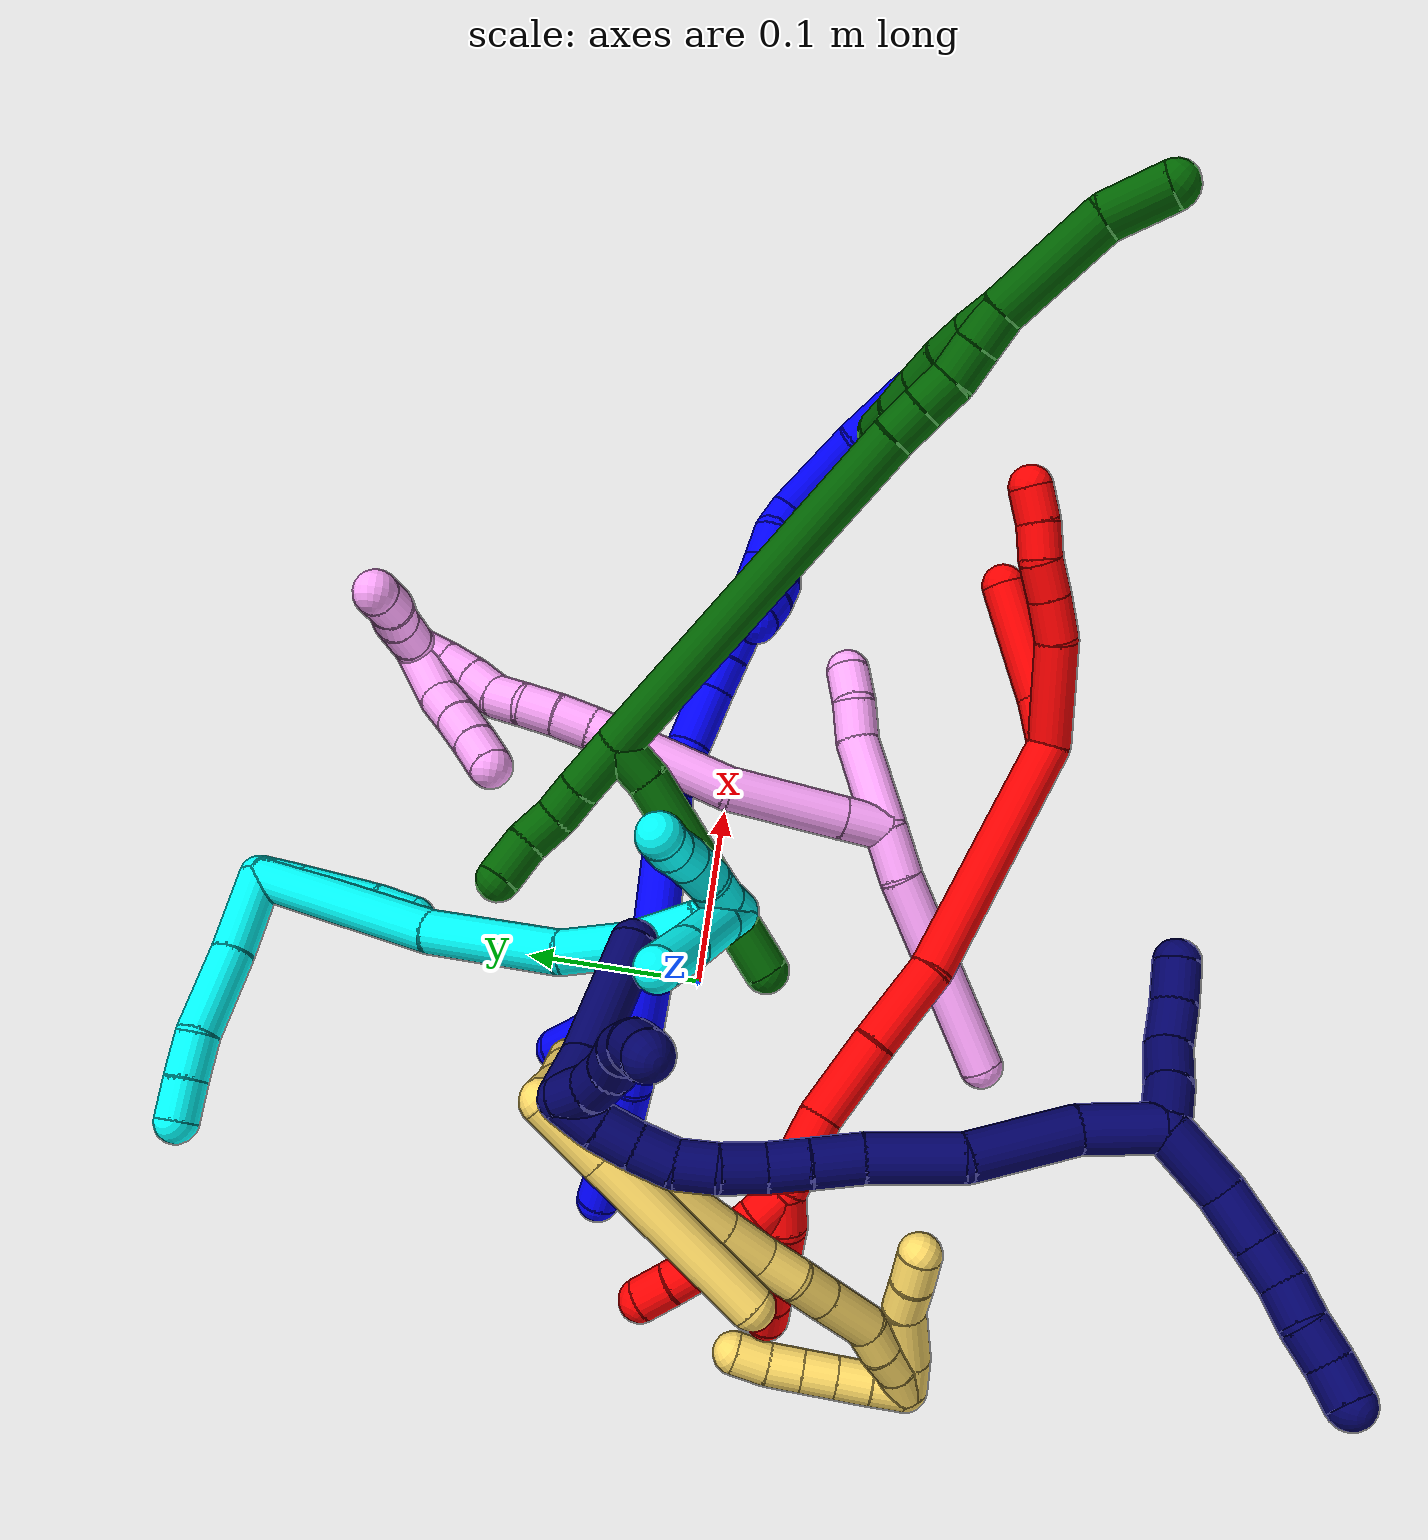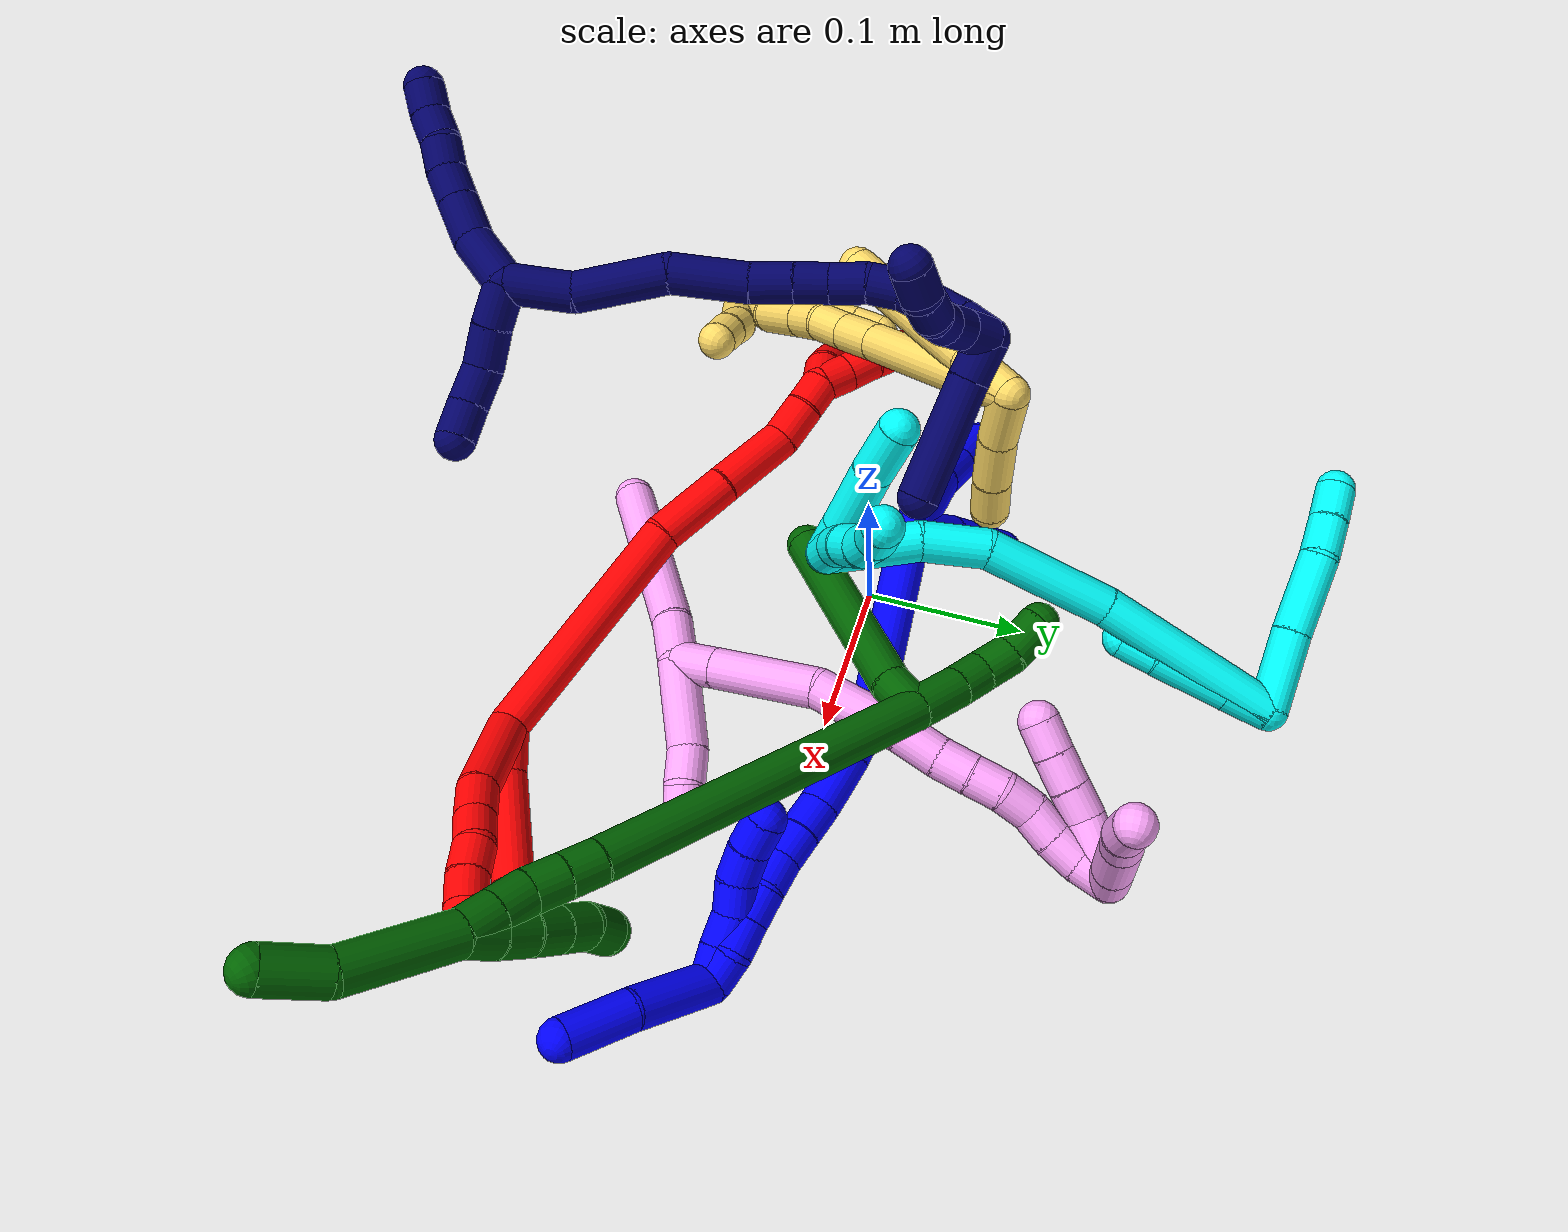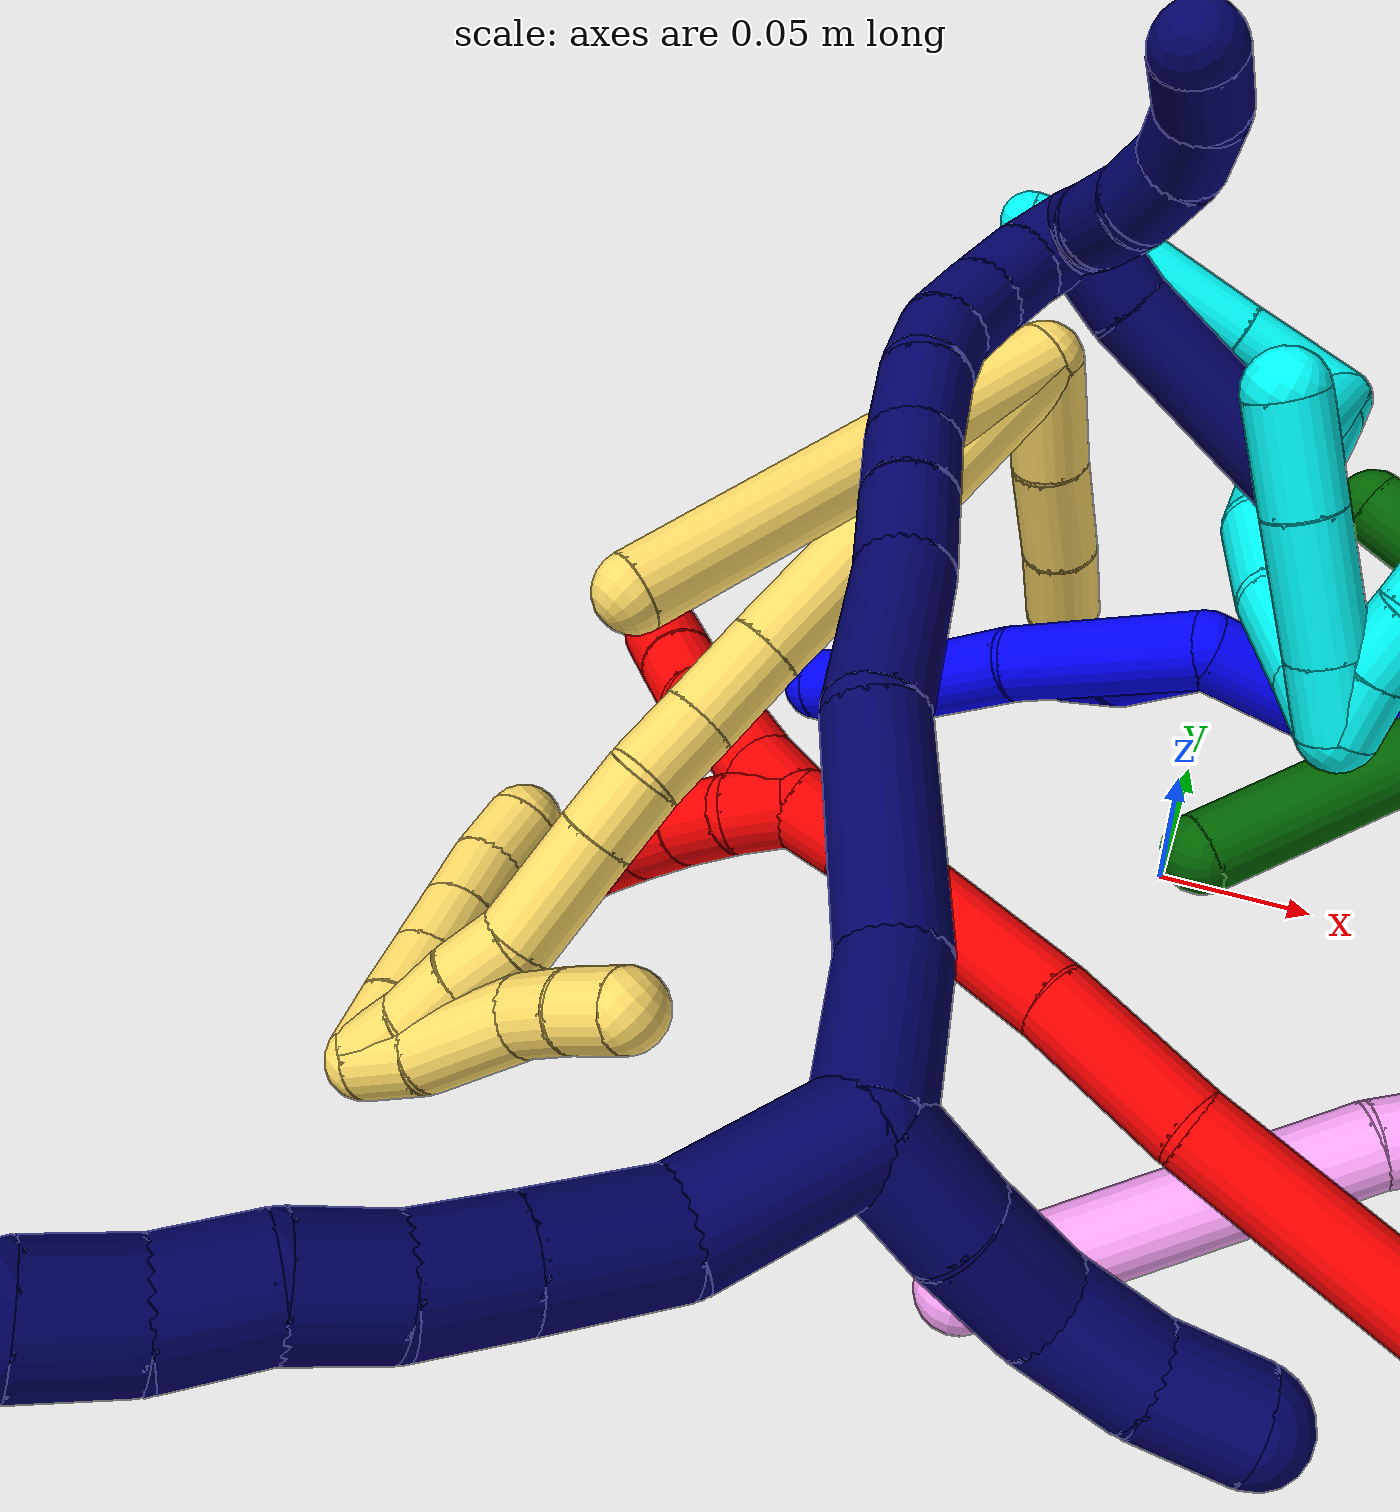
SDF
<sdf version="1.7">
 <world name="default">
  <plugin name="TubeGeneratorPlugin" filename="libtube_generator_plugin.so"/>
  <model name="photoneo_s_sensor">
   <static>1</static>
   <pose>0 0 2 1.57079 1.57079 3.14159</pose>
   <link name="link">
    <inertial><mass>0.1</mass></inertial>
    <sensor name="sensor" type="depth">
     <update_rate>30</update_rate>
     <camera>
      <horizontal_fov>1.22</horizontal_fov>
      <image><width>1920</width><height>1200</height><format>B8G8R8</format></image>
      <clip><near>0.1</near><far>4</far></clip>
      <depth_camera><output>points</output></depth_camera>
     </camera>
     <plugin name="camera_plugin" filename="libgazebo_ros_depth_camera.so">
      <baseline>0.2</baseline>
      <alwaysOn>1</alwaysOn>
      <updateRate>0.0</updateRate>
      <cameraName>camera_ir</cameraName>
      <imageTopicName>/camera/color/image_raw</imageTopicName>
      <cameraInfoTopicName>/camera/color/camera_info</cameraInfoTopicName>
      <depthImageTopicName>/camera/depth/image_raw</depthImageTopicName>
      <depthImageCameraInfoTopicName>/camera/depth/camera_info</depthImageCameraInfoTopicName>
      <pointCloudTopicName>/camera/depth/points</pointCloudTopicName>
      <frameName>fr_optical</frameName>
      <pointCloudCutoff>0.1</pointCloudCutoff>
      <pointCloudCutoffMax>2.0</pointCloudCutoffMax>
      <distortionK1>0</distortionK1>
      <distortionK2>0</distortionK2>
      <distortionK3>0</distortionK3>
      <distortionT1>0</distortionT1>
      <distortionT2>0</distortionT2>
      <CxPrime>0</CxPrime>
      <Cx>0</Cx>
      <Cy>0</Cy>
      <focalLength>0</focalLength>
      <hackBaseline>0</hackBaseline>
     </plugin>
    </sensor>
   </link>
  </model>
  <gravity>0 0 -9.8</gravity>
  <magnetic_field>6e-06 2.3e-05 -4.2e-05</magnetic_field>
  <atmosphere type="adiabatic"/>
  <physics name="default_physics" default="0" type="ode">
   <max_step_size>0.003</max_step_size>
   <real_time_factor>1</real_time_factor>
   <real_time_update_rate>1000</real_time_update_rate>
   <max_contacts>10000</max_contacts>
   <ode>
    <solver>
     <type>quick</type>
     <iters>100</iters>
     <sor>1.3</sor>
     <use_dynamic_moi_rescaling>0</use_dynamic_moi_rescaling>
    </solver>
    <constraints>
     <contact_max_correcting_vel>0</contact_max_correcting_vel>
     <contact_surface_layer>0.001</contact_surface_layer>
     <cfm>0</cfm>
     <erp>0.2</erp>
    </constraints>
   </ode>
  </physics>
  <scene><ambient>0.4 0.4 0.4 1</ambient><background>0.7 0.7 0.7 1</background><shadows>0</shadows></scene>
  <audio><device>default</device></audio>
  <spherical_coordinates>
   <surface_model>EARTH_WGS84</surface_model>
   <latitude_deg>0</latitude_deg>
   <longitude_deg>0</longitude_deg>
   <elevation>0</elevation>
   <heading_deg>0</heading_deg>
  </spherical_coordinates>
  <model name="bin">
   <static>1</static>
   <link name="bottom">
    <collision name="collision-bottom">
     <pose>0 0 -0.01 0 -0 0</pose>
     <geometry><box><size>0.8 0.6 0.02</size></box></geometry>
     <surface>
      <friction><ode><mu>100</mu><mu2>100</mu2></ode></friction>
      <contact><collide_bitmask>65535</collide_bitmask></contact>
     </surface>
    </collision>
   </link>
   <link name="west_wall">
    <collision name="collision-west_wall">
     <pose>-0.41 0 0.1 0 -0 0</pose>
     <geometry><box><size>0.02 0.6 0.2</size></box></geometry>
     <surface>
      <friction><ode><mu>100</mu><mu2>100</mu2></ode></friction>
      <contact><collide_bitmask>65535</collide_bitmask></contact>
     </surface>
    </collision>
   </link>
   <link name="east_wall">
    <collision name="collision-east_wall">
     <pose>0.41 0 0.1 0 -0 0</pose>
     <geometry><box><size>0.02 0.6 0.2</size></box></geometry>
     <surface>
      <friction><ode><mu>100</mu><mu2>100</mu2></ode></friction>
      <contact><collide_bitmask>65535</collide_bitmask></contact>
     </surface>
    </collision>
   </link>
   <link name="south_wall">
    <collision name="collision-south_wall">
     <pose>0 -0.31 0.1 0 -0 0</pose>
     <geometry><box><size>0.8 0.02 0.2</size></box></geometry>
     <surface>
      <friction><ode><mu>100</mu><mu2>100</mu2></ode></friction>
      <contact><collide_bitmask>65535</collide_bitmask></contact>
     </surface>
    </collision>
   </link>
   <link name="north_wall">
    <collision name="collision-north_wall">
     <pose>0 0.31 0.1 0 -0 0</pose>
     <geometry><box><size>0.8 0.02 0.2</size></box></geometry>
     <surface>
      <friction><ode><mu>100</mu><mu2>100</mu2></ode></friction>
      <contact><collide_bitmask>65535</collide_bitmask></contact>
     </surface>
    </collision>
   </link>
  </model>
  <model name="1">
   <static>0</static>
   <link name="1">
    <collision name="collision-cylinder-e_1_2_8">
     <pose>8.9e-05 3.9e-05 -0.033346 -3.14043 0.002684 -2.3262</pose>
     <geometry><cylinder><radius>0.0125</radius><length>0.066691</length></cylinder></geometry>
     <surface>
      <friction><ode><mu>1.16</mu><mu2>1.16</mu2><slip1>0</slip1><slip2>0</slip2></ode></friction>
      <contact><ode><kp>1e+06</kp><kd>1</kd><max_vel>0</max_vel><min_depth>0.001</min_depth></ode></contact>
     </surface>
    </collision>
    <visual name="visual-cylinder-e_1_2_8">
     <pose>8.9e-05 3.9e-05 -0.033346 -3.14043 0.002684 -2.3262</pose>
     <geometry><cylinder><radius>0.0125</radius><length>0.066691</length></cylinder></geometry>
     <material><ambient>0 0 1 1</ambient></material>
    </visual>
    <collision name="collision-cylinder-e_2_8_9">
     <pose>0.004004 0.001491 -0.086918 -3.07183 0.186483 -2.42725</pose>
     <geometry><cylinder><radius>0.0125</radius><length>0.041267</length></cylinder></geometry>
     <surface>
      <friction><ode><mu>1.16</mu><mu2>1.16</mu2><slip1>0</slip1><slip2>0</slip2></ode></friction>
      <contact><ode><kp>1e+06</kp><kd>1</kd><max_vel>0</max_vel><min_depth>0.001</min_depth></ode></contact>
     </surface>
    </collision>
    <visual name="visual-cylinder-e_2_8_9">
     <pose>0.004004 0.001491 -0.086918 -3.07183 0.186483 -2.42725</pose>
     <geometry><cylinder><radius>0.0125</radius><length>0.041267</length></cylinder></geometry>
     <material><ambient>0 0 1 1</ambient></material>
    </visual>
    <collision name="collision-cylinder-e_3_9_6">
     <pose>0.008596 0.005426 -0.127999 -3.02124 0.036429 -0.587234</pose>
     <geometry><cylinder><radius>0.0125</radius><length>0.042042</length></cylinder></geometry>
     <surface>
      <friction><ode><mu>1.16</mu><mu2>1.16</mu2><slip1>0</slip1><slip2>0</slip2></ode></friction>
      <contact><ode><kp>1e+06</kp><kd>1</kd><max_vel>0</max_vel><min_depth>0.001</min_depth></ode></contact>
     </surface>
    </collision>
    <visual name="visual-cylinder-e_3_9_6">
     <pose>0.008596 0.005426 -0.127999 -3.02124 0.036429 -0.587234</pose>
     <geometry><cylinder><radius>0.0125</radius><length>0.042042</length></cylinder></geometry>
     <material><ambient>0 0 1 1</ambient></material>
    </visual>
    <collision name="collision-cylinder-e_1_2_10">
     <pose>0.010007 0.009228 -0.020409 -2.71695 0.420166 -1.55989</pose>
     <geometry><cylinder><radius>0.0125</radius><length>0.049063</length></cylinder></geometry>
     <surface>
      <friction><ode><mu>1.16</mu><mu2>1.16</mu2><slip1>0</slip1><slip2>0</slip2></ode></friction>
      <contact><ode><kp>1e+06</kp><kd>1</kd><max_vel>0</max_vel><min_depth>0.001</min_depth></ode></contact>
     </surface>
    </collision>
    <visual name="visual-cylinder-e_1_2_10">
     <pose>0.010007 0.009228 -0.020409 -2.71695 0.420166 -1.55989</pose>
     <geometry><cylinder><radius>0.0125</radius><length>0.049063</length></cylinder></geometry>
     <material><ambient>0 0 1 1</ambient></material>
    </visual>
    <collision name="collision-cylinder-e_2_10_5">
     <pose>0.030546 0.033629 -0.058352 -2.42825 0.426369 -1.05261</pose>
     <geometry><cylinder><radius>0.0125</radius><length>0.050937</length></cylinder></geometry>
     <surface>
      <friction><ode><mu>1.16</mu><mu2>1.16</mu2><slip1>0</slip1><slip2>0</slip2></ode></friction>
      <contact><ode><kp>1e+06</kp><kd>1</kd><max_vel>0</max_vel><min_depth>0.001</min_depth></ode></contact>
     </surface>
    </collision>
    <visual name="visual-cylinder-e_2_10_5">
     <pose>0.030546 0.033629 -0.058352 -2.42825 0.426369 -1.05261</pose>
     <geometry><cylinder><radius>0.0125</radius><length>0.050937</length></cylinder></geometry>
     <material><ambient>0 0 1 1</ambient></material>
    </visual>
    <collision name="collision-cylinder-e_1_2_11">
     <pose>0.040879 0.006423 0.0403 -0.158049 0.786254 -0.065658</pose>
     <geometry><cylinder><radius>0.0125</radius><length>0.115525</length></cylinder></geometry>
     <surface>
      <friction><ode><mu>1.16</mu><mu2>1.16</mu2><slip1>0</slip1><slip2>0</slip2></ode></friction>
      <contact><ode><kp>1e+06</kp><kd>1</kd><max_vel>0</max_vel><min_depth>0.001</min_depth></ode></contact>
     </surface>
    </collision>
    <visual name="visual-cylinder-e_1_2_11">
     <pose>0.040879 0.006423 0.0403 -0.158049 0.786254 -0.065658</pose>
     <geometry><cylinder><radius>0.0125</radius><length>0.115525</length></cylinder></geometry>
     <material><ambient>0 0 1 1</ambient></material>
    </visual>
    <collision name="collision-cylinder-e_2_11_12">
     <pose>0.09082 0.010991 0.090995 0.17658 0.709281 0.065534</pose>
     <geometry><cylinder><radius>0.0125</radius><length>0.027828</length></cylinder></geometry>
     <surface>
      <friction><ode><mu>1.16</mu><mu2>1.16</mu2><slip1>0</slip1><slip2>0</slip2></ode></friction>
      <contact><ode><kp>1e+06</kp><kd>1</kd><max_vel>0</max_vel><min_depth>0.001</min_depth></ode></contact>
     </surface>
    </collision>
    <visual name="visual-cylinder-e_2_11_12">
     <pose>0.09082 0.010991 0.090995 0.17658 0.709281 0.065534</pose>
     <geometry><cylinder><radius>0.0125</radius><length>0.027828</length></cylinder></geometry>
     <material><ambient>0 0 1 1</ambient></material>
    </visual>
    <collision name="collision-cylinder-e_3_12_13">
     <pose>0.109098 0.005912 0.11619 0.214509 0.546551 0.060338</pose>
     <geometry><cylinder><radius>0.0125</radius><length>0.035463</length></cylinder></geometry>
     <surface>
      <friction><ode><mu>1.16</mu><mu2>1.16</mu2><slip1>0</slip1><slip2>0</slip2></ode></friction>
      <contact><ode><kp>1e+06</kp><kd>1</kd><max_vel>0</max_vel><min_depth>0.001</min_depth></ode></contact>
     </surface>
    </collision>
    <visual name="visual-cylinder-e_3_12_13">
     <pose>0.109098 0.005912 0.11619 0.214509 0.546551 0.060338</pose>
     <geometry><cylinder><radius>0.0125</radius><length>0.035463</length></cylinder></geometry>
     <material><ambient>0 0 1 1</ambient></material>
    </visual>
    <collision name="collision-cylinder-e_4_13_14">
     <pose>0.122209 0.000415 0.140127 0.243823 0.392357 0.048688</pose>
     <geometry><cylinder><radius>0.0125</radius><length>0.020376</length></cylinder></geometry>
     <surface>
      <friction><ode><mu>1.16</mu><mu2>1.16</mu2><slip1>0</slip1><slip2>0</slip2></ode></friction>
      <contact><ode><kp>1e+06</kp><kd>1</kd><max_vel>0</max_vel><min_depth>0.001</min_depth></ode></contact>
     </surface>
    </collision>
    <visual name="visual-cylinder-e_4_13_14">
     <pose>0.122209 0.000415 0.140127 0.243823 0.392357 0.048688</pose>
     <geometry><cylinder><radius>0.0125</radius><length>0.020376</length></cylinder></geometry>
     <material><ambient>0 0 1 1</ambient></material>
    </visual>
    <collision name="collision-cylinder-e_5_14_15">
     <pose>0.13048 -0.004158 0.158059 0.255712 0.448495 0.058627</pose>
     <geometry><cylinder><radius>0.0125</radius><length>0.020181</length></cylinder></geometry>
     <surface>
      <friction><ode><mu>1.16</mu><mu2>1.16</mu2><slip1>0</slip1><slip2>0</slip2></ode></friction>
      <contact><ode><kp>1e+06</kp><kd>1</kd><max_vel>0</max_vel><min_depth>0.001</min_depth></ode></contact>
     </surface>
    </collision>
    <visual name="visual-cylinder-e_5_14_15">
     <pose>0.13048 -0.004158 0.158059 0.255712 0.448495 0.058627</pose>
     <geometry><cylinder><radius>0.0125</radius><length>0.020181</length></cylinder></geometry>
     <material><ambient>0 0 1 1</ambient></material>
    </visual>
    <collision name="collision-cylinder-e_6_15_16">
     <pose>0.138718 -0.007617 0.176332 0.121798 0.384452 0.023734</pose>
     <geometry><cylinder><radius>0.0125</radius><length>0.020596</length></cylinder></geometry>
     <surface>
      <friction><ode><mu>1.16</mu><mu2>1.16</mu2><slip1>0</slip1><slip2>0</slip2></ode></friction>
      <contact><ode><kp>1e+06</kp><kd>1</kd><max_vel>0</max_vel><min_depth>0.001</min_depth></ode></contact>
     </surface>
    </collision>
    <visual name="visual-cylinder-e_6_15_16">
     <pose>0.138718 -0.007617 0.176332 0.121798 0.384452 0.023734</pose>
     <geometry><cylinder><radius>0.0125</radius><length>0.020596</length></cylinder></geometry>
     <material><ambient>0 0 1 1</ambient></material>
    </visual>
    <collision name="collision-cylinder-e_7_16_17">
     <pose>0.148411 -0.010106 0.193835 0.164017 0.621834 0.052811</pose>
     <geometry><cylinder><radius>0.0125</radius><length>0.020019</length></cylinder></geometry>
     <surface>
      <friction><ode><mu>1.16</mu><mu2>1.16</mu2><slip1>0</slip1><slip2>0</slip2></ode></friction>
      <contact><ode><kp>1e+06</kp><kd>1</kd><max_vel>0</max_vel><min_depth>0.001</min_depth></ode></contact>
     </surface>
    </collision>
    <visual name="visual-cylinder-e_7_16_17">
     <pose>0.148411 -0.010106 0.193835 0.164017 0.621834 0.052811</pose>
     <geometry><cylinder><radius>0.0125</radius><length>0.020019</length></cylinder></geometry>
     <material><ambient>0 0 1 1</ambient></material>
    </visual>
    <collision name="collision-cylinder-e_8_17_18">
     <pose>0.160276 -0.01253 0.209764 0.137802 0.647486 0.046304</pose>
     <geometry><cylinder><radius>0.0125</radius><length>0.020007</length></cylinder></geometry>
     <surface>
      <friction><ode><mu>1.16</mu><mu2>1.16</mu2><slip1>0</slip1><slip2>0</slip2></ode></friction>
      <contact><ode><kp>1e+06</kp><kd>1</kd><max_vel>0</max_vel><min_depth>0.001</min_depth></ode></contact>
     </surface>
    </collision>
    <visual name="visual-cylinder-e_8_17_18">
     <pose>0.160276 -0.01253 0.209764 0.137802 0.647486 0.046304</pose>
     <geometry><cylinder><radius>0.0125</radius><length>0.020007</length></cylinder></geometry>
     <material><ambient>0 0 1 1</ambient></material>
    </visual>
    <collision name="collision-cylinder-e_9_18_1">
     <pose>0.174072 -0.016551 0.223258 0.48197 0.888262 0.232827</pose>
     <geometry><cylinder><radius>0.0125</radius><length>0.020005</length></cylinder></geometry>
     <surface>
      <friction><ode><mu>1.16</mu><mu2>1.16</mu2><slip1>0</slip1><slip2>0</slip2></ode></friction>
      <contact><ode><kp>1e+06</kp><kd>1</kd><max_vel>0</max_vel><min_depth>0.001</min_depth></ode></contact>
     </surface>
    </collision>
    <visual name="visual-cylinder-e_9_18_1">
     <pose>0.174072 -0.016551 0.223258 0.48197 0.888262 0.232827</pose>
     <geometry><cylinder><radius>0.0125</radius><length>0.020005</length></cylinder></geometry>
     <material><ambient>0 0 1 1</ambient></material>
    </visual>
    <collision name="collision-cylinder-e_1_1_19">
     <pose>0.174407 -0.019928 0.222167 3.07395 -0.837042 -2.98976</pose>
     <geometry><cylinder><radius>0.0125</radius><length>0.02</length></cylinder></geometry>
     <surface>
      <friction><ode><mu>1.16</mu><mu2>1.16</mu2><slip1>0</slip1><slip2>0</slip2></ode></friction>
      <contact><ode><kp>1e+06</kp><kd>1</kd><max_vel>0</max_vel><min_depth>0.001</min_depth></ode></contact>
     </surface>
    </collision>
    <visual name="visual-cylinder-e_1_1_19">
     <pose>0.174407 -0.019928 0.222167 3.07395 -0.837042 -2.98976</pose>
     <geometry><cylinder><radius>0.0125</radius><length>0.02</length></cylinder></geometry>
     <material><ambient>0 0 1 1</ambient></material>
    </visual>
    <collision name="collision-cylinder-e_2_19_20">
     <pose>0.159161 -0.019864 0.209273 -3.05859 -0.89773 2.96959</pose>
     <geometry><cylinder><radius>0.0125</radius><length>0.02</length></cylinder></geometry>
     <surface>
      <friction><ode><mu>1.16</mu><mu2>1.16</mu2><slip1>0</slip1><slip2>0</slip2></ode></friction>
      <contact><ode><kp>1e+06</kp><kd>1</kd><max_vel>0</max_vel><min_depth>0.001</min_depth></ode></contact>
     </surface>
    </collision>
    <visual name="visual-cylinder-e_2_19_20">
     <pose>0.159161 -0.019864 0.209273 -3.05859 -0.89773 2.96959</pose>
     <geometry><cylinder><radius>0.0125</radius><length>0.02</length></cylinder></geometry>
     <material><ambient>0 0 1 1</ambient></material>
    </visual>
    <collision name="collision-cylinder-e_3_20_21">
     <pose>0.142385 -0.021142 0.198991 2.7261 -1.10984 -2.48605</pose>
     <geometry><cylinder><radius>0.0125</radius><length>0.02</length></cylinder></geometry>
     <surface>
      <friction><ode><mu>1.16</mu><mu2>1.16</mu2><slip1>0</slip1><slip2>0</slip2></ode></friction>
      <contact><ode><kp>1e+06</kp><kd>1</kd><max_vel>0</max_vel><min_depth>0.001</min_depth></ode></contact>
     </surface>
    </collision>
    <visual name="visual-cylinder-e_3_20_21">
     <pose>0.142385 -0.021142 0.198991 2.7261 -1.10984 -2.48605</pose>
     <geometry><cylinder><radius>0.0125</radius><length>0.02</length></cylinder></geometry>
     <material><ambient>0 0 1 1</ambient></material>
    </visual>
    <collision name="collision-cylinder-e_4_21_22">
     <pose>0.124104 -0.021984 0.191439 -2.87428 -1.20131 2.75399</pose>
     <geometry><cylinder><radius>0.0125</radius><length>0.02</length></cylinder></geometry>
     <surface>
      <friction><ode><mu>1.16</mu><mu2>1.16</mu2><slip1>0</slip1><slip2>0</slip2></ode></friction>
      <contact><ode><kp>1e+06</kp><kd>1</kd><max_vel>0</max_vel><min_depth>0.001</min_depth></ode></contact>
     </surface>
    </collision>
    <visual name="visual-cylinder-e_4_21_22">
     <pose>0.124104 -0.021984 0.191439 -2.87428 -1.20131 2.75399</pose>
     <geometry><cylinder><radius>0.0125</radius><length>0.02</length></cylinder></geometry>
     <material><ambient>0 0 1 1</ambient></material>
    </visual>
    <collision name="collision-cylinder-e_5_22_4">
     <pose>0.105616 -0.018688 0.184706 -2.51729 -1.15868 2.22511</pose>
     <geometry><cylinder><radius>0.0125</radius><length>0.02</length></cylinder></geometry>
     <surface>
      <friction><ode><mu>1.16</mu><mu2>1.16</mu2><slip1>0</slip1><slip2>0</slip2></ode></friction>
      <contact><ode><kp>1e+06</kp><kd>1</kd><max_vel>0</max_vel><min_depth>0.001</min_depth></ode></contact>
     </surface>
    </collision>
    <visual name="visual-cylinder-e_5_22_4">
     <pose>0.105616 -0.018688 0.184706 -2.51729 -1.15868 2.22511</pose>
     <geometry><cylinder><radius>0.0125</radius><length>0.02</length></cylinder></geometry>
     <material><ambient>0 0 1 1</ambient></material>
    </visual>
    <collision name="collision-cylinder-e_1_1_23">
     <pose>0.177042 -0.034514 0.25258 0.564836 -0.168905 -0.049119</pose>
     <geometry><cylinder><radius>0.0125</radius><length>0.057001</length></cylinder></geometry>
     <surface>
      <friction><ode><mu>1.16</mu><mu2>1.16</mu2><slip1>0</slip1><slip2>0</slip2></ode></friction>
      <contact><ode><kp>1e+06</kp><kd>1</kd><max_vel>0</max_vel><min_depth>0.001</min_depth></ode></contact>
     </surface>
    </collision>
    <visual name="visual-cylinder-e_1_1_23">
     <pose>0.177042 -0.034514 0.25258 0.564836 -0.168905 -0.049119</pose>
     <geometry><cylinder><radius>0.0125</radius><length>0.057001</length></cylinder></geometry>
     <material><ambient>0 0 1 1</ambient></material>
    </visual>
    <collision name="collision-cylinder-e_2_23_3">
     <pose>0.17259 -0.062398 0.293548 0.640445 0.015761 0.005227</pose>
     <geometry><cylinder><radius>0.0125</radius><length>0.042999</length></cylinder></geometry>
     <surface>
      <friction><ode><mu>1.16</mu><mu2>1.16</mu2><slip1>0</slip1><slip2>0</slip2></ode></friction>
      <contact><ode><kp>1e+06</kp><kd>1</kd><max_vel>0</max_vel><min_depth>0.001</min_depth></ode></contact>
     </surface>
    </collision>
    <visual name="visual-cylinder-e_2_23_3">
     <pose>0.17259 -0.062398 0.293548 0.640445 0.015761 0.005227</pose>
     <geometry><cylinder><radius>0.0125</radius><length>0.042999</length></cylinder></geometry>
     <material><ambient>0 0 1 1</ambient></material>
    </visual>
    <collision name="collision-sphere-3">
     <pose>0.172929 -0.075243 0.310784 0 -0 0</pose>
     <geometry><sphere><radius>0.0125</radius></sphere></geometry>
     <surface>
      <friction><ode><mu>1.16</mu><mu2>1.16</mu2><slip1>0</slip1><slip2>0</slip2></ode></friction>
      <contact><ode><kp>1e+06</kp><kd>1</kd><max_vel>0</max_vel><min_depth>0.001</min_depth></ode></contact>
     </surface>
    </collision>
    <visual name="visual-sphere-3">
     <pose>0.172929 -0.075243 0.310784 0 -0 0</pose>
     <geometry><sphere><radius>0.0125</radius></sphere></geometry>
     <material><ambient>0 0 1 1</ambient></material>
    </visual>
    <collision name="collision-sphere-23">
     <pose>0.172251 -0.049552 0.276311 0 -0 0</pose>
     <geometry><sphere><radius>0.0125</radius></sphere></geometry>
     <surface>
      <friction><ode><mu>1.16</mu><mu2>1.16</mu2><slip1>0</slip1><slip2>0</slip2></ode></friction>
      <contact><ode><kp>1e+06</kp><kd>1</kd><max_vel>0</max_vel><min_depth>0.001</min_depth></ode></contact>
     </surface>
    </collision>
    <visual name="visual-sphere-23">
     <pose>0.172251 -0.049552 0.276311 0 -0 0</pose>
     <geometry><sphere><radius>0.0125</radius></sphere></geometry>
     <material><ambient>0 0 1 1</ambient></material>
    </visual>
    <collision name="collision-sphere-4">
     <pose>0.096453 -0.016347 0.181456 0 -0 0</pose>
     <geometry><sphere><radius>0.0125</radius></sphere></geometry>
     <surface>
      <friction><ode><mu>1.16</mu><mu2>1.16</mu2><slip1>0</slip1><slip2>0</slip2></ode></friction>
      <contact><ode><kp>1e+06</kp><kd>1</kd><max_vel>0</max_vel><min_depth>0.001</min_depth></ode></contact>
     </surface>
    </collision>
    <visual name="visual-sphere-4">
     <pose>0.096453 -0.016347 0.181456 0 -0 0</pose>
     <geometry><sphere><radius>0.0125</radius></sphere></geometry>
     <material><ambient>0 0 1 1</ambient></material>
    </visual>
    <collision name="collision-sphere-22">
     <pose>0.114779 -0.02103 0.187956 0 -0 0</pose>
     <geometry><sphere><radius>0.0125</radius></sphere></geometry>
     <surface>
      <friction><ode><mu>1.16</mu><mu2>1.16</mu2><slip1>0</slip1><slip2>0</slip2></ode></friction>
      <contact><ode><kp>1e+06</kp><kd>1</kd><max_vel>0</max_vel><min_depth>0.001</min_depth></ode></contact>
     </surface>
    </collision>
    <visual name="visual-sphere-22">
     <pose>0.114779 -0.02103 0.187956 0 -0 0</pose>
     <geometry><sphere><radius>0.0125</radius></sphere></geometry>
     <material><ambient>0 0 1 1</ambient></material>
    </visual>
    <collision name="collision-sphere-21">
     <pose>0.133429 -0.022938 0.194922 0 -0 0</pose>
     <geometry><sphere><radius>0.0125</radius></sphere></geometry>
     <surface>
      <friction><ode><mu>1.16</mu><mu2>1.16</mu2><slip1>0</slip1><slip2>0</slip2></ode></friction>
      <contact><ode><kp>1e+06</kp><kd>1</kd><max_vel>0</max_vel><min_depth>0.001</min_depth></ode></contact>
     </surface>
    </collision>
    <visual name="visual-sphere-21">
     <pose>0.133429 -0.022938 0.194922 0 -0 0</pose>
     <geometry><sphere><radius>0.0125</radius></sphere></geometry>
     <material><ambient>0 0 1 1</ambient></material>
    </visual>
    <collision name="collision-sphere-20">
     <pose>0.151342 -0.019347 0.203061 0 -0 0</pose>
     <geometry><sphere><radius>0.0125</radius></sphere></geometry>
     <surface>
      <friction><ode><mu>1.16</mu><mu2>1.16</mu2><slip1>0</slip1><slip2>0</slip2></ode></friction>
      <contact><ode><kp>1e+06</kp><kd>1</kd><max_vel>0</max_vel><min_depth>0.001</min_depth></ode></contact>
     </surface>
    </collision>
    <visual name="visual-sphere-20">
     <pose>0.151342 -0.019347 0.203061 0 -0 0</pose>
     <geometry><sphere><radius>0.0125</radius></sphere></geometry>
     <material><ambient>0 0 1 1</ambient></material>
    </visual>
    <collision name="collision-sphere-5">
     <pose>0.041079 0.048803 -0.075886 0 -0 0</pose>
     <geometry><sphere><radius>0.0125</radius></sphere></geometry>
     <surface>
      <friction><ode><mu>1.16</mu><mu2>1.16</mu2><slip1>0</slip1><slip2>0</slip2></ode></friction>
      <contact><ode><kp>1e+06</kp><kd>1</kd><max_vel>0</max_vel><min_depth>0.001</min_depth></ode></contact>
     </surface>
    </collision>
    <visual name="visual-sphere-5">
     <pose>0.041079 0.048803 -0.075886 0 -0 0</pose>
     <geometry><sphere><radius>0.0125</radius></sphere></geometry>
     <material><ambient>0 0 1 1</ambient></material>
    </visual>
    <collision name="collision-sphere-10">
     <pose>0.020013 0.018455 -0.040817 0 -0 0</pose>
     <geometry><sphere><radius>0.0125</radius></sphere></geometry>
     <surface>
      <friction><ode><mu>1.16</mu><mu2>1.16</mu2><slip1>0</slip1><slip2>0</slip2></ode></friction>
      <contact><ode><kp>1e+06</kp><kd>1</kd><max_vel>0</max_vel><min_depth>0.001</min_depth></ode></contact>
     </surface>
    </collision>
    <visual name="visual-sphere-10">
     <pose>0.020013 0.018455 -0.040817 0 -0 0</pose>
     <geometry><sphere><radius>0.0125</radius></sphere></geometry>
     <material><ambient>0 0 1 1</ambient></material>
    </visual>
    <collision name="collision-sphere-6">
     <pose>0.009361 0.007948 -0.148854 0 -0 0</pose>
     <geometry><sphere><radius>0.0125</radius></sphere></geometry>
     <surface>
      <friction><ode><mu>1.16</mu><mu2>1.16</mu2><slip1>0</slip1><slip2>0</slip2></ode></friction>
      <contact><ode><kp>1e+06</kp><kd>1</kd><max_vel>0</max_vel><min_depth>0.001</min_depth></ode></contact>
     </surface>
    </collision>
    <visual name="visual-sphere-6">
     <pose>0.009361 0.007948 -0.148854 0 -0 0</pose>
     <geometry><sphere><radius>0.0125</radius></sphere></geometry>
     <material><ambient>0 0 1 1</ambient></material>
    </visual>
    <collision name="collision-sphere-9">
     <pose>0.00783 0.002904 -0.107144 0 -0 0</pose>
     <geometry><sphere><radius>0.0125</radius></sphere></geometry>
     <surface>
      <friction><ode><mu>1.16</mu><mu2>1.16</mu2><slip1>0</slip1><slip2>0</slip2></ode></friction>
      <contact><ode><kp>1e+06</kp><kd>1</kd><max_vel>0</max_vel><min_depth>0.001</min_depth></ode></contact>
     </surface>
    </collision>
    <visual name="visual-sphere-9">
     <pose>0.00783 0.002904 -0.107144 0 -0 0</pose>
     <geometry><sphere><radius>0.0125</radius></sphere></geometry>
     <material><ambient>0 0 1 1</ambient></material>
    </visual>
    <collision name="collision-sphere-2">
     <geometry><sphere><radius>0.0125</radius></sphere></geometry>
     <surface>
      <friction><ode><mu>1.16</mu><mu2>1.16</mu2><slip1>0</slip1><slip2>0</slip2></ode></friction>
      <contact><ode><kp>1e+06</kp><kd>1</kd><max_vel>0</max_vel><min_depth>0.001</min_depth></ode></contact>
     </surface>
    </collision>
    <visual name="visual-sphere-2">
     <geometry><sphere><radius>0.0125</radius></sphere></geometry>
     <material><ambient>0 0 1 1</ambient></material>
    </visual>
    <collision name="collision-sphere-19">
     <pose>0.16698 -0.02038 0.215486 0 -0 0</pose>
     <geometry><sphere><radius>0.0125</radius></sphere></geometry>
     <surface>
      <friction><ode><mu>1.16</mu><mu2>1.16</mu2><slip1>0</slip1><slip2>0</slip2></ode></friction>
      <contact><ode><kp>1e+06</kp><kd>1</kd><max_vel>0</max_vel><min_depth>0.001</min_depth></ode></contact>
     </surface>
    </collision>
    <visual name="visual-sphere-19">
     <pose>0.16698 -0.02038 0.215486 0 -0 0</pose>
     <geometry><sphere><radius>0.0125</radius></sphere></geometry>
     <material><ambient>0 0 1 1</ambient></material>
    </visual>
    <collision name="collision-sphere-8">
     <pose>0.000179 7.7e-05 -0.066691 0 -0 0</pose>
     <geometry><sphere><radius>0.0125</radius></sphere></geometry>
     <surface>
      <friction><ode><mu>1.16</mu><mu2>1.16</mu2><slip1>0</slip1><slip2>0</slip2></ode></friction>
      <contact><ode><kp>1e+06</kp><kd>1</kd><max_vel>0</max_vel><min_depth>0.001</min_depth></ode></contact>
     </surface>
    </collision>
    <visual name="visual-sphere-8">
     <pose>0.000179 7.7e-05 -0.066691 0 -0 0</pose>
     <geometry><sphere><radius>0.0125</radius></sphere></geometry>
     <material><ambient>0 0 1 1</ambient></material>
    </visual>
    <collision name="collision-sphere-11">
     <pose>0.081758 0.012846 0.080601 0 -0 0</pose>
     <geometry><sphere><radius>0.0125</radius></sphere></geometry>
     <surface>
      <friction><ode><mu>1.16</mu><mu2>1.16</mu2><slip1>0</slip1><slip2>0</slip2></ode></friction>
      <contact><ode><kp>1e+06</kp><kd>1</kd><max_vel>0</max_vel><min_depth>0.001</min_depth></ode></contact>
     </surface>
    </collision>
    <visual name="visual-sphere-11">
     <pose>0.081758 0.012846 0.080601 0 -0 0</pose>
     <geometry><sphere><radius>0.0125</radius></sphere></geometry>
     <material><ambient>0 0 1 1</ambient></material>
    </visual>
    <collision name="collision-sphere-12">
     <pose>0.099882 0.009137 0.101389 0 -0 0</pose>
     <geometry><sphere><radius>0.0125</radius></sphere></geometry>
     <surface>
      <friction><ode><mu>1.16</mu><mu2>1.16</mu2><slip1>0</slip1><slip2>0</slip2></ode></friction>
      <contact><ode><kp>1e+06</kp><kd>1</kd><max_vel>0</max_vel><min_depth>0.001</min_depth></ode></contact>
     </surface>
    </collision>
    <visual name="visual-sphere-12">
     <pose>0.099882 0.009137 0.101389 0 -0 0</pose>
     <geometry><sphere><radius>0.0125</radius></sphere></geometry>
     <material><ambient>0 0 1 1</ambient></material>
    </visual>
    <collision name="collision-sphere-13">
     <pose>0.118314 0.002687 0.130992 0 -0 0</pose>
     <geometry><sphere><radius>0.0125</radius></sphere></geometry>
     <surface>
      <friction><ode><mu>1.16</mu><mu2>1.16</mu2><slip1>0</slip1><slip2>0</slip2></ode></friction>
      <contact><ode><kp>1e+06</kp><kd>1</kd><max_vel>0</max_vel><min_depth>0.001</min_depth></ode></contact>
     </surface>
    </collision>
    <visual name="visual-sphere-13">
     <pose>0.118314 0.002687 0.130992 0 -0 0</pose>
     <geometry><sphere><radius>0.0125</radius></sphere></geometry>
     <material><ambient>0 0 1 1</ambient></material>
    </visual>
    <collision name="collision-sphere-14">
     <pose>0.126105 -0.001858 0.149262 0 -0 0</pose>
     <geometry><sphere><radius>0.0125</radius></sphere></geometry>
     <surface>
      <friction><ode><mu>1.16</mu><mu2>1.16</mu2><slip1>0</slip1><slip2>0</slip2></ode></friction>
      <contact><ode><kp>1e+06</kp><kd>1</kd><max_vel>0</max_vel><min_depth>0.001</min_depth></ode></contact>
     </surface>
    </collision>
    <visual name="visual-sphere-14">
     <pose>0.126105 -0.001858 0.149262 0 -0 0</pose>
     <geometry><sphere><radius>0.0125</radius></sphere></geometry>
     <material><ambient>0 0 1 1</ambient></material>
    </visual>
    <collision name="collision-sphere-15">
     <pose>0.134856 -0.006458 0.166857 0 -0 0</pose>
     <geometry><sphere><radius>0.0125</radius></sphere></geometry>
     <surface>
      <friction><ode><mu>1.16</mu><mu2>1.16</mu2><slip1>0</slip1><slip2>0</slip2></ode></friction>
      <contact><ode><kp>1e+06</kp><kd>1</kd><max_vel>0</max_vel><min_depth>0.001</min_depth></ode></contact>
     </surface>
    </collision>
    <visual name="visual-sphere-15">
     <pose>0.134856 -0.006458 0.166857 0 -0 0</pose>
     <geometry><sphere><radius>0.0125</radius></sphere></geometry>
     <material><ambient>0 0 1 1</ambient></material>
    </visual>
    <collision name="collision-sphere-16">
     <pose>0.14258 -0.008777 0.185808 0 -0 0</pose>
     <geometry><sphere><radius>0.0125</radius></sphere></geometry>
     <surface>
      <friction><ode><mu>1.16</mu><mu2>1.16</mu2><slip1>0</slip1><slip2>0</slip2></ode></friction>
      <contact><ode><kp>1e+06</kp><kd>1</kd><max_vel>0</max_vel><min_depth>0.001</min_depth></ode></contact>
     </surface>
    </collision>
    <visual name="visual-sphere-16">
     <pose>0.14258 -0.008777 0.185808 0 -0 0</pose>
     <geometry><sphere><radius>0.0125</radius></sphere></geometry>
     <material><ambient>0 0 1 1</ambient></material>
    </visual>
    <collision name="collision-sphere-17">
     <pose>0.154242 -0.011434 0.201861 0 -0 0</pose>
     <geometry><sphere><radius>0.0125</radius></sphere></geometry>
     <surface>
      <friction><ode><mu>1.16</mu><mu2>1.16</mu2><slip1>0</slip1><slip2>0</slip2></ode></friction>
      <contact><ode><kp>1e+06</kp><kd>1</kd><max_vel>0</max_vel><min_depth>0.001</min_depth></ode></contact>
     </surface>
    </collision>
    <visual name="visual-sphere-17">
     <pose>0.154242 -0.011434 0.201861 0 -0 0</pose>
     <geometry><sphere><radius>0.0125</radius></sphere></geometry>
     <material><ambient>0 0 1 1</ambient></material>
    </visual>
    <collision name="collision-sphere-18">
     <pose>0.16631 -0.013626 0.217668 0 -0 0</pose>
     <geometry><sphere><radius>0.0125</radius></sphere></geometry>
     <surface>
      <friction><ode><mu>1.16</mu><mu2>1.16</mu2><slip1>0</slip1><slip2>0</slip2></ode></friction>
      <contact><ode><kp>1e+06</kp><kd>1</kd><max_vel>0</max_vel><min_depth>0.001</min_depth></ode></contact>
     </surface>
    </collision>
    <visual name="visual-sphere-18">
     <pose>0.16631 -0.013626 0.217668 0 -0 0</pose>
     <geometry><sphere><radius>0.0125</radius></sphere></geometry>
     <material><ambient>0 0 1 1</ambient></material>
    </visual>
    <collision name="collision-sphere-1">
     <pose>0.181833 -0.019475 0.228848 0 -0 0</pose>
     <geometry><sphere><radius>0.0125</radius></sphere></geometry>
     <surface>
      <friction><ode><mu>1.16</mu><mu2>1.16</mu2><slip1>0</slip1><slip2>0</slip2></ode></friction>
      <contact><ode><kp>1e+06</kp><kd>1</kd><max_vel>0</max_vel><min_depth>0.001</min_depth></ode></contact>
     </surface>
    </collision>
    <visual name="visual-sphere-1">
     <pose>0.181833 -0.019475 0.228848 0 -0 0</pose>
     <geometry><sphere><radius>0.0125</radius></sphere></geometry>
     <material><ambient>0 0 1 1</ambient></material>
    </visual>
    <inertial>
     <pose>0.083953 -0.005311 0.087352 0 -0 0</pose>
     <mass>0.75</mass>
     <inertia>
      <ixx>7.3e-05</ixx>
      <ixy>0</ixy>
      <ixz>0</ixz>
      <iyy>0.000138</iyy>
      <iyz>0</iyz>
      <izz>-0.000115</izz>
     </inertia>
    </inertial>
   </link>
   <pose>-0.000692 0.026374 0.082301 -0.113001 1.14516 -0.156884</pose>
  </model>
  <model name="2">
   <static>0</static>
   <link name="2">
    <collision name="collision-cylinder-e_1_2_8">
     <pose>0.007558 0.021174 0.021791 -0.771047 0.243807 -0.099356</pose>
     <geometry><cylinder><radius>0.0125</radius><length>0.062621</length></cylinder></geometry>
     <surface>
      <friction><ode><mu>1.16</mu><mu2>1.16</mu2><slip1>0</slip1><slip2>0</slip2></ode></friction>
      <contact><ode><kp>1e+06</kp><kd>1</kd><max_vel>0</max_vel><min_depth>0.001</min_depth></ode></contact>
     </surface>
    </collision>
    <visual name="visual-cylinder-e_1_2_8">
     <pose>0.007558 0.021174 0.021791 -0.771047 0.243807 -0.099356</pose>
     <geometry><cylinder><radius>0.0125</radius><length>0.062621</length></cylinder></geometry>
     <material><ambient>1 0 0 1</ambient></material>
    </visual>
    <collision name="collision-cylinder-e_2_8_9">
     <pose>0.020977 0.050317 0.05139 -0.795541 0.483701 -0.206555</pose>
     <geometry><cylinder><radius>0.0125</radius><length>0.025202</length></cylinder></geometry>
     <surface>
      <friction><ode><mu>1.16</mu><mu2>1.16</mu2><slip1>0</slip1><slip2>0</slip2></ode></friction>
      <contact><ode><kp>1e+06</kp><kd>1</kd><max_vel>0</max_vel><min_depth>0.001</min_depth></ode></contact>
     </surface>
    </collision>
    <visual name="visual-cylinder-e_2_8_9">
     <pose>0.020977 0.050317 0.05139 -0.795541 0.483701 -0.206555</pose>
     <geometry><cylinder><radius>0.0125</radius><length>0.025202</length></cylinder></geometry>
     <material><ambient>1 0 0 1</ambient></material>
    </visual>
    <collision name="collision-cylinder-e_3_9_10">
     <pose>0.032195 0.065336 0.065423 -0.847519 0.51781 -0.237814</pose>
     <geometry><cylinder><radius>0.0125</radius><length>0.021651</length></cylinder></geometry>
     <surface>
      <friction><ode><mu>1.16</mu><mu2>1.16</mu2><slip1>0</slip1><slip2>0</slip2></ode></friction>
      <contact><ode><kp>1e+06</kp><kd>1</kd><max_vel>0</max_vel><min_depth>0.001</min_depth></ode></contact>
     </surface>
    </collision>
    <visual name="visual-cylinder-e_3_9_10">
     <pose>0.032195 0.065336 0.065423 -0.847519 0.51781 -0.237814</pose>
     <geometry><cylinder><radius>0.0125</radius><length>0.021651</length></cylinder></geometry>
     <material><ambient>1 0 0 1</ambient></material>
    </visual>
    <collision name="collision-cylinder-e_4_10_11">
     <pose>0.041832 0.077159 0.079662 -0.53716 0.430055 -0.120078</pose>
     <geometry><cylinder><radius>0.0125</radius><length>0.020522</length></cylinder></geometry>
     <surface>
      <friction><ode><mu>1.16</mu><mu2>1.16</mu2><slip1>0</slip1><slip2>0</slip2></ode></friction>
      <contact><ode><kp>1e+06</kp><kd>1</kd><max_vel>0</max_vel><min_depth>0.001</min_depth></ode></contact>
     </surface>
    </collision>
    <visual name="visual-cylinder-e_4_10_11">
     <pose>0.041832 0.077159 0.079662 -0.53716 0.430055 -0.120078</pose>
     <geometry><cylinder><radius>0.0125</radius><length>0.020522</length></cylinder></geometry>
     <material><ambient>1 0 0 1</ambient></material>
    </visual>
    <collision name="collision-cylinder-e_5_11_6">
     <pose>0.051533 0.086536 0.094706 -0.579741 0.573081 -0.175321</pose>
     <geometry><cylinder><radius>0.0125</radius><length>0.020004</length></cylinder></geometry>
     <surface>
      <friction><ode><mu>1.16</mu><mu2>1.16</mu2><slip1>0</slip1><slip2>0</slip2></ode></friction>
      <contact><ode><kp>1e+06</kp><kd>1</kd><max_vel>0</max_vel><min_depth>0.001</min_depth></ode></contact>
     </surface>
    </collision>
    <visual name="visual-cylinder-e_5_11_6">
     <pose>0.051533 0.086536 0.094706 -0.579741 0.573081 -0.175321</pose>
     <geometry><cylinder><radius>0.0125</radius><length>0.020004</length></cylinder></geometry>
     <material><ambient>1 0 0 1</ambient></material>
    </visual>
    <collision name="collision-cylinder-e_1_2_12">
     <pose>0.008461 0.000301 0.012278 -0.024529 0.603243 -0.007632</pose>
     <geometry><cylinder><radius>0.0125</radius><length>0.029827</length></cylinder></geometry>
     <surface>
      <friction><ode><mu>1.16</mu><mu2>1.16</mu2><slip1>0</slip1><slip2>0</slip2></ode></friction>
      <contact><ode><kp>1e+06</kp><kd>1</kd><max_vel>0</max_vel><min_depth>0.001</min_depth></ode></contact>
     </surface>
    </collision>
    <visual name="visual-cylinder-e_1_2_12">
     <pose>0.008461 0.000301 0.012278 -0.024529 0.603243 -0.007632</pose>
     <geometry><cylinder><radius>0.0125</radius><length>0.029827</length></cylinder></geometry>
     <material><ambient>1 0 0 1</ambient></material>
    </visual>
    <collision name="collision-cylinder-e_2_12_5">
     <pose>0.03924 0.011013 0.049547 -0.394713 0.689427 -0.143344</pose>
     <geometry><cylinder><radius>0.0125</radius><length>0.070173</length></cylinder></geometry>
     <surface>
      <friction><ode><mu>1.16</mu><mu2>1.16</mu2><slip1>0</slip1><slip2>0</slip2></ode></friction>
      <contact><ode><kp>1e+06</kp><kd>1</kd><max_vel>0</max_vel><min_depth>0.001</min_depth></ode></contact>
     </surface>
    </collision>
    <visual name="visual-cylinder-e_2_12_5">
     <pose>0.03924 0.011013 0.049547 -0.394713 0.689427 -0.143344</pose>
     <geometry><cylinder><radius>0.0125</radius><length>0.070173</length></cylinder></geometry>
     <material><ambient>1 0 0 1</ambient></material>
    </visual>
    <collision name="collision-cylinder-e_1_2_13">
     <pose>0.002301 0.00079 -0.075456 -3.13112 0.030481 -2.47958</pose>
     <geometry><cylinder><radius>0.0125</radius><length>0.150991</length></cylinder></geometry>
     <surface>
      <friction><ode><mu>1.16</mu><mu2>1.16</mu2><slip1>0</slip1><slip2>0</slip2></ode></friction>
      <contact><ode><kp>1e+06</kp><kd>1</kd><max_vel>0</max_vel><min_depth>0.001</min_depth></ode></contact>
     </surface>
    </collision>
    <visual name="visual-cylinder-e_1_2_13">
     <pose>0.002301 0.00079 -0.075456 -3.13112 0.030481 -2.47958</pose>
     <geometry><cylinder><radius>0.0125</radius><length>0.150991</length></cylinder></geometry>
     <material><ambient>1 0 0 1</ambient></material>
    </visual>
    <collision name="collision-cylinder-e_2_13_14">
     <pose>0.010263 -0.000436 -0.175701 3.06041 0.223811 2.44795</pose>
     <geometry><cylinder><radius>0.0125</radius><length>0.051014</length></cylinder></geometry>
     <surface>
      <friction><ode><mu>1.16</mu><mu2>1.16</mu2><slip1>0</slip1><slip2>0</slip2></ode></friction>
      <contact><ode><kp>1e+06</kp><kd>1</kd><max_vel>0</max_vel><min_depth>0.001</min_depth></ode></contact>
     </surface>
    </collision>
    <visual name="visual-cylinder-e_2_13_14">
     <pose>0.010263 -0.000436 -0.175701 3.06041 0.223811 2.44795</pose>
     <geometry><cylinder><radius>0.0125</radius><length>0.051014</length></cylinder></geometry>
     <material><ambient>1 0 0 1</ambient></material>
    </visual>
    <collision name="collision-cylinder-e_3_14_15">
     <pose>0.021295 -0.006909 -0.225138 2.96273 0.211244 1.73748</pose>
     <geometry><cylinder><radius>0.0125</radius><length>0.051234</length></cylinder></geometry>
     <surface>
      <friction><ode><mu>1.16</mu><mu2>1.16</mu2><slip1>0</slip1><slip2>0</slip2></ode></friction>
      <contact><ode><kp>1e+06</kp><kd>1</kd><max_vel>0</max_vel><min_depth>0.001</min_depth></ode></contact>
     </surface>
    </collision>
    <visual name="visual-cylinder-e_3_14_15">
     <pose>0.021295 -0.006909 -0.225138 2.96273 0.211244 1.73748</pose>
     <geometry><cylinder><radius>0.0125</radius><length>0.051234</length></cylinder></geometry>
     <material><ambient>1 0 0 1</ambient></material>
    </visual>
    <collision name="collision-cylinder-e_4_15_16">
     <pose>0.026704 -0.010614 -0.262993 -3.08475 0.002803 -0.098529</pose>
     <geometry><cylinder><radius>0.0125</radius><length>0.026457</length></cylinder></geometry>
     <surface>
      <friction><ode><mu>1.16</mu><mu2>1.16</mu2><slip1>0</slip1><slip2>0</slip2></ode></friction>
      <contact><ode><kp>1e+06</kp><kd>1</kd><max_vel>0</max_vel><min_depth>0.001</min_depth></ode></contact>
     </surface>
    </collision>
    <visual name="visual-cylinder-e_4_15_16">
     <pose>0.026704 -0.010614 -0.262993 -3.08475 0.002803 -0.098529</pose>
     <geometry><cylinder><radius>0.0125</radius><length>0.026457</length></cylinder></geometry>
     <material><ambient>1 0 0 1</ambient></material>
    </visual>
    <collision name="collision-cylinder-e_5_16_1">
     <pose>0.026444 -0.010584 -0.286322 3.07043 -0.029247 -0.779589</pose>
     <geometry><cylinder><radius>0.0125</radius><length>0.020304</length></cylinder></geometry>
     <surface>
      <friction><ode><mu>1.16</mu><mu2>1.16</mu2><slip1>0</slip1><slip2>0</slip2></ode></friction>
      <contact><ode><kp>1e+06</kp><kd>1</kd><max_vel>0</max_vel><min_depth>0.001</min_depth></ode></contact>
     </surface>
    </collision>
    <visual name="visual-cylinder-e_5_16_1">
     <pose>0.026444 -0.010584 -0.286322 3.07043 -0.029247 -0.779589</pose>
     <geometry><cylinder><radius>0.0125</radius><length>0.020304</length></cylinder></geometry>
     <material><ambient>1 0 0 1</ambient></material>
    </visual>
    <collision name="collision-cylinder-e_1_1_17">
     <pose>0.030345 -0.013589 -0.305228 2.88722 0.433276 2.08891</pose>
     <geometry><cylinder><radius>0.0125</radius><length>0.02</length></cylinder></geometry>
     <surface>
      <friction><ode><mu>1.16</mu><mu2>1.16</mu2><slip1>0</slip1><slip2>0</slip2></ode></friction>
      <contact><ode><kp>1e+06</kp><kd>1</kd><max_vel>0</max_vel><min_depth>0.001</min_depth></ode></contact>
     </surface>
    </collision>
    <visual name="visual-cylinder-e_1_1_17">
     <pose>0.030345 -0.013589 -0.305228 2.88722 0.433276 2.08891</pose>
     <geometry><cylinder><radius>0.0125</radius><length>0.02</length></cylinder></geometry>
     <material><ambient>1 0 0 1</ambient></material>
    </visual>
    <collision name="collision-cylinder-e_2_17_18">
     <pose>0.038774 -0.016838 -0.323022 3.03489 0.436778 2.66932</pose>
     <geometry><cylinder><radius>0.0125</radius><length>0.02</length></cylinder></geometry>
     <surface>
      <friction><ode><mu>1.16</mu><mu2>1.16</mu2><slip1>0</slip1><slip2>0</slip2></ode></friction>
      <contact><ode><kp>1e+06</kp><kd>1</kd><max_vel>0</max_vel><min_depth>0.001</min_depth></ode></contact>
     </surface>
    </collision>
    <visual name="visual-cylinder-e_2_17_18">
     <pose>0.038774 -0.016838 -0.323022 3.03489 0.436778 2.66932</pose>
     <geometry><cylinder><radius>0.0125</radius><length>0.02</length></cylinder></geometry>
     <material><ambient>1 0 0 1</ambient></material>
    </visual>
    <collision name="collision-cylinder-e_3_18_19">
     <pose>0.047204 -0.020445 -0.340714 2.84622 0.433369 1.953</pose>
     <geometry><cylinder><radius>0.0125</radius><length>0.02</length></cylinder></geometry>
     <surface>
      <friction><ode><mu>1.16</mu><mu2>1.16</mu2><slip1>0</slip1><slip2>0</slip2></ode></friction>
      <contact><ode><kp>1e+06</kp><kd>1</kd><max_vel>0</max_vel><min_depth>0.001</min_depth></ode></contact>
     </surface>
    </collision>
    <visual name="visual-cylinder-e_3_18_19">
     <pose>0.047204 -0.020445 -0.340714 2.84622 0.433369 1.953</pose>
     <geometry><cylinder><radius>0.0125</radius><length>0.02</length></cylinder></geometry>
     <material><ambient>1 0 0 1</ambient></material>
    </visual>
    <collision name="collision-cylinder-e_4_19_20">
     <pose>0.057251 -0.02489 -0.357305 2.9174 0.624617 2.47066</pose>
     <geometry><cylinder><radius>0.0125</radius><length>0.02</length></cylinder></geometry>
     <surface>
      <friction><ode><mu>1.16</mu><mu2>1.16</mu2><slip1>0</slip1><slip2>0</slip2></ode></friction>
      <contact><ode><kp>1e+06</kp><kd>1</kd><max_vel>0</max_vel><min_depth>0.001</min_depth></ode></contact>
     </surface>
    </collision>
    <visual name="visual-cylinder-e_4_19_20">
     <pose>0.057251 -0.02489 -0.357305 2.9174 0.624617 2.47066</pose>
     <geometry><cylinder><radius>0.0125</radius><length>0.02</length></cylinder></geometry>
     <material><ambient>1 0 0 1</ambient></material>
    </visual>
    <collision name="collision-cylinder-e_5_20_4">
     <pose>0.069188 -0.029013 -0.3728 2.84483 0.654768 2.3123</pose>
     <geometry><cylinder><radius>0.0125</radius><length>0.02</length></cylinder></geometry>
     <surface>
      <friction><ode><mu>1.16</mu><mu2>1.16</mu2><slip1>0</slip1><slip2>0</slip2></ode></friction>
      <contact><ode><kp>1e+06</kp><kd>1</kd><max_vel>0</max_vel><min_depth>0.001</min_depth></ode></contact>
     </surface>
    </collision>
    <visual name="visual-cylinder-e_5_20_4">
     <pose>0.069188 -0.029013 -0.3728 2.84483 0.654768 2.3123</pose>
     <geometry><cylinder><radius>0.0125</radius><length>0.02</length></cylinder></geometry>
     <material><ambient>1 0 0 1</ambient></material>
    </visual>
    <collision name="collision-cylinder-e_1_1_21">
     <pose>0.022963 -0.017478 -0.303639 2.43255 -0.324038 -0.831639</pose>
     <geometry><cylinder><radius>0.0125</radius><length>0.02</length></cylinder></geometry>
     <surface>
      <friction><ode><mu>1.16</mu><mu2>1.16</mu2><slip1>0</slip1><slip2>0</slip2></ode></friction>
      <contact><ode><kp>1e+06</kp><kd>1</kd><max_vel>0</max_vel><min_depth>0.001</min_depth></ode></contact>
     </surface>
    </collision>
    <visual name="visual-cylinder-e_1_1_21">
     <pose>0.022963 -0.017478 -0.303639 2.43255 -0.324038 -0.831639</pose>
     <geometry><cylinder><radius>0.0125</radius><length>0.02</length></cylinder></geometry>
     <material><ambient>1 0 0 1</ambient></material>
    </visual>
    <collision name="collision-cylinder-e_2_21_22">
     <pose>0.019287 -0.03142 -0.31711 2.25017 -0.049187 -0.102881</pose>
     <geometry><cylinder><radius>0.0125</radius><length>0.02</length></cylinder></geometry>
     <surface>
      <friction><ode><mu>1.16</mu><mu2>1.16</mu2><slip1>0</slip1><slip2>0</slip2></ode></friction>
      <contact><ode><kp>1e+06</kp><kd>1</kd><max_vel>0</max_vel><min_depth>0.001</min_depth></ode></contact>
     </surface>
    </collision>
    <visual name="visual-cylinder-e_2_21_22">
     <pose>0.019287 -0.03142 -0.31711 2.25017 -0.049187 -0.102881</pose>
     <geometry><cylinder><radius>0.0125</radius><length>0.02</length></cylinder></geometry>
     <material><ambient>1 0 0 1</ambient></material>
    </visual>
    <collision name="collision-cylinder-e_3_22_23">
     <pose>0.018527 -0.047381 -0.329116 2.18135 -0.026822 -0.051498</pose>
     <geometry><cylinder><radius>0.0125</radius><length>0.02</length></cylinder></geometry>
     <surface>
      <friction><ode><mu>1.16</mu><mu2>1.16</mu2><slip1>0</slip1><slip2>0</slip2></ode></friction>
      <contact><ode><kp>1e+06</kp><kd>1</kd><max_vel>0</max_vel><min_depth>0.001</min_depth></ode></contact>
     </surface>
    </collision>
    <visual name="visual-cylinder-e_3_22_23">
     <pose>0.018527 -0.047381 -0.329116 2.18135 -0.026822 -0.051498</pose>
     <geometry><cylinder><radius>0.0125</radius><length>0.02</length></cylinder></geometry>
     <material><ambient>1 0 0 1</ambient></material>
    </visual>
    <collision name="collision-cylinder-e_4_23_24">
     <pose>0.01802 -0.06395 -0.3403 2.1477 -0.023938 -0.044132</pose>
     <geometry><cylinder><radius>0.0125</radius><length>0.02</length></cylinder></geometry>
     <surface>
      <friction><ode><mu>1.16</mu><mu2>1.16</mu2><slip1>0</slip1><slip2>0</slip2></ode></friction>
      <contact><ode><kp>1e+06</kp><kd>1</kd><max_vel>0</max_vel><min_depth>0.001</min_depth></ode></contact>
     </surface>
    </collision>
    <visual name="visual-cylinder-e_4_23_24">
     <pose>0.01802 -0.06395 -0.3403 2.1477 -0.023938 -0.044132</pose>
     <geometry><cylinder><radius>0.0125</radius><length>0.02</length></cylinder></geometry>
     <material><ambient>1 0 0 1</ambient></material>
    </visual>
    <collision name="collision-cylinder-e_5_24_3">
     <pose>0.017688 -0.081012 -0.350714 2.08991 -0.009262 -0.015959</pose>
     <geometry><cylinder><radius>0.0125</radius><length>0.02</length></cylinder></geometry>
     <surface>
      <friction><ode><mu>1.16</mu><mu2>1.16</mu2><slip1>0</slip1><slip2>0</slip2></ode></friction>
      <contact><ode><kp>1e+06</kp><kd>1</kd><max_vel>0</max_vel><min_depth>0.001</min_depth></ode></contact>
     </surface>
    </collision>
    <visual name="visual-cylinder-e_5_24_3">
     <pose>0.017688 -0.081012 -0.350714 2.08991 -0.009262 -0.015959</pose>
     <geometry><cylinder><radius>0.0125</radius><length>0.02</length></cylinder></geometry>
     <material><ambient>1 0 0 1</ambient></material>
    </visual>
    <collision name="collision-sphere-3">
     <pose>0.017595 -0.089694 -0.355675 0 -0 0</pose>
     <geometry><sphere><radius>0.0125</radius></sphere></geometry>
     <surface>
      <friction><ode><mu>1.16</mu><mu2>1.16</mu2><slip1>0</slip1><slip2>0</slip2></ode></friction>
      <contact><ode><kp>1e+06</kp><kd>1</kd><max_vel>0</max_vel><min_depth>0.001</min_depth></ode></contact>
     </surface>
    </collision>
    <visual name="visual-sphere-3">
     <pose>0.017595 -0.089694 -0.355675 0 -0 0</pose>
     <geometry><sphere><radius>0.0125</radius></sphere></geometry>
     <material><ambient>1 0 0 1</ambient></material>
    </visual>
    <collision name="collision-sphere-24">
     <pose>0.017781 -0.07233 -0.345753 0 -0 0</pose>
     <geometry><sphere><radius>0.0125</radius></sphere></geometry>
     <surface>
      <friction><ode><mu>1.16</mu><mu2>1.16</mu2><slip1>0</slip1><slip2>0</slip2></ode></friction>
      <contact><ode><kp>1e+06</kp><kd>1</kd><max_vel>0</max_vel><min_depth>0.001</min_depth></ode></contact>
     </surface>
    </collision>
    <visual name="visual-sphere-24">
     <pose>0.017781 -0.07233 -0.345753 0 -0 0</pose>
     <geometry><sphere><radius>0.0125</radius></sphere></geometry>
     <material><ambient>1 0 0 1</ambient></material>
    </visual>
    <collision name="collision-sphere-23">
     <pose>0.018259 -0.055571 -0.334847 0 -0 0</pose>
     <geometry><sphere><radius>0.0125</radius></sphere></geometry>
     <surface>
      <friction><ode><mu>1.16</mu><mu2>1.16</mu2><slip1>0</slip1><slip2>0</slip2></ode></friction>
      <contact><ode><kp>1e+06</kp><kd>1</kd><max_vel>0</max_vel><min_depth>0.001</min_depth></ode></contact>
     </surface>
    </collision>
    <visual name="visual-sphere-23">
     <pose>0.018259 -0.055571 -0.334847 0 -0 0</pose>
     <geometry><sphere><radius>0.0125</radius></sphere></geometry>
     <material><ambient>1 0 0 1</ambient></material>
    </visual>
    <collision name="collision-sphere-22">
     <pose>0.018796 -0.039191 -0.323385 0 -0 0</pose>
     <geometry><sphere><radius>0.0125</radius></sphere></geometry>
     <surface>
      <friction><ode><mu>1.16</mu><mu2>1.16</mu2><slip1>0</slip1><slip2>0</slip2></ode></friction>
      <contact><ode><kp>1e+06</kp><kd>1</kd><max_vel>0</max_vel><min_depth>0.001</min_depth></ode></contact>
     </surface>
    </collision>
    <visual name="visual-sphere-22">
     <pose>0.018796 -0.039191 -0.323385 0 -0 0</pose>
     <geometry><sphere><radius>0.0125</radius></sphere></geometry>
     <material><ambient>1 0 0 1</ambient></material>
    </visual>
    <collision name="collision-sphere-21">
     <pose>0.019779 -0.02365 -0.310834 0 -0 0</pose>
     <geometry><sphere><radius>0.0125</radius></sphere></geometry>
     <surface>
      <friction><ode><mu>1.16</mu><mu2>1.16</mu2><slip1>0</slip1><slip2>0</slip2></ode></friction>
      <contact><ode><kp>1e+06</kp><kd>1</kd><max_vel>0</max_vel><min_depth>0.001</min_depth></ode></contact>
     </surface>
    </collision>
    <visual name="visual-sphere-21">
     <pose>0.019779 -0.02365 -0.310834 0 -0 0</pose>
     <geometry><sphere><radius>0.0125</radius></sphere></geometry>
     <material><ambient>1 0 0 1</ambient></material>
    </visual>
    <collision name="collision-sphere-4">
     <pose>0.075278 -0.031333 -0.380385 0 -0 0</pose>
     <geometry><sphere><radius>0.0125</radius></sphere></geometry>
     <surface>
      <friction><ode><mu>1.16</mu><mu2>1.16</mu2><slip1>0</slip1><slip2>0</slip2></ode></friction>
      <contact><ode><kp>1e+06</kp><kd>1</kd><max_vel>0</max_vel><min_depth>0.001</min_depth></ode></contact>
     </surface>
    </collision>
    <visual name="visual-sphere-4">
     <pose>0.075278 -0.031333 -0.380385 0 -0 0</pose>
     <geometry><sphere><radius>0.0125</radius></sphere></geometry>
     <material><ambient>1 0 0 1</ambient></material>
    </visual>
    <collision name="collision-sphere-20">
     <pose>0.063099 -0.026694 -0.365214 0 -0 0</pose>
     <geometry><sphere><radius>0.0125</radius></sphere></geometry>
     <surface>
      <friction><ode><mu>1.16</mu><mu2>1.16</mu2><slip1>0</slip1><slip2>0</slip2></ode></friction>
      <contact><ode><kp>1e+06</kp><kd>1</kd><max_vel>0</max_vel><min_depth>0.001</min_depth></ode></contact>
     </surface>
    </collision>
    <visual name="visual-sphere-20">
     <pose>0.063099 -0.026694 -0.365214 0 -0 0</pose>
     <geometry><sphere><radius>0.0125</radius></sphere></geometry>
     <material><ambient>1 0 0 1</ambient></material>
    </visual>
    <collision name="collision-sphere-6">
     <pose>0.056957 0.09114 0.101737 0 -0 0</pose>
     <geometry><sphere><radius>0.0125</radius></sphere></geometry>
     <surface>
      <friction><ode><mu>1.16</mu><mu2>1.16</mu2><slip1>0</slip1><slip2>0</slip2></ode></friction>
      <contact><ode><kp>1e+06</kp><kd>1</kd><max_vel>0</max_vel><min_depth>0.001</min_depth></ode></contact>
     </surface>
    </collision>
    <visual name="visual-sphere-6">
     <pose>0.056957 0.09114 0.101737 0 -0 0</pose>
     <geometry><sphere><radius>0.0125</radius></sphere></geometry>
     <material><ambient>1 0 0 1</ambient></material>
    </visual>
    <collision name="collision-sphere-11">
     <pose>0.04611 0.081932 0.087675 0 -0 0</pose>
     <geometry><sphere><radius>0.0125</radius></sphere></geometry>
     <surface>
      <friction><ode><mu>1.16</mu><mu2>1.16</mu2><slip1>0</slip1><slip2>0</slip2></ode></friction>
      <contact><ode><kp>1e+06</kp><kd>1</kd><max_vel>0</max_vel><min_depth>0.001</min_depth></ode></contact>
     </surface>
    </collision>
    <visual name="visual-sphere-11">
     <pose>0.04611 0.081932 0.087675 0 -0 0</pose>
     <geometry><sphere><radius>0.0125</radius></sphere></geometry>
     <material><ambient>1 0 0 1</ambient></material>
    </visual>
    <collision name="collision-sphere-10">
     <pose>0.037554 0.072387 0.071648 0 -0 0</pose>
     <geometry><sphere><radius>0.0125</radius></sphere></geometry>
     <surface>
      <friction><ode><mu>1.16</mu><mu2>1.16</mu2><slip1>0</slip1><slip2>0</slip2></ode></friction>
      <contact><ode><kp>1e+06</kp><kd>1</kd><max_vel>0</max_vel><min_depth>0.001</min_depth></ode></contact>
     </surface>
    </collision>
    <visual name="visual-sphere-10">
     <pose>0.037554 0.072387 0.071648 0 -0 0</pose>
     <geometry><sphere><radius>0.0125</radius></sphere></geometry>
     <material><ambient>1 0 0 1</ambient></material>
    </visual>
    <collision name="collision-sphere-9">
     <pose>0.026837 0.058284 0.059198 0 -0 0</pose>
     <geometry><sphere><radius>0.0125</radius></sphere></geometry>
     <surface>
      <friction><ode><mu>1.16</mu><mu2>1.16</mu2><slip1>0</slip1><slip2>0</slip2></ode></friction>
      <contact><ode><kp>1e+06</kp><kd>1</kd><max_vel>0</max_vel><min_depth>0.001</min_depth></ode></contact>
     </surface>
    </collision>
    <visual name="visual-sphere-9">
     <pose>0.026837 0.058284 0.059198 0 -0 0</pose>
     <geometry><sphere><radius>0.0125</radius></sphere></geometry>
     <material><ambient>1 0 0 1</ambient></material>
    </visual>
    <collision name="collision-sphere-2">
     <geometry><sphere><radius>0.0125</radius></sphere></geometry>
     <surface>
      <friction><ode><mu>1.16</mu><mu2>1.16</mu2><slip1>0</slip1><slip2>0</slip2></ode></friction>
      <contact><ode><kp>1e+06</kp><kd>1</kd><max_vel>0</max_vel><min_depth>0.001</min_depth></ode></contact>
     </surface>
    </collision>
    <visual name="visual-sphere-2">
     <geometry><sphere><radius>0.0125</radius></sphere></geometry>
     <material><ambient>1 0 0 1</ambient></material>
    </visual>
    <collision name="collision-sphere-19">
     <pose>0.051403 -0.023087 -0.349397 0 -0 0</pose>
     <geometry><sphere><radius>0.0125</radius></sphere></geometry>
     <surface>
      <friction><ode><mu>1.16</mu><mu2>1.16</mu2><slip1>0</slip1><slip2>0</slip2></ode></friction>
      <contact><ode><kp>1e+06</kp><kd>1</kd><max_vel>0</max_vel><min_depth>0.001</min_depth></ode></contact>
     </surface>
    </collision>
    <visual name="visual-sphere-19">
     <pose>0.051403 -0.023087 -0.349397 0 -0 0</pose>
     <geometry><sphere><radius>0.0125</radius></sphere></geometry>
     <material><ambient>1 0 0 1</ambient></material>
    </visual>
    <collision name="collision-sphere-8">
     <pose>0.015117 0.042349 0.043582 0 -0 0</pose>
     <geometry><sphere><radius>0.0125</radius></sphere></geometry>
     <surface>
      <friction><ode><mu>1.16</mu><mu2>1.16</mu2><slip1>0</slip1><slip2>0</slip2></ode></friction>
      <contact><ode><kp>1e+06</kp><kd>1</kd><max_vel>0</max_vel><min_depth>0.001</min_depth></ode></contact>
     </surface>
    </collision>
    <visual name="visual-sphere-8">
     <pose>0.015117 0.042349 0.043582 0 -0 0</pose>
     <geometry><sphere><radius>0.0125</radius></sphere></geometry>
     <material><ambient>1 0 0 1</ambient></material>
    </visual>
    <collision name="collision-sphere-12">
     <pose>0.016921 0.000602 0.024555 0 -0 0</pose>
     <geometry><sphere><radius>0.0125</radius></sphere></geometry>
     <surface>
      <friction><ode><mu>1.16</mu><mu2>1.16</mu2><slip1>0</slip1><slip2>0</slip2></ode></friction>
      <contact><ode><kp>1e+06</kp><kd>1</kd><max_vel>0</max_vel><min_depth>0.001</min_depth></ode></contact>
     </surface>
    </collision>
    <visual name="visual-sphere-12">
     <pose>0.016921 0.000602 0.024555 0 -0 0</pose>
     <geometry><sphere><radius>0.0125</radius></sphere></geometry>
     <material><ambient>1 0 0 1</ambient></material>
    </visual>
    <collision name="collision-sphere-5">
     <pose>0.061558 0.021424 0.074538 0 -0 0</pose>
     <geometry><sphere><radius>0.0125</radius></sphere></geometry>
     <surface>
      <friction><ode><mu>1.16</mu><mu2>1.16</mu2><slip1>0</slip1><slip2>0</slip2></ode></friction>
      <contact><ode><kp>1e+06</kp><kd>1</kd><max_vel>0</max_vel><min_depth>0.001</min_depth></ode></contact>
     </surface>
    </collision>
    <visual name="visual-sphere-5">
     <pose>0.061558 0.021424 0.074538 0 -0 0</pose>
     <geometry><sphere><radius>0.0125</radius></sphere></geometry>
     <material><ambient>1 0 0 1</ambient></material>
    </visual>
    <collision name="collision-sphere-13">
     <pose>0.004602 0.001581 -0.150912 0 -0 0</pose>
     <geometry><sphere><radius>0.0125</radius></sphere></geometry>
     <surface>
      <friction><ode><mu>1.16</mu><mu2>1.16</mu2><slip1>0</slip1><slip2>0</slip2></ode></friction>
      <contact><ode><kp>1e+06</kp><kd>1</kd><max_vel>0</max_vel><min_depth>0.001</min_depth></ode></contact>
     </surface>
    </collision>
    <visual name="visual-sphere-13">
     <pose>0.004602 0.001581 -0.150912 0 -0 0</pose>
     <geometry><sphere><radius>0.0125</radius></sphere></geometry>
     <material><ambient>1 0 0 1</ambient></material>
    </visual>
    <collision name="collision-sphere-14">
     <pose>0.015924 -0.002453 -0.20049 0 -0 0</pose>
     <geometry><sphere><radius>0.0125</radius></sphere></geometry>
     <surface>
      <friction><ode><mu>1.16</mu><mu2>1.16</mu2><slip1>0</slip1><slip2>0</slip2></ode></friction>
      <contact><ode><kp>1e+06</kp><kd>1</kd><max_vel>0</max_vel><min_depth>0.001</min_depth></ode></contact>
     </surface>
    </collision>
    <visual name="visual-sphere-14">
     <pose>0.015924 -0.002453 -0.20049 0 -0 0</pose>
     <geometry><sphere><radius>0.0125</radius></sphere></geometry>
     <material><ambient>1 0 0 1</ambient></material>
    </visual>
    <collision name="collision-sphere-15">
     <pose>0.026667 -0.011365 -0.249786 0 -0 0</pose>
     <geometry><sphere><radius>0.0125</radius></sphere></geometry>
     <surface>
      <friction><ode><mu>1.16</mu><mu2>1.16</mu2><slip1>0</slip1><slip2>0</slip2></ode></friction>
      <contact><ode><kp>1e+06</kp><kd>1</kd><max_vel>0</max_vel><min_depth>0.001</min_depth></ode></contact>
     </surface>
    </collision>
    <visual name="visual-sphere-15">
     <pose>0.026667 -0.011365 -0.249786 0 -0 0</pose>
     <geometry><sphere><radius>0.0125</radius></sphere></geometry>
     <material><ambient>1 0 0 1</ambient></material>
    </visual>
    <collision name="collision-sphere-16">
     <pose>0.026741 -0.009862 -0.276201 0 -0 0</pose>
     <geometry><sphere><radius>0.0125</radius></sphere></geometry>
     <surface>
      <friction><ode><mu>1.16</mu><mu2>1.16</mu2><slip1>0</slip1><slip2>0</slip2></ode></friction>
      <contact><ode><kp>1e+06</kp><kd>1</kd><max_vel>0</max_vel><min_depth>0.001</min_depth></ode></contact>
     </surface>
    </collision>
    <visual name="visual-sphere-16">
     <pose>0.026741 -0.009862 -0.276201 0 -0 0</pose>
     <geometry><sphere><radius>0.0125</radius></sphere></geometry>
     <material><ambient>1 0 0 1</ambient></material>
    </visual>
    <collision name="collision-sphere-1">
     <pose>0.026147 -0.011306 -0.296444 0 -0 0</pose>
     <geometry><sphere><radius>0.0125</radius></sphere></geometry>
     <surface>
      <friction><ode><mu>1.16</mu><mu2>1.16</mu2><slip1>0</slip1><slip2>0</slip2></ode></friction>
      <contact><ode><kp>1e+06</kp><kd>1</kd><max_vel>0</max_vel><min_depth>0.001</min_depth></ode></contact>
     </surface>
    </collision>
    <visual name="visual-sphere-1">
     <pose>0.026147 -0.011306 -0.296444 0 -0 0</pose>
     <geometry><sphere><radius>0.0125</radius></sphere></geometry>
     <material><ambient>1 0 0 1</ambient></material>
    </visual>
    <collision name="collision-sphere-18">
     <pose>0.043004 -0.017803 -0.332032 0 -0 0</pose>
     <geometry><sphere><radius>0.0125</radius></sphere></geometry>
     <surface>
      <friction><ode><mu>1.16</mu><mu2>1.16</mu2><slip1>0</slip1><slip2>0</slip2></ode></friction>
      <contact><ode><kp>1e+06</kp><kd>1</kd><max_vel>0</max_vel><min_depth>0.001</min_depth></ode></contact>
     </surface>
    </collision>
    <visual name="visual-sphere-18">
     <pose>0.043004 -0.017803 -0.332032 0 -0 0</pose>
     <geometry><sphere><radius>0.0125</radius></sphere></geometry>
     <material><ambient>1 0 0 1</ambient></material>
    </visual>
    <collision name="collision-sphere-17">
     <pose>0.034544 -0.015873 -0.314012 0 -0 0</pose>
     <geometry><sphere><radius>0.0125</radius></sphere></geometry>
     <surface>
      <friction><ode><mu>1.16</mu><mu2>1.16</mu2><slip1>0</slip1><slip2>0</slip2></ode></friction>
      <contact><ode><kp>1e+06</kp><kd>1</kd><max_vel>0</max_vel><min_depth>0.001</min_depth></ode></contact>
     </surface>
    </collision>
    <visual name="visual-sphere-17">
     <pose>0.034544 -0.015873 -0.314012 0 -0 0</pose>
     <geometry><sphere><radius>0.0125</radius></sphere></geometry>
     <material><ambient>1 0 0 1</ambient></material>
    </visual>
    <inertial>
     <pose>0.022113 0.000576 -0.133351 0 -0 0</pose>
     <mass>0.75</mass>
     <inertia>
      <ixx>-0.000331</ixx>
      <ixy>0</ixy>
      <ixz>0</ixz>
      <iyy>0.000133</iyy>
      <iyz>0</iyz>
      <izz>-9e-05</izz>
     </inertia>
    </inertial>
   </link>
   <pose>0.165113 -0.178846 0.024598 1.79412 0.272035 1.30279</pose>
  </model>
  <model name="3">
   <static>0</static>
   <link name="3">
    <collision name="collision-cylinder-e_1_2_8">
     <pose>-0.024982 -0.001357 0.002448 0.506124 -1.45923 -0.454513</pose>
     <geometry><cylinder><radius>0.0125</radius><length>0.050277</length></cylinder></geometry>
     <surface>
      <friction><ode><mu>1.16</mu><mu2>1.16</mu2><slip1>0</slip1><slip2>0</slip2></ode></friction>
      <contact><ode><kp>1e+06</kp><kd>1</kd><max_vel>0</max_vel><min_depth>0.001</min_depth></ode></contact>
     </surface>
    </collision>
    <visual name="visual-cylinder-e_1_2_8">
     <pose>-0.024982 -0.001357 0.002448 0.506124 -1.45923 -0.454513</pose>
     <geometry><cylinder><radius>0.0125</radius><length>0.050277</length></cylinder></geometry>
     <material><ambient>0.003922 1 0.996078 1</ambient></material>
    </visual>
    <collision name="collision-cylinder-e_2_8_9">
     <pose>-0.075294 -0.002728 0.007645 0.005089 -1.46271 -0.004567</pose>
     <geometry><cylinder><radius>0.0125</radius><length>0.050957</length></cylinder></geometry>
     <surface>
      <friction><ode><mu>1.16</mu><mu2>1.16</mu2><slip1>0</slip1><slip2>0</slip2></ode></friction>
      <contact><ode><kp>1e+06</kp><kd>1</kd><max_vel>0</max_vel><min_depth>0.001</min_depth></ode></contact>
     </surface>
    </collision>
    <visual name="visual-cylinder-e_2_8_9">
     <pose>-0.075294 -0.002728 0.007645 0.005089 -1.46271 -0.004567</pose>
     <geometry><cylinder><radius>0.0125</radius><length>0.050957</length></cylinder></geometry>
     <material><ambient>0.003922 1 0.996078 1</ambient></material>
    </visual>
    <collision name="collision-cylinder-e_3_9_10">
     <pose>-0.113175 -0.002554 0.008717 -3.03 -1.43723 3.01404</pose>
     <geometry><cylinder><radius>0.0125</radius><length>0.025328</length></cylinder></geometry>
     <surface>
      <friction><ode><mu>1.16</mu><mu2>1.16</mu2><slip1>0</slip1><slip2>0</slip2></ode></friction>
      <contact><ode><kp>1e+06</kp><kd>1</kd><max_vel>0</max_vel><min_depth>0.001</min_depth></ode></contact>
     </surface>
    </collision>
    <visual name="visual-cylinder-e_3_9_10">
     <pose>-0.113175 -0.002554 0.008717 -3.03 -1.43723 3.01404</pose>
     <geometry><cylinder><radius>0.0125</radius><length>0.025328</length></cylinder></geometry>
     <material><ambient>0.003922 1 0.996078 1</ambient></material>
    </visual>
    <collision name="collision-cylinder-e_4_10_6">
     <pose>-0.137252 -0.002294 0.004922 -3.10768 -1.38885 3.10087</pose>
     <geometry><cylinder><radius>0.0125</radius><length>0.023438</length></cylinder></geometry>
     <surface>
      <friction><ode><mu>1.16</mu><mu2>1.16</mu2><slip1>0</slip1><slip2>0</slip2></ode></friction>
      <contact><ode><kp>1e+06</kp><kd>1</kd><max_vel>0</max_vel><min_depth>0.001</min_depth></ode></contact>
     </surface>
    </collision>
    <visual name="visual-cylinder-e_4_10_6">
     <pose>-0.137252 -0.002294 0.004922 -3.10768 -1.38885 3.10087</pose>
     <geometry><cylinder><radius>0.0125</radius><length>0.023438</length></cylinder></geometry>
     <material><ambient>0.003922 1 0.996078 1</ambient></material>
    </visual>
    <collision name="collision-cylinder-e_1_2_11">
     <pose>-0.001075 -0.013984 -0.002144 1.72295 -0.075829 -0.088328</pose>
     <geometry><cylinder><radius>0.0125</radius><length>0.028377</length></cylinder></geometry>
     <surface>
      <friction><ode><mu>1.16</mu><mu2>1.16</mu2><slip1>0</slip1><slip2>0</slip2></ode></friction>
      <contact><ode><kp>1e+06</kp><kd>1</kd><max_vel>0</max_vel><min_depth>0.001</min_depth></ode></contact>
     </surface>
    </collision>
    <visual name="visual-cylinder-e_1_2_11">
     <pose>-0.001075 -0.013984 -0.002144 1.72295 -0.075829 -0.088328</pose>
     <geometry><cylinder><radius>0.0125</radius><length>0.028377</length></cylinder></geometry>
     <material><ambient>0.003922 1 0.996078 1</ambient></material>
    </visual>
    <collision name="collision-cylinder-e_2_11_12">
     <pose>-0.004395 -0.05165 -0.007922 1.72303 -0.093452 -0.108854</pose>
     <geometry><cylinder><radius>0.0125</radius><length>0.048129</length></cylinder></geometry>
     <surface>
      <friction><ode><mu>1.16</mu><mu2>1.16</mu2><slip1>0</slip1><slip2>0</slip2></ode></friction>
      <contact><ode><kp>1e+06</kp><kd>1</kd><max_vel>0</max_vel><min_depth>0.001</min_depth></ode></contact>
     </surface>
    </collision>
    <visual name="visual-cylinder-e_2_11_12">
     <pose>-0.004395 -0.05165 -0.007922 1.72303 -0.093452 -0.108854</pose>
     <geometry><cylinder><radius>0.0125</radius><length>0.048129</length></cylinder></geometry>
     <material><ambient>0.003922 1 0.996078 1</ambient></material>
    </visual>
    <collision name="collision-cylinder-e_3_12_5">
     <pose>-0.008244 -0.086565 -0.0146 1.8355 -0.136886 -0.178734</pose>
     <geometry><cylinder><radius>0.0125</radius><length>0.023495</length></cylinder></geometry>
     <surface>
      <friction><ode><mu>1.16</mu><mu2>1.16</mu2><slip1>0</slip1><slip2>0</slip2></ode></friction>
      <contact><ode><kp>1e+06</kp><kd>1</kd><max_vel>0</max_vel><min_depth>0.001</min_depth></ode></contact>
     </surface>
    </collision>
    <visual name="visual-cylinder-e_3_12_5">
     <pose>-0.008244 -0.086565 -0.0146 1.8355 -0.136886 -0.178734</pose>
     <geometry><cylinder><radius>0.0125</radius><length>0.023495</length></cylinder></geometry>
     <material><ambient>0.003922 1 0.996078 1</ambient></material>
    </visual>
    <collision name="collision-cylinder-e_1_2_13">
     <pose>-0.010445 -0.059325 -0.003057 1.62228 -0.174054 -0.183204</pose>
     <geometry><cylinder><radius>0.0125</radius><length>0.12063</length></cylinder></geometry>
     <surface>
      <friction><ode><mu>1.16</mu><mu2>1.16</mu2><slip1>0</slip1><slip2>0</slip2></ode></friction>
      <contact><ode><kp>1e+06</kp><kd>1</kd><max_vel>0</max_vel><min_depth>0.001</min_depth></ode></contact>
     </surface>
    </collision>
    <visual name="visual-cylinder-e_1_2_13">
     <pose>-0.010445 -0.059325 -0.003057 1.62228 -0.174054 -0.183204</pose>
     <geometry><cylinder><radius>0.0125</radius><length>0.12063</length></cylinder></geometry>
     <material><ambient>0.003922 1 0.996078 1</ambient></material>
    </visual>
    <collision name="collision-cylinder-e_2_13_14">
     <pose>-0.022743 -0.15939 -0.006873 1.58943 -0.04545 -0.046305</pose>
     <geometry><cylinder><radius>0.0125</radius><length>0.081579</length></cylinder></geometry>
     <surface>
      <friction><ode><mu>1.16</mu><mu2>1.16</mu2><slip1>0</slip1><slip2>0</slip2></ode></friction>
      <contact><ode><kp>1e+06</kp><kd>1</kd><max_vel>0</max_vel><min_depth>0.001</min_depth></ode></contact>
     </surface>
    </collision>
    <visual name="visual-cylinder-e_2_13_14">
     <pose>-0.022743 -0.15939 -0.006873 1.58943 -0.04545 -0.046305</pose>
     <geometry><cylinder><radius>0.0125</radius><length>0.081579</length></cylinder></geometry>
     <material><ambient>0.003922 1 0.996078 1</ambient></material>
    </visual>
    <collision name="collision-cylinder-e_3_14_15">
     <pose>-0.019126 -0.219806 -0.010425 1.71179 0.268638 0.308855</pose>
     <geometry><cylinder><radius>0.0125</radius><length>0.041225</length></cylinder></geometry>
     <surface>
      <friction><ode><mu>1.16</mu><mu2>1.16</mu2><slip1>0</slip1><slip2>0</slip2></ode></friction>
      <contact><ode><kp>1e+06</kp><kd>1</kd><max_vel>0</max_vel><min_depth>0.001</min_depth></ode></contact>
     </surface>
    </collision>
    <visual name="visual-cylinder-e_3_14_15">
     <pose>-0.019126 -0.219806 -0.010425 1.71179 0.268638 0.308855</pose>
     <geometry><cylinder><radius>0.0125</radius><length>0.041225</length></cylinder></geometry>
     <material><ambient>0.003922 1 0.996078 1</ambient></material>
    </visual>
    <collision name="collision-cylinder-e_4_15_16">
     <pose>-0.005149 -0.254272 -0.015946 1.75322 0.514731 0.612502</pose>
     <geometry><cylinder><radius>0.0125</radius><length>0.034556</length></cylinder></geometry>
     <surface>
      <friction><ode><mu>1.16</mu><mu2>1.16</mu2><slip1>0</slip1><slip2>0</slip2></ode></friction>
      <contact><ode><kp>1e+06</kp><kd>1</kd><max_vel>0</max_vel><min_depth>0.001</min_depth></ode></contact>
     </surface>
    </collision>
    <visual name="visual-cylinder-e_4_15_16">
     <pose>-0.005149 -0.254272 -0.015946 1.75322 0.514731 0.612502</pose>
     <geometry><cylinder><radius>0.0125</radius><length>0.034556</length></cylinder></geometry>
     <material><ambient>0.003922 1 0.996078 1</ambient></material>
    </visual>
    <collision name="collision-cylinder-e_5_16_1">
     <pose>0.008538 -0.27857 -0.020643 1.77497 0.490143 0.596079</pose>
     <geometry><cylinder><radius>0.0125</radius><length>0.02201</length></cylinder></geometry>
     <surface>
      <friction><ode><mu>1.16</mu><mu2>1.16</mu2><slip1>0</slip1><slip2>0</slip2></ode></friction>
      <contact><ode><kp>1e+06</kp><kd>1</kd><max_vel>0</max_vel><min_depth>0.001</min_depth></ode></contact>
     </surface>
    </collision>
    <visual name="visual-cylinder-e_5_16_1">
     <pose>0.008538 -0.27857 -0.020643 1.77497 0.490143 0.596079</pose>
     <geometry><cylinder><radius>0.0125</radius><length>0.02201</length></cylinder></geometry>
     <material><ambient>0.003922 1 0.996078 1</ambient></material>
    </visual>
    <collision name="collision-cylinder-e_1_1_17">
     <pose>0.012929 -0.287752 -0.012648 -0.032616 -0.078982 0.001289</pose>
     <geometry><cylinder><radius>0.0125</radius><length>0.02</length></cylinder></geometry>
     <surface>
      <friction><ode><mu>1.16</mu><mu2>1.16</mu2><slip1>0</slip1><slip2>0</slip2></ode></friction>
      <contact><ode><kp>1e+06</kp><kd>1</kd><max_vel>0</max_vel><min_depth>0.001</min_depth></ode></contact>
     </surface>
    </collision>
    <visual name="visual-cylinder-e_1_1_17">
     <pose>0.012929 -0.287752 -0.012648 -0.032616 -0.078982 0.001289</pose>
     <geometry><cylinder><radius>0.0125</radius><length>0.02</length></cylinder></geometry>
     <material><ambient>0.003922 1 0.996078 1</ambient></material>
    </visual>
    <collision name="collision-cylinder-e_2_17_18">
     <pose>0.013137 -0.287105 0.00726 -0.032406 0.099787 -0.001618</pose>
     <geometry><cylinder><radius>0.0125</radius><length>0.02</length></cylinder></geometry>
     <surface>
      <friction><ode><mu>1.16</mu><mu2>1.16</mu2><slip1>0</slip1><slip2>0</slip2></ode></friction>
      <contact><ode><kp>1e+06</kp><kd>1</kd><max_vel>0</max_vel><min_depth>0.001</min_depth></ode></contact>
     </surface>
    </collision>
    <visual name="visual-cylinder-e_2_17_18">
     <pose>0.013137 -0.287105 0.00726 -0.032406 0.099787 -0.001618</pose>
     <geometry><cylinder><radius>0.0125</radius><length>0.02</length></cylinder></geometry>
     <material><ambient>0.003922 1 0.996078 1</ambient></material>
    </visual>
    <collision name="collision-cylinder-e_3_18_19">
     <pose>0.015265 -0.284216 0.026804 -0.261236 0.11345 -0.014919</pose>
     <geometry><cylinder><radius>0.0125</radius><length>0.02</length></cylinder></geometry>
     <surface>
      <friction><ode><mu>1.16</mu><mu2>1.16</mu2><slip1>0</slip1><slip2>0</slip2></ode></friction>
      <contact><ode><kp>1e+06</kp><kd>1</kd><max_vel>0</max_vel><min_depth>0.001</min_depth></ode></contact>
     </surface>
    </collision>
    <visual name="visual-cylinder-e_3_18_19">
     <pose>0.015265 -0.284216 0.026804 -0.261236 0.11345 -0.014919</pose>
     <geometry><cylinder><radius>0.0125</radius><length>0.02</length></cylinder></geometry>
     <material><ambient>0.003922 1 0.996078 1</ambient></material>
    </visual>
    <collision name="collision-cylinder-e_4_19_20">
     <pose>0.01513 -0.280809 0.046286 -0.084892 -0.127011 0.005402</pose>
     <geometry><cylinder><radius>0.0125</radius><length>0.02</length></cylinder></geometry>
     <surface>
      <friction><ode><mu>1.16</mu><mu2>1.16</mu2><slip1>0</slip1><slip2>0</slip2></ode></friction>
      <contact><ode><kp>1e+06</kp><kd>1</kd><max_vel>0</max_vel><min_depth>0.001</min_depth></ode></contact>
     </surface>
    </collision>
    <visual name="visual-cylinder-e_4_19_20">
     <pose>0.01513 -0.280809 0.046286 -0.084892 -0.127011 0.005402</pose>
     <geometry><cylinder><radius>0.0125</radius><length>0.02</length></cylinder></geometry>
     <material><ambient>0.003922 1 0.996078 1</ambient></material>
    </visual>
    <collision name="collision-cylinder-e_5_20_4">
     <pose>0.012678 -0.281384 0.065998 0.143082 -0.118832 -0.008526</pose>
     <geometry><cylinder><radius>0.0125</radius><length>0.02</length></cylinder></geometry>
     <surface>
      <friction><ode><mu>1.16</mu><mu2>1.16</mu2><slip1>0</slip1><slip2>0</slip2></ode></friction>
      <contact><ode><kp>1e+06</kp><kd>1</kd><max_vel>0</max_vel><min_depth>0.001</min_depth></ode></contact>
     </surface>
    </collision>
    <visual name="visual-cylinder-e_5_20_4">
     <pose>0.012678 -0.281384 0.065998 0.143082 -0.118832 -0.008526</pose>
     <geometry><cylinder><radius>0.0125</radius><length>0.02</length></cylinder></geometry>
     <material><ambient>0.003922 1 0.996078 1</ambient></material>
    </visual>
    <collision name="collision-cylinder-e_1_1_21">
     <pose>0.006277 -0.288276 -0.013323 0.021372 -0.675333 -0.007504</pose>
     <geometry><cylinder><radius>0.0125</radius><length>0.023808</length></cylinder></geometry>
     <surface>
      <friction><ode><mu>1.16</mu><mu2>1.16</mu2><slip1>0</slip1><slip2>0</slip2></ode></friction>
      <contact><ode><kp>1e+06</kp><kd>1</kd><max_vel>0</max_vel><min_depth>0.001</min_depth></ode></contact>
     </surface>
    </collision>
    <visual name="visual-cylinder-e_1_1_21">
     <pose>0.006277 -0.288276 -0.013323 0.021372 -0.675333 -0.007504</pose>
     <geometry><cylinder><radius>0.0125</radius><length>0.023808</length></cylinder></geometry>
     <material><ambient>0.003922 1 0.996078 1</ambient></material>
    </visual>
    <collision name="collision-cylinder-e_2_21_22">
     <pose>-0.014786 -0.289156 0.012575 0.04101 -0.686471 -0.014658</pose>
     <geometry><cylinder><radius>0.0125</radius><length>0.042982</length></cylinder></geometry>
     <surface>
      <friction><ode><mu>1.16</mu><mu2>1.16</mu2><slip1>0</slip1><slip2>0</slip2></ode></friction>
      <contact><ode><kp>1e+06</kp><kd>1</kd><max_vel>0</max_vel><min_depth>0.001</min_depth></ode></contact>
     </surface>
    </collision>
    <visual name="visual-cylinder-e_2_21_22">
     <pose>-0.014786 -0.289156 0.012575 0.04101 -0.686471 -0.014658</pose>
     <geometry><cylinder><radius>0.0125</radius><length>0.042982</length></cylinder></geometry>
     <material><ambient>0.003922 1 0.996078 1</ambient></material>
    </visual>
    <collision name="collision-cylinder-e_3_22_3">
     <pose>-0.03892 -0.289579 0.042035 -0.020062 -0.685555 0.00716</pose>
     <geometry><cylinder><radius>0.0125</radius><length>0.03321</length></cylinder></geometry>
     <surface>
      <friction><ode><mu>1.16</mu><mu2>1.16</mu2><slip1>0</slip1><slip2>0</slip2></ode></friction>
      <contact><ode><kp>1e+06</kp><kd>1</kd><max_vel>0</max_vel><min_depth>0.001</min_depth></ode></contact>
     </surface>
    </collision>
    <visual name="visual-cylinder-e_3_22_3">
     <pose>-0.03892 -0.289579 0.042035 -0.020062 -0.685555 0.00716</pose>
     <geometry><cylinder><radius>0.0125</radius><length>0.03321</length></cylinder></geometry>
     <material><ambient>0.003922 1 0.996078 1</ambient></material>
    </visual>
    <collision name="collision-sphere-3">
     <pose>-0.049433 -0.289322 0.054886 0 -0 0</pose>
     <geometry><sphere><radius>0.0125</radius></sphere></geometry>
     <surface>
      <friction><ode><mu>1.16</mu><mu2>1.16</mu2><slip1>0</slip1><slip2>0</slip2></ode></friction>
      <contact><ode><kp>1e+06</kp><kd>1</kd><max_vel>0</max_vel><min_depth>0.001</min_depth></ode></contact>
     </surface>
    </collision>
    <visual name="visual-sphere-3">
     <pose>-0.049433 -0.289322 0.054886 0 -0 0</pose>
     <geometry><sphere><radius>0.0125</radius></sphere></geometry>
     <material><ambient>0.003922 1 0.996078 1</ambient></material>
    </visual>
    <collision name="collision-sphere-22">
     <pose>-0.028407 -0.289837 0.029184 0 -0 0</pose>
     <geometry><sphere><radius>0.0125</radius></sphere></geometry>
     <surface>
      <friction><ode><mu>1.16</mu><mu2>1.16</mu2><slip1>0</slip1><slip2>0</slip2></ode></friction>
      <contact><ode><kp>1e+06</kp><kd>1</kd><max_vel>0</max_vel><min_depth>0.001</min_depth></ode></contact>
     </surface>
    </collision>
    <visual name="visual-sphere-22">
     <pose>-0.028407 -0.289837 0.029184 0 -0 0</pose>
     <geometry><sphere><radius>0.0125</radius></sphere></geometry>
     <material><ambient>0.003922 1 0.996078 1</ambient></material>
    </visual>
    <collision name="collision-sphere-21">
     <pose>-0.001165 -0.288474 -0.004034 0 -0 0</pose>
     <geometry><sphere><radius>0.0125</radius></sphere></geometry>
     <surface>
      <friction><ode><mu>1.16</mu><mu2>1.16</mu2><slip1>0</slip1><slip2>0</slip2></ode></friction>
      <contact><ode><kp>1e+06</kp><kd>1</kd><max_vel>0</max_vel><min_depth>0.001</min_depth></ode></contact>
     </surface>
    </collision>
    <visual name="visual-sphere-21">
     <pose>-0.001165 -0.288474 -0.004034 0 -0 0</pose>
     <geometry><sphere><radius>0.0125</radius></sphere></geometry>
     <material><ambient>0.003922 1 0.996078 1</ambient></material>
    </visual>
    <collision name="collision-sphere-4">
     <pose>0.011493 -0.2828 0.075826 0 -0 0</pose>
     <geometry><sphere><radius>0.0125</radius></sphere></geometry>
     <surface>
      <friction><ode><mu>1.16</mu><mu2>1.16</mu2><slip1>0</slip1><slip2>0</slip2></ode></friction>
      <contact><ode><kp>1e+06</kp><kd>1</kd><max_vel>0</max_vel><min_depth>0.001</min_depth></ode></contact>
     </surface>
    </collision>
    <visual name="visual-sphere-4">
     <pose>0.011493 -0.2828 0.075826 0 -0 0</pose>
     <geometry><sphere><radius>0.0125</radius></sphere></geometry>
     <material><ambient>0.003922 1 0.996078 1</ambient></material>
    </visual>
    <collision name="collision-sphere-20">
     <pose>0.013864 -0.279968 0.05617 0 -0 0</pose>
     <geometry><sphere><radius>0.0125</radius></sphere></geometry>
     <surface>
      <friction><ode><mu>1.16</mu><mu2>1.16</mu2><slip1>0</slip1><slip2>0</slip2></ode></friction>
      <contact><ode><kp>1e+06</kp><kd>1</kd><max_vel>0</max_vel><min_depth>0.001</min_depth></ode></contact>
     </surface>
    </collision>
    <visual name="visual-sphere-20">
     <pose>0.013864 -0.279968 0.05617 0 -0 0</pose>
     <geometry><sphere><radius>0.0125</radius></sphere></geometry>
     <material><ambient>0.003922 1 0.996078 1</ambient></material>
    </visual>
    <collision name="collision-sphere-11">
     <pose>-0.00215 -0.027968 -0.004289 0 -0 0</pose>
     <geometry><sphere><radius>0.0125</radius></sphere></geometry>
     <surface>
      <friction><ode><mu>1.16</mu><mu2>1.16</mu2><slip1>0</slip1><slip2>0</slip2></ode></friction>
      <contact><ode><kp>1e+06</kp><kd>1</kd><max_vel>0</max_vel><min_depth>0.001</min_depth></ode></contact>
     </surface>
    </collision>
    <visual name="visual-sphere-11">
     <pose>-0.00215 -0.027968 -0.004289 0 -0 0</pose>
     <geometry><sphere><radius>0.0125</radius></sphere></geometry>
     <material><ambient>0.003922 1 0.996078 1</ambient></material>
    </visual>
    <collision name="collision-sphere-6">
     <pose>-0.148778 -0.002222 0.002803 0 -0 0</pose>
     <geometry><sphere><radius>0.0125</radius></sphere></geometry>
     <surface>
      <friction><ode><mu>1.16</mu><mu2>1.16</mu2><slip1>0</slip1><slip2>0</slip2></ode></friction>
      <contact><ode><kp>1e+06</kp><kd>1</kd><max_vel>0</max_vel><min_depth>0.001</min_depth></ode></contact>
     </surface>
    </collision>
    <visual name="visual-sphere-6">
     <pose>-0.148778 -0.002222 0.002803 0 -0 0</pose>
     <geometry><sphere><radius>0.0125</radius></sphere></geometry>
     <material><ambient>0.003922 1 0.996078 1</ambient></material>
    </visual>
    <collision name="collision-sphere-10">
     <pose>-0.125726 -0.002366 0.007041 0 -0 0</pose>
     <geometry><sphere><radius>0.0125</radius></sphere></geometry>
     <surface>
      <friction><ode><mu>1.16</mu><mu2>1.16</mu2><slip1>0</slip1><slip2>0</slip2></ode></friction>
      <contact><ode><kp>1e+06</kp><kd>1</kd><max_vel>0</max_vel><min_depth>0.001</min_depth></ode></contact>
     </surface>
    </collision>
    <visual name="visual-sphere-10">
     <pose>-0.125726 -0.002366 0.007041 0 -0 0</pose>
     <geometry><sphere><radius>0.0125</radius></sphere></geometry>
     <material><ambient>0.003922 1 0.996078 1</ambient></material>
    </visual>
    <collision name="collision-sphere-9">
     <pose>-0.100624 -0.002742 0.010393 0 -0 0</pose>
     <geometry><sphere><radius>0.0125</radius></sphere></geometry>
     <surface>
      <friction><ode><mu>1.16</mu><mu2>1.16</mu2><slip1>0</slip1><slip2>0</slip2></ode></friction>
      <contact><ode><kp>1e+06</kp><kd>1</kd><max_vel>0</max_vel><min_depth>0.001</min_depth></ode></contact>
     </surface>
    </collision>
    <visual name="visual-sphere-9">
     <pose>-0.100624 -0.002742 0.010393 0 -0 0</pose>
     <geometry><sphere><radius>0.0125</radius></sphere></geometry>
     <material><ambient>0.003922 1 0.996078 1</ambient></material>
    </visual>
    <collision name="collision-sphere-2">
     <geometry><sphere><radius>0.0125</radius></sphere></geometry>
     <surface>
      <friction><ode><mu>1.16</mu><mu2>1.16</mu2><slip1>0</slip1><slip2>0</slip2></ode></friction>
      <contact><ode><kp>1e+06</kp><kd>1</kd><max_vel>0</max_vel><min_depth>0.001</min_depth></ode></contact>
     </surface>
    </collision>
    <visual name="visual-sphere-2">
     <geometry><sphere><radius>0.0125</radius></sphere></geometry>
     <material><ambient>0.003922 1 0.996078 1</ambient></material>
    </visual>
    <collision name="collision-sphere-19">
     <pose>0.016397 -0.28165 0.036402 0 -0 0</pose>
     <geometry><sphere><radius>0.0125</radius></sphere></geometry>
     <surface>
      <friction><ode><mu>1.16</mu><mu2>1.16</mu2><slip1>0</slip1><slip2>0</slip2></ode></friction>
      <contact><ode><kp>1e+06</kp><kd>1</kd><max_vel>0</max_vel><min_depth>0.001</min_depth></ode></contact>
     </surface>
    </collision>
    <visual name="visual-sphere-19">
     <pose>0.016397 -0.28165 0.036402 0 -0 0</pose>
     <geometry><sphere><radius>0.0125</radius></sphere></geometry>
     <material><ambient>0.003922 1 0.996078 1</ambient></material>
    </visual>
    <collision name="collision-sphere-8">
     <pose>-0.049965 -0.002714 0.004896 0 -0 0</pose>
     <geometry><sphere><radius>0.0125</radius></sphere></geometry>
     <surface>
      <friction><ode><mu>1.16</mu><mu2>1.16</mu2><slip1>0</slip1><slip2>0</slip2></ode></friction>
      <contact><ode><kp>1e+06</kp><kd>1</kd><max_vel>0</max_vel><min_depth>0.001</min_depth></ode></contact>
     </surface>
    </collision>
    <visual name="visual-sphere-8">
     <pose>-0.049965 -0.002714 0.004896 0 -0 0</pose>
     <geometry><sphere><radius>0.0125</radius></sphere></geometry>
     <material><ambient>0.003922 1 0.996078 1</ambient></material>
    </visual>
    <collision name="collision-sphere-12">
     <pose>-0.006641 -0.075333 -0.011555 0 -0 0</pose>
     <geometry><sphere><radius>0.0125</radius></sphere></geometry>
     <surface>
      <friction><ode><mu>1.16</mu><mu2>1.16</mu2><slip1>0</slip1><slip2>0</slip2></ode></friction>
      <contact><ode><kp>1e+06</kp><kd>1</kd><max_vel>0</max_vel><min_depth>0.001</min_depth></ode></contact>
     </surface>
    </collision>
    <visual name="visual-sphere-12">
     <pose>-0.006641 -0.075333 -0.011555 0 -0 0</pose>
     <geometry><sphere><radius>0.0125</radius></sphere></geometry>
     <material><ambient>0.003922 1 0.996078 1</ambient></material>
    </visual>
    <collision name="collision-sphere-5">
     <pose>-0.009847 -0.097797 -0.017645 0 -0 0</pose>
     <geometry><sphere><radius>0.0125</radius></sphere></geometry>
     <surface>
      <friction><ode><mu>1.16</mu><mu2>1.16</mu2><slip1>0</slip1><slip2>0</slip2></ode></friction>
      <contact><ode><kp>1e+06</kp><kd>1</kd><max_vel>0</max_vel><min_depth>0.001</min_depth></ode></contact>
     </surface>
    </collision>
    <visual name="visual-sphere-5">
     <pose>-0.009847 -0.097797 -0.017645 0 -0 0</pose>
     <geometry><sphere><radius>0.0125</radius></sphere></geometry>
     <material><ambient>0.003922 1 0.996078 1</ambient></material>
    </visual>
    <collision name="collision-sphere-13">
     <pose>-0.02089 -0.11865 -0.006114 0 -0 0</pose>
     <geometry><sphere><radius>0.0125</radius></sphere></geometry>
     <surface>
      <friction><ode><mu>1.16</mu><mu2>1.16</mu2><slip1>0</slip1><slip2>0</slip2></ode></friction>
      <contact><ode><kp>1e+06</kp><kd>1</kd><max_vel>0</max_vel><min_depth>0.001</min_depth></ode></contact>
     </surface>
    </collision>
    <visual name="visual-sphere-13">
     <pose>-0.02089 -0.11865 -0.006114 0 -0 0</pose>
     <geometry><sphere><radius>0.0125</radius></sphere></geometry>
     <material><ambient>0.003922 1 0.996078 1</ambient></material>
    </visual>
    <collision name="collision-sphere-14">
     <pose>-0.024597 -0.20013 -0.007632 0 -0 0</pose>
     <geometry><sphere><radius>0.0125</radius></sphere></geometry>
     <surface>
      <friction><ode><mu>1.16</mu><mu2>1.16</mu2><slip1>0</slip1><slip2>0</slip2></ode></friction>
      <contact><ode><kp>1e+06</kp><kd>1</kd><max_vel>0</max_vel><min_depth>0.001</min_depth></ode></contact>
     </surface>
    </collision>
    <visual name="visual-sphere-14">
     <pose>-0.024597 -0.20013 -0.007632 0 -0 0</pose>
     <geometry><sphere><radius>0.0125</radius></sphere></geometry>
     <material><ambient>0.003922 1 0.996078 1</ambient></material>
    </visual>
    <collision name="collision-sphere-15">
     <pose>-0.013655 -0.239482 -0.013218 0 -0 0</pose>
     <geometry><sphere><radius>0.0125</radius></sphere></geometry>
     <surface>
      <friction><ode><mu>1.16</mu><mu2>1.16</mu2><slip1>0</slip1><slip2>0</slip2></ode></friction>
      <contact><ode><kp>1e+06</kp><kd>1</kd><max_vel>0</max_vel><min_depth>0.001</min_depth></ode></contact>
     </surface>
    </collision>
    <visual name="visual-sphere-15">
     <pose>-0.013655 -0.239482 -0.013218 0 -0 0</pose>
     <geometry><sphere><radius>0.0125</radius></sphere></geometry>
     <material><ambient>0.003922 1 0.996078 1</ambient></material>
    </visual>
    <collision name="collision-sphere-16">
     <pose>0.003357 -0.269062 -0.018675 0 -0 0</pose>
     <geometry><sphere><radius>0.0125</radius></sphere></geometry>
     <surface>
      <friction><ode><mu>1.16</mu><mu2>1.16</mu2><slip1>0</slip1><slip2>0</slip2></ode></friction>
      <contact><ode><kp>1e+06</kp><kd>1</kd><max_vel>0</max_vel><min_depth>0.001</min_depth></ode></contact>
     </surface>
    </collision>
    <visual name="visual-sphere-16">
     <pose>0.003357 -0.269062 -0.018675 0 -0 0</pose>
     <geometry><sphere><radius>0.0125</radius></sphere></geometry>
     <material><ambient>0.003922 1 0.996078 1</ambient></material>
    </visual>
    <collision name="collision-sphere-1">
     <pose>0.013718 -0.288077 -0.022612 0 -0 0</pose>
     <geometry><sphere><radius>0.0125</radius></sphere></geometry>
     <surface>
      <friction><ode><mu>1.16</mu><mu2>1.16</mu2><slip1>0</slip1><slip2>0</slip2></ode></friction>
      <contact><ode><kp>1e+06</kp><kd>1</kd><max_vel>0</max_vel><min_depth>0.001</min_depth></ode></contact>
     </surface>
    </collision>
    <visual name="visual-sphere-1">
     <pose>0.013718 -0.288077 -0.022612 0 -0 0</pose>
     <geometry><sphere><radius>0.0125</radius></sphere></geometry>
     <material><ambient>0.003922 1 0.996078 1</ambient></material>
    </visual>
    <collision name="collision-sphere-18">
     <pose>0.014133 -0.286782 0.017205 0 -0 0</pose>
     <geometry><sphere><radius>0.0125</radius></sphere></geometry>
     <surface>
      <friction><ode><mu>1.16</mu><mu2>1.16</mu2><slip1>0</slip1><slip2>0</slip2></ode></friction>
      <contact><ode><kp>1e+06</kp><kd>1</kd><max_vel>0</max_vel><min_depth>0.001</min_depth></ode></contact>
     </surface>
    </collision>
    <visual name="visual-sphere-18">
     <pose>0.014133 -0.286782 0.017205 0 -0 0</pose>
     <geometry><sphere><radius>0.0125</radius></sphere></geometry>
     <material><ambient>0.003922 1 0.996078 1</ambient></material>
    </visual>
    <collision name="collision-sphere-17">
     <pose>0.01214 -0.287427 -0.002685 0 -0 0</pose>
     <geometry><sphere><radius>0.0125</radius></sphere></geometry>
     <surface>
      <friction><ode><mu>1.16</mu><mu2>1.16</mu2><slip1>0</slip1><slip2>0</slip2></ode></friction>
      <contact><ode><kp>1e+06</kp><kd>1</kd><max_vel>0</max_vel><min_depth>0.001</min_depth></ode></contact>
     </surface>
    </collision>
    <visual name="visual-sphere-17">
     <pose>0.01214 -0.287427 -0.002685 0 -0 0</pose>
     <geometry><sphere><radius>0.0125</radius></sphere></geometry>
     <material><ambient>0.003922 1 0.996078 1</ambient></material>
    </visual>
    <inertial>
     <pose>-0.021202 -0.142287 0.002656 0 -0 0</pose>
     <mass>0.75</mass>
     <inertia><ixx>0.0002</ixx><ixy>0</ixy><ixz>0</ixz><iyy>-1e-05</iyy><iyz>0</iyz><izz>0.000301</izz></inertia>
    </inertial>
   </link>
   <pose>0.021968 0.260494 0.012505 -0.426942 0.32154 -0.088419</pose>
  </model>
  <model name="4">
   <static>0</static>
   <link name="4">
    <collision name="collision-cylinder-e_1_2_8">
     <pose>-0.003211 -0.005665 0.013189 0.405686 -0.220067 -0.045437</pose>
     <geometry><cylinder><radius>0.0125</radius><length>0.029417</length></cylinder></geometry>
     <surface>
      <friction><ode><mu>1.16</mu><mu2>1.16</mu2><slip1>0</slip1><slip2>0</slip2></ode></friction>
      <contact><ode><kp>1e+06</kp><kd>1</kd><max_vel>0</max_vel><min_depth>0.001</min_depth></ode></contact>
     </surface>
    </collision>
    <visual name="visual-cylinder-e_1_2_8">
     <pose>-0.003211 -0.005665 0.013189 0.405686 -0.220067 -0.045437</pose>
     <geometry><cylinder><radius>0.0125</radius><length>0.029417</length></cylinder></geometry>
     <material><ambient>1 0.65098 0.996078 1</ambient></material>
    </visual>
    <collision name="collision-cylinder-e_2_8_6">
     <pose>-0.02799 -0.038336 0.075779 0.500288 -0.365846 -0.094458</pose>
     <geometry><cylinder><radius>0.0125</radius><length>0.120583</length></cylinder></geometry>
     <surface>
      <friction><ode><mu>1.16</mu><mu2>1.16</mu2><slip1>0</slip1><slip2>0</slip2></ode></friction>
      <contact><ode><kp>1e+06</kp><kd>1</kd><max_vel>0</max_vel><min_depth>0.001</min_depth></ode></contact>
     </surface>
    </collision>
    <visual name="visual-cylinder-e_2_8_6">
     <pose>-0.02799 -0.038336 0.075779 0.500288 -0.365846 -0.094458</pose>
     <geometry><cylinder><radius>0.0125</radius><length>0.120583</length></cylinder></geometry>
     <material><ambient>1 0.65098 0.996078 1</ambient></material>
    </visual>
    <collision name="collision-cylinder-e_1_2_9">
     <pose>-0.004032 0.011124 -0.025169 -2.72544 -0.145498 0.664739</pose>
     <geometry><cylinder><radius>0.0125</radius><length>0.055622</length></cylinder></geometry>
     <surface>
      <friction><ode><mu>1.16</mu><mu2>1.16</mu2><slip1>0</slip1><slip2>0</slip2></ode></friction>
      <contact><ode><kp>1e+06</kp><kd>1</kd><max_vel>0</max_vel><min_depth>0.001</min_depth></ode></contact>
     </surface>
    </collision>
    <visual name="visual-cylinder-e_1_2_9">
     <pose>-0.004032 0.011124 -0.025169 -2.72544 -0.145498 0.664739</pose>
     <geometry><cylinder><radius>0.0125</radius><length>0.055622</length></cylinder></geometry>
     <material><ambient>1 0.65098 0.996078 1</ambient></material>
    </visual>
    <collision name="collision-cylinder-e_2_9_10">
     <pose>-0.007801 0.024499 -0.061634 -2.94489 0.022848 -0.230535</pose>
     <geometry><cylinder><radius>0.0125</radius><length>0.023044</length></cylinder></geometry>
     <surface>
      <friction><ode><mu>1.16</mu><mu2>1.16</mu2><slip1>0</slip1><slip2>0</slip2></ode></friction>
      <contact><ode><kp>1e+06</kp><kd>1</kd><max_vel>0</max_vel><min_depth>0.001</min_depth></ode></contact>
     </surface>
    </collision>
    <visual name="visual-cylinder-e_2_9_10">
     <pose>-0.007801 0.024499 -0.061634 -2.94489 0.022848 -0.230535</pose>
     <geometry><cylinder><radius>0.0125</radius><length>0.023044</length></cylinder></geometry>
     <material><ambient>1 0.65098 0.996078 1</ambient></material>
    </visual>
    <collision name="collision-cylinder-e_3_10_5">
     <pose>-0.010332 0.029865 -0.082743 -2.83422 -0.265035 1.42113</pose>
     <geometry><cylinder><radius>0.0125</radius><length>0.021333</length></cylinder></geometry>
     <surface>
      <friction><ode><mu>1.16</mu><mu2>1.16</mu2><slip1>0</slip1><slip2>0</slip2></ode></friction>
      <contact><ode><kp>1e+06</kp><kd>1</kd><max_vel>0</max_vel><min_depth>0.001</min_depth></ode></contact>
     </surface>
    </collision>
    <visual name="visual-cylinder-e_3_10_5">
     <pose>-0.010332 0.029865 -0.082743 -2.83422 -0.265035 1.42113</pose>
     <geometry><cylinder><radius>0.0125</radius><length>0.021333</length></cylinder></geometry>
     <material><ambient>1 0.65098 0.996078 1</ambient></material>
    </visual>
    <collision name="collision-cylinder-e_1_2_11">
     <pose>0.005486 0.012053 -0.001064 -1.6588 0.425672 -0.46355</pose>
     <geometry><cylinder><radius>0.0125</radius><length>0.026571</length></cylinder></geometry>
     <surface>
      <friction><ode><mu>1.16</mu><mu2>1.16</mu2><slip1>0</slip1><slip2>0</slip2></ode></friction>
      <contact><ode><kp>1e+06</kp><kd>1</kd><max_vel>0</max_vel><min_depth>0.001</min_depth></ode></contact>
     </surface>
    </collision>
    <visual name="visual-cylinder-e_1_2_11">
     <pose>0.005486 0.012053 -0.001064 -1.6588 0.425672 -0.46355</pose>
     <geometry><cylinder><radius>0.0125</radius><length>0.026571</length></cylinder></geometry>
     <material><ambient>1 0.65098 0.996078 1</ambient></material>
    </visual>
    <collision name="collision-cylinder-e_2_11_12">
     <pose>0.024627 0.055126 -0.005089 -1.666 0.41302 -0.453002</pose>
     <geometry><cylinder><radius>0.0125</radius><length>0.068042</length></cylinder></geometry>
     <surface>
      <friction><ode><mu>1.16</mu><mu2>1.16</mu2><slip1>0</slip1><slip2>0</slip2></ode></friction>
      <contact><ode><kp>1e+06</kp><kd>1</kd><max_vel>0</max_vel><min_depth>0.001</min_depth></ode></contact>
     </surface>
    </collision>
    <visual name="visual-cylinder-e_2_11_12">
     <pose>0.024627 0.055126 -0.005089 -1.666 0.41302 -0.453002</pose>
     <geometry><cylinder><radius>0.0125</radius><length>0.068042</length></cylinder></geometry>
     <material><ambient>1 0.65098 0.996078 1</ambient></material>
    </visual>
    <collision name="collision-cylinder-e_3_12_13">
     <pose>0.043936 0.112752 -0.016348 -1.87308 0.200145 -0.2713</pose>
     <geometry><cylinder><radius>0.0125</radius><length>0.056877</length></cylinder></geometry>
     <surface>
      <friction><ode><mu>1.16</mu><mu2>1.16</mu2><slip1>0</slip1><slip2>0</slip2></ode></friction>
      <contact><ode><kp>1e+06</kp><kd>1</kd><max_vel>0</max_vel><min_depth>0.001</min_depth></ode></contact>
     </surface>
    </collision>
    <visual name="visual-cylinder-e_3_12_13">
     <pose>0.043936 0.112752 -0.016348 -1.87308 0.200145 -0.2713</pose>
     <geometry><cylinder><radius>0.0125</radius><length>0.056877</length></cylinder></geometry>
     <material><ambient>1 0.65098 0.996078 1</ambient></material>
    </visual>
    <collision name="collision-cylinder-e_4_13_14">
     <pose>0.049321 0.151714 -0.028709 -1.88853 -0.020699 0.028596</pose>
     <geometry><cylinder><radius>0.0125</radius><length>0.026018</length></cylinder></geometry>
     <surface>
      <friction><ode><mu>1.16</mu><mu2>1.16</mu2><slip1>0</slip1><slip2>0</slip2></ode></friction>
      <contact><ode><kp>1e+06</kp><kd>1</kd><max_vel>0</max_vel><min_depth>0.001</min_depth></ode></contact>
     </surface>
    </collision>
    <visual name="visual-cylinder-e_4_13_14">
     <pose>0.049321 0.151714 -0.028709 -1.88853 -0.020699 0.028596</pose>
     <geometry><cylinder><radius>0.0125</radius><length>0.026018</length></cylinder></geometry>
     <material><ambient>1 0.65098 0.996078 1</ambient></material>
    </visual>
    <collision name="collision-cylinder-e_5_14_15">
     <pose>0.050048 0.174508 -0.035546 -1.83053 0.092007 -0.119592</pose>
     <geometry><cylinder><radius>0.0125</radius><length>0.021694</length></cylinder></geometry>
     <surface>
      <friction><ode><mu>1.16</mu><mu2>1.16</mu2><slip1>0</slip1><slip2>0</slip2></ode></friction>
      <contact><ode><kp>1e+06</kp><kd>1</kd><max_vel>0</max_vel><min_depth>0.001</min_depth></ode></contact>
     </surface>
    </collision>
    <visual name="visual-cylinder-e_5_14_15">
     <pose>0.050048 0.174508 -0.035546 -1.83053 0.092007 -0.119592</pose>
     <geometry><cylinder><radius>0.0125</radius><length>0.021694</length></cylinder></geometry>
     <material><ambient>1 0.65098 0.996078 1</ambient></material>
    </visual>
    <collision name="collision-cylinder-e_6_15_16">
     <pose>0.05112 0.194938 -0.040481 -1.7838 0.007328 -0.009082</pose>
     <geometry><cylinder><radius>0.0125</radius><length>0.020446</length></cylinder></geometry>
     <surface>
      <friction><ode><mu>1.16</mu><mu2>1.16</mu2><slip1>0</slip1><slip2>0</slip2></ode></friction>
      <contact><ode><kp>1e+06</kp><kd>1</kd><max_vel>0</max_vel><min_depth>0.001</min_depth></ode></contact>
     </surface>
    </collision>
    <visual name="visual-cylinder-e_6_15_16">
     <pose>0.05112 0.194938 -0.040481 -1.7838 0.007328 -0.009082</pose>
     <geometry><cylinder><radius>0.0125</radius><length>0.020446</length></cylinder></geometry>
     <material><ambient>1 0.65098 0.996078 1</ambient></material>
    </visual>
    <collision name="collision-cylinder-e_7_16_17">
     <pose>0.048439 0.21432 -0.044926 -1.8094 -0.277849 0.35214</pose>
     <geometry><cylinder><radius>0.0125</radius><length>0.020098</length></cylinder></geometry>
     <surface>
      <friction><ode><mu>1.16</mu><mu2>1.16</mu2><slip1>0</slip1><slip2>0</slip2></ode></friction>
      <contact><ode><kp>1e+06</kp><kd>1</kd><max_vel>0</max_vel><min_depth>0.001</min_depth></ode></contact>
     </surface>
    </collision>
    <visual name="visual-cylinder-e_7_16_17">
     <pose>0.048439 0.21432 -0.044926 -1.8094 -0.277849 0.35214</pose>
     <geometry><cylinder><radius>0.0125</radius><length>0.020098</length></cylinder></geometry>
     <material><ambient>1 0.65098 0.996078 1</ambient></material>
    </visual>
    <collision name="collision-cylinder-e_8_17_18">
     <pose>0.043406 0.23199 -0.052354 -2.12672 -0.229451 0.408718</pose>
     <geometry><cylinder><radius>0.0125</radius><length>0.02002</length></cylinder></geometry>
     <surface>
      <friction><ode><mu>1.16</mu><mu2>1.16</mu2><slip1>0</slip1><slip2>0</slip2></ode></friction>
      <contact><ode><kp>1e+06</kp><kd>1</kd><max_vel>0</max_vel><min_depth>0.001</min_depth></ode></contact>
     </surface>
    </collision>
    <visual name="visual-cylinder-e_8_17_18">
     <pose>0.043406 0.23199 -0.052354 -2.12672 -0.229451 0.408718</pose>
     <geometry><cylinder><radius>0.0125</radius><length>0.02002</length></cylinder></geometry>
     <material><ambient>1 0.65098 0.996078 1</ambient></material>
    </visual>
    <collision name="collision-cylinder-e_9_18_19">
     <pose>0.04001 0.249255 -0.061764 -2.01399 -0.111992 0.176853</pose>
     <geometry><cylinder><radius>0.0125</radius><length>0.020018</length></cylinder></geometry>
     <surface>
      <friction><ode><mu>1.16</mu><mu2>1.16</mu2><slip1>0</slip1><slip2>0</slip2></ode></friction>
      <contact><ode><kp>1e+06</kp><kd>1</kd><max_vel>0</max_vel><min_depth>0.001</min_depth></ode></contact>
     </surface>
    </collision>
    <visual name="visual-cylinder-e_9_18_19">
     <pose>0.04001 0.249255 -0.061764 -2.01399 -0.111992 0.176853</pose>
     <geometry><cylinder><radius>0.0125</radius><length>0.020018</length></cylinder></geometry>
     <material><ambient>1 0.65098 0.996078 1</ambient></material>
    </visual>
    <collision name="collision-cylinder-e_10_19_1">
     <pose>0.039803 0.267668 -0.069559 -1.92905 0.090329 -0.130179</pose>
     <geometry><cylinder><radius>0.0125</radius><length>0.020216</length></cylinder></geometry>
     <surface>
      <friction><ode><mu>1.16</mu><mu2>1.16</mu2><slip1>0</slip1><slip2>0</slip2></ode></friction>
      <contact><ode><kp>1e+06</kp><kd>1</kd><max_vel>0</max_vel><min_depth>0.001</min_depth></ode></contact>
     </surface>
    </collision>
    <visual name="visual-cylinder-e_10_19_1">
     <pose>0.039803 0.267668 -0.069559 -1.92905 0.090329 -0.130179</pose>
     <geometry><cylinder><radius>0.0125</radius><length>0.020216</length></cylinder></geometry>
     <material><ambient>1 0.65098 0.996078 1</ambient></material>
    </visual>
    <collision name="collision-cylinder-e_1_1_20">
     <pose>0.051152 0.275732 -0.07311 1.58624 1.44087 1.4562</pose>
     <geometry><cylinder><radius>0.0125</radius><length>0.021052</length></cylinder></geometry>
     <surface>
      <friction><ode><mu>1.16</mu><mu2>1.16</mu2><slip1>0</slip1><slip2>0</slip2></ode></friction>
      <contact><ode><kp>1e+06</kp><kd>1</kd><max_vel>0</max_vel><min_depth>0.001</min_depth></ode></contact>
     </surface>
    </collision>
    <visual name="visual-cylinder-e_1_1_20">
     <pose>0.051152 0.275732 -0.07311 1.58624 1.44087 1.4562</pose>
     <geometry><cylinder><radius>0.0125</radius><length>0.021052</length></cylinder></geometry>
     <material><ambient>1 0.65098 0.996078 1</ambient></material>
    </visual>
    <collision name="collision-cylinder-e_2_20_21">
     <pose>0.08005 0.271956 -0.073168 1.58625 1.44088 1.45622</pose>
     <geometry><cylinder><radius>0.0125</radius><length>0.037235</length></cylinder></geometry>
     <surface>
      <friction><ode><mu>1.16</mu><mu2>1.16</mu2><slip1>0</slip1><slip2>0</slip2></ode></friction>
      <contact><ode><kp>1e+06</kp><kd>1</kd><max_vel>0</max_vel><min_depth>0.001</min_depth></ode></contact>
     </surface>
    </collision>
    <visual name="visual-cylinder-e_2_20_21">
     <pose>0.08005 0.271956 -0.073168 1.58625 1.44088 1.45622</pose>
     <geometry><cylinder><radius>0.0125</radius><length>0.037235</length></cylinder></geometry>
     <material><ambient>1 0.65098 0.996078 1</ambient></material>
    </visual>
    <collision name="collision-cylinder-e_3_21_22">
     <pose>0.108676 0.267602 -0.074196 2.04223 1.35951 1.84437</pose>
     <geometry><cylinder><radius>0.0125</radius><length>0.020793</length></cylinder></geometry>
     <surface>
      <friction><ode><mu>1.16</mu><mu2>1.16</mu2><slip1>0</slip1><slip2>0</slip2></ode></friction>
      <contact><ode><kp>1e+06</kp><kd>1</kd><max_vel>0</max_vel><min_depth>0.001</min_depth></ode></contact>
     </surface>
    </collision>
    <visual name="visual-cylinder-e_3_21_22">
     <pose>0.108676 0.267602 -0.074196 2.04223 1.35951 1.84437</pose>
     <geometry><cylinder><radius>0.0125</radius><length>0.020793</length></cylinder></geometry>
     <material><ambient>1 0.65098 0.996078 1</ambient></material>
    </visual>
    <collision name="collision-cylinder-e_4_22_4">
     <pose>0.129259 0.266174 -0.075976 -2.56438 1.48051 -2.51315</pose>
     <geometry><cylinder><radius>0.0125</radius><length>0.02092</length></cylinder></geometry>
     <surface>
      <friction><ode><mu>1.16</mu><mu2>1.16</mu2><slip1>0</slip1><slip2>0</slip2></ode></friction>
      <contact><ode><kp>1e+06</kp><kd>1</kd><max_vel>0</max_vel><min_depth>0.001</min_depth></ode></contact>
     </surface>
    </collision>
    <visual name="visual-cylinder-e_4_22_4">
     <pose>0.129259 0.266174 -0.075976 -2.56438 1.48051 -2.51315</pose>
     <geometry><cylinder><radius>0.0125</radius><length>0.02092</length></cylinder></geometry>
     <material><ambient>1 0.65098 0.996078 1</ambient></material>
    </visual>
    <collision name="collision-cylinder-e_1_1_23">
     <pose>0.044572 0.266038 -0.058179 0.638136 0.204883 0.067896</pose>
     <geometry><cylinder><radius>0.0125</radius><length>0.037917</length></cylinder></geometry>
     <surface>
      <friction><ode><mu>1.16</mu><mu2>1.16</mu2><slip1>0</slip1><slip2>0</slip2></ode></friction>
      <contact><ode><kp>1e+06</kp><kd>1</kd><max_vel>0</max_vel><min_depth>0.001</min_depth></ode></contact>
     </surface>
    </collision>
    <visual name="visual-cylinder-e_1_1_23">
     <pose>0.044572 0.266038 -0.058179 0.638136 0.204883 0.067896</pose>
     <geometry><cylinder><radius>0.0125</radius><length>0.037917</length></cylinder></geometry>
     <material><ambient>1 0.65098 0.996078 1</ambient></material>
    </visual>
    <collision name="collision-cylinder-e_2_23_24">
     <pose>0.052346 0.247869 -0.036797 0.832333 0.38678 0.172683</pose>
     <geometry><cylinder><radius>0.0125</radius><length>0.020765</length></cylinder></geometry>
     <surface>
      <friction><ode><mu>1.16</mu><mu2>1.16</mu2><slip1>0</slip1><slip2>0</slip2></ode></friction>
      <contact><ode><kp>1e+06</kp><kd>1</kd><max_vel>0</max_vel><min_depth>0.001</min_depth></ode></contact>
     </surface>
    </collision>
    <visual name="visual-cylinder-e_2_23_24">
     <pose>0.052346 0.247869 -0.036797 0.832333 0.38678 0.172683</pose>
     <geometry><cylinder><radius>0.0125</radius><length>0.020765</length></cylinder></geometry>
     <material><ambient>1 0.65098 0.996078 1</ambient></material>
    </visual>
    <collision name="collision-cylinder-e_3_24_25">
     <pose>0.059909 0.233716 -0.02344 0.7968 0.354597 0.150552</pose>
     <geometry><cylinder><radius>0.0125</radius><length>0.021004</length></cylinder></geometry>
     <surface>
      <friction><ode><mu>1.16</mu><mu2>1.16</mu2><slip1>0</slip1><slip2>0</slip2></ode></friction>
      <contact><ode><kp>1e+06</kp><kd>1</kd><max_vel>0</max_vel><min_depth>0.001</min_depth></ode></contact>
     </surface>
    </collision>
    <visual name="visual-cylinder-e_3_24_25">
     <pose>0.059909 0.233716 -0.02344 0.7968 0.354597 0.150552</pose>
     <geometry><cylinder><radius>0.0125</radius><length>0.021004</length></cylinder></geometry>
     <material><ambient>1 0.65098 0.996078 1</ambient></material>
    </visual>
    <collision name="collision-cylinder-e_4_25_3">
     <pose>0.066859 0.220083 -0.009569 0.756102 0.331262 0.132584</pose>
     <geometry><cylinder><radius>0.0125</radius><length>0.020313</length></cylinder></geometry>
     <surface>
      <friction><ode><mu>1.16</mu><mu2>1.16</mu2><slip1>0</slip1><slip2>0</slip2></ode></friction>
      <contact><ode><kp>1e+06</kp><kd>1</kd><max_vel>0</max_vel><min_depth>0.001</min_depth></ode></contact>
     </surface>
    </collision>
    <visual name="visual-cylinder-e_4_25_3">
     <pose>0.066859 0.220083 -0.009569 0.756102 0.331262 0.132584</pose>
     <geometry><cylinder><radius>0.0125</radius><length>0.020313</length></cylinder></geometry>
     <material><ambient>1 0.65098 0.996078 1</ambient></material>
    </visual>
    <collision name="collision-sphere-3">
     <pose>0.070162 0.213494 -0.002581 0 -0 0</pose>
     <geometry><sphere><radius>0.0125</radius></sphere></geometry>
     <surface>
      <friction><ode><mu>1.16</mu><mu2>1.16</mu2><slip1>0</slip1><slip2>0</slip2></ode></friction>
      <contact><ode><kp>1e+06</kp><kd>1</kd><max_vel>0</max_vel><min_depth>0.001</min_depth></ode></contact>
     </surface>
    </collision>
    <visual name="visual-sphere-3">
     <pose>0.070162 0.213494 -0.002581 0 -0 0</pose>
     <geometry><sphere><radius>0.0125</radius></sphere></geometry>
     <material><ambient>1 0.65098 0.996078 1</ambient></material>
    </visual>
    <collision name="collision-sphere-25">
     <pose>0.063555 0.226673 -0.016556 0 -0 0</pose>
     <geometry><sphere><radius>0.0125</radius></sphere></geometry>
     <surface>
      <friction><ode><mu>1.16</mu><mu2>1.16</mu2><slip1>0</slip1><slip2>0</slip2></ode></friction>
      <contact><ode><kp>1e+06</kp><kd>1</kd><max_vel>0</max_vel><min_depth>0.001</min_depth></ode></contact>
     </surface>
    </collision>
    <visual name="visual-sphere-25">
     <pose>0.063555 0.226673 -0.016556 0 -0 0</pose>
     <geometry><sphere><radius>0.0125</radius></sphere></geometry>
     <material><ambient>1 0.65098 0.996078 1</ambient></material>
    </visual>
    <collision name="collision-sphere-24">
     <pose>0.056263 0.240759 -0.030324 0 -0 0</pose>
     <geometry><sphere><radius>0.0125</radius></sphere></geometry>
     <surface>
      <friction><ode><mu>1.16</mu><mu2>1.16</mu2><slip1>0</slip1><slip2>0</slip2></ode></friction>
      <contact><ode><kp>1e+06</kp><kd>1</kd><max_vel>0</max_vel><min_depth>0.001</min_depth></ode></contact>
     </surface>
    </collision>
    <visual name="visual-sphere-24">
     <pose>0.056263 0.240759 -0.030324 0 -0 0</pose>
     <geometry><sphere><radius>0.0125</radius></sphere></geometry>
     <material><ambient>1 0.65098 0.996078 1</ambient></material>
    </visual>
    <collision name="collision-sphere-23">
     <pose>0.04843 0.25498 -0.04327 0 -0 0</pose>
     <geometry><sphere><radius>0.0125</radius></sphere></geometry>
     <surface>
      <friction><ode><mu>1.16</mu><mu2>1.16</mu2><slip1>0</slip1><slip2>0</slip2></ode></friction>
      <contact><ode><kp>1e+06</kp><kd>1</kd><max_vel>0</max_vel><min_depth>0.001</min_depth></ode></contact>
     </surface>
    </collision>
    <visual name="visual-sphere-23">
     <pose>0.04843 0.25498 -0.04327 0 -0 0</pose>
     <geometry><sphere><radius>0.0125</radius></sphere></geometry>
     <material><ambient>1 0.65098 0.996078 1</ambient></material>
    </visual>
    <collision name="collision-sphere-4">
     <pose>0.139676 0.266689 -0.076767 0 -0 0</pose>
     <geometry><sphere><radius>0.0125</radius></sphere></geometry>
     <surface>
      <friction><ode><mu>1.16</mu><mu2>1.16</mu2><slip1>0</slip1><slip2>0</slip2></ode></friction>
      <contact><ode><kp>1e+06</kp><kd>1</kd><max_vel>0</max_vel><min_depth>0.001</min_depth></ode></contact>
     </surface>
    </collision>
    <visual name="visual-sphere-4">
     <pose>0.139676 0.266689 -0.076767 0 -0 0</pose>
     <geometry><sphere><radius>0.0125</radius></sphere></geometry>
     <material><ambient>1 0.65098 0.996078 1</ambient></material>
    </visual>
    <collision name="collision-sphere-22">
     <pose>0.118842 0.26566 -0.075186 0 -0 0</pose>
     <geometry><sphere><radius>0.0125</radius></sphere></geometry>
     <surface>
      <friction><ode><mu>1.16</mu><mu2>1.16</mu2><slip1>0</slip1><slip2>0</slip2></ode></friction>
      <contact><ode><kp>1e+06</kp><kd>1</kd><max_vel>0</max_vel><min_depth>0.001</min_depth></ode></contact>
     </surface>
    </collision>
    <visual name="visual-sphere-22">
     <pose>0.118842 0.26566 -0.075186 0 -0 0</pose>
     <geometry><sphere><radius>0.0125</radius></sphere></geometry>
     <material><ambient>1 0.65098 0.996078 1</ambient></material>
    </visual>
    <collision name="collision-sphere-21">
     <pose>0.098511 0.269545 -0.073205 0 -0 0</pose>
     <geometry><sphere><radius>0.0125</radius></sphere></geometry>
     <surface>
      <friction><ode><mu>1.16</mu><mu2>1.16</mu2><slip1>0</slip1><slip2>0</slip2></ode></friction>
      <contact><ode><kp>1e+06</kp><kd>1</kd><max_vel>0</max_vel><min_depth>0.001</min_depth></ode></contact>
     </surface>
    </collision>
    <visual name="visual-sphere-21">
     <pose>0.098511 0.269545 -0.073205 0 -0 0</pose>
     <geometry><sphere><radius>0.0125</radius></sphere></geometry>
     <material><ambient>1 0.65098 0.996078 1</ambient></material>
    </visual>
    <collision name="collision-sphere-20">
     <pose>0.06159 0.274368 -0.073131 0 -0 0</pose>
     <geometry><sphere><radius>0.0125</radius></sphere></geometry>
     <surface>
      <friction><ode><mu>1.16</mu><mu2>1.16</mu2><slip1>0</slip1><slip2>0</slip2></ode></friction>
      <contact><ode><kp>1e+06</kp><kd>1</kd><max_vel>0</max_vel><min_depth>0.001</min_depth></ode></contact>
     </surface>
    </collision>
    <visual name="visual-sphere-20">
     <pose>0.06159 0.274368 -0.073131 0 -0 0</pose>
     <geometry><sphere><radius>0.0125</radius></sphere></geometry>
     <material><ambient>1 0.65098 0.996078 1</ambient></material>
    </visual>
    <collision name="collision-sphere-5">
     <pose>-0.013126 0.032979 -0.092555 0 -0 0</pose>
     <geometry><sphere><radius>0.0125</radius></sphere></geometry>
     <surface>
      <friction><ode><mu>1.16</mu><mu2>1.16</mu2><slip1>0</slip1><slip2>0</slip2></ode></friction>
      <contact><ode><kp>1e+06</kp><kd>1</kd><max_vel>0</max_vel><min_depth>0.001</min_depth></ode></contact>
     </surface>
    </collision>
    <visual name="visual-sphere-5">
     <pose>-0.013126 0.032979 -0.092555 0 -0 0</pose>
     <geometry><sphere><radius>0.0125</radius></sphere></geometry>
     <material><ambient>1 0.65098 0.996078 1</ambient></material>
    </visual>
    <collision name="collision-sphere-10">
     <pose>-0.007538 0.02675 -0.072931 0 -0 0</pose>
     <geometry><sphere><radius>0.0125</radius></sphere></geometry>
     <surface>
      <friction><ode><mu>1.16</mu><mu2>1.16</mu2><slip1>0</slip1><slip2>0</slip2></ode></friction>
      <contact><ode><kp>1e+06</kp><kd>1</kd><max_vel>0</max_vel><min_depth>0.001</min_depth></ode></contact>
     </surface>
    </collision>
    <visual name="visual-sphere-10">
     <pose>-0.007538 0.02675 -0.072931 0 -0 0</pose>
     <geometry><sphere><radius>0.0125</radius></sphere></geometry>
     <material><ambient>1 0.65098 0.996078 1</ambient></material>
    </visual>
    <collision name="collision-sphere-6">
     <pose>-0.049559 -0.065343 0.12518 0 -0 0</pose>
     <geometry><sphere><radius>0.0125</radius></sphere></geometry>
     <surface>
      <friction><ode><mu>1.16</mu><mu2>1.16</mu2><slip1>0</slip1><slip2>0</slip2></ode></friction>
      <contact><ode><kp>1e+06</kp><kd>1</kd><max_vel>0</max_vel><min_depth>0.001</min_depth></ode></contact>
     </surface>
    </collision>
    <visual name="visual-sphere-6">
     <pose>-0.049559 -0.065343 0.12518 0 -0 0</pose>
     <geometry><sphere><radius>0.0125</radius></sphere></geometry>
     <material><ambient>1 0.65098 0.996078 1</ambient></material>
    </visual>
    <collision name="collision-sphere-9">
     <pose>-0.008064 0.022248 -0.050338 0 -0 0</pose>
     <geometry><sphere><radius>0.0125</radius></sphere></geometry>
     <surface>
      <friction><ode><mu>1.16</mu><mu2>1.16</mu2><slip1>0</slip1><slip2>0</slip2></ode></friction>
      <contact><ode><kp>1e+06</kp><kd>1</kd><max_vel>0</max_vel><min_depth>0.001</min_depth></ode></contact>
     </surface>
    </collision>
    <visual name="visual-sphere-9">
     <pose>-0.008064 0.022248 -0.050338 0 -0 0</pose>
     <geometry><sphere><radius>0.0125</radius></sphere></geometry>
     <material><ambient>1 0.65098 0.996078 1</ambient></material>
    </visual>
    <collision name="collision-sphere-2">
     <geometry><sphere><radius>0.0125</radius></sphere></geometry>
     <surface>
      <friction><ode><mu>1.16</mu><mu2>1.16</mu2><slip1>0</slip1><slip2>0</slip2></ode></friction>
      <contact><ode><kp>1e+06</kp><kd>1</kd><max_vel>0</max_vel><min_depth>0.001</min_depth></ode></contact>
     </surface>
    </collision>
    <visual name="visual-sphere-2">
     <geometry><sphere><radius>0.0125</radius></sphere></geometry>
     <material><ambient>1 0.65098 0.996078 1</ambient></material>
    </visual>
    <collision name="collision-sphere-19">
     <pose>0.038892 0.25824 -0.066029 0 -0 0</pose>
     <geometry><sphere><radius>0.0125</radius></sphere></geometry>
     <surface>
      <friction><ode><mu>1.16</mu><mu2>1.16</mu2><slip1>0</slip1><slip2>0</slip2></ode></friction>
      <contact><ode><kp>1e+06</kp><kd>1</kd><max_vel>0</max_vel><min_depth>0.001</min_depth></ode></contact>
     </surface>
    </collision>
    <visual name="visual-sphere-19">
     <pose>0.038892 0.25824 -0.066029 0 -0 0</pose>
     <geometry><sphere><radius>0.0125</radius></sphere></geometry>
     <material><ambient>1 0.65098 0.996078 1</ambient></material>
    </visual>
    <collision name="collision-sphere-8">
     <pose>-0.006422 -0.011329 0.026377 0 -0 0</pose>
     <geometry><sphere><radius>0.0125</radius></sphere></geometry>
     <surface>
      <friction><ode><mu>1.16</mu><mu2>1.16</mu2><slip1>0</slip1><slip2>0</slip2></ode></friction>
      <contact><ode><kp>1e+06</kp><kd>1</kd><max_vel>0</max_vel><min_depth>0.001</min_depth></ode></contact>
     </surface>
    </collision>
    <visual name="visual-sphere-8">
     <pose>-0.006422 -0.011329 0.026377 0 -0 0</pose>
     <geometry><sphere><radius>0.0125</radius></sphere></geometry>
     <material><ambient>1 0.65098 0.996078 1</ambient></material>
    </visual>
    <collision name="collision-sphere-11">
     <pose>0.010972 0.024106 -0.002127 0 -0 0</pose>
     <geometry><sphere><radius>0.0125</radius></sphere></geometry>
     <surface>
      <friction><ode><mu>1.16</mu><mu2>1.16</mu2><slip1>0</slip1><slip2>0</slip2></ode></friction>
      <contact><ode><kp>1e+06</kp><kd>1</kd><max_vel>0</max_vel><min_depth>0.001</min_depth></ode></contact>
     </surface>
    </collision>
    <visual name="visual-sphere-11">
     <pose>0.010972 0.024106 -0.002127 0 -0 0</pose>
     <geometry><sphere><radius>0.0125</radius></sphere></geometry>
     <material><ambient>1 0.65098 0.996078 1</ambient></material>
    </visual>
    <collision name="collision-sphere-12">
     <pose>0.038283 0.086145 -0.008051 0 -0 0</pose>
     <geometry><sphere><radius>0.0125</radius></sphere></geometry>
     <surface>
      <friction><ode><mu>1.16</mu><mu2>1.16</mu2><slip1>0</slip1><slip2>0</slip2></ode></friction>
      <contact><ode><kp>1e+06</kp><kd>1</kd><max_vel>0</max_vel><min_depth>0.001</min_depth></ode></contact>
     </surface>
    </collision>
    <visual name="visual-sphere-12">
     <pose>0.038283 0.086145 -0.008051 0 -0 0</pose>
     <geometry><sphere><radius>0.0125</radius></sphere></geometry>
     <material><ambient>1 0.65098 0.996078 1</ambient></material>
    </visual>
    <collision name="collision-sphere-13">
     <pose>0.04959 0.139359 -0.024646 0 -0 0</pose>
     <geometry><sphere><radius>0.0125</radius></sphere></geometry>
     <surface>
      <friction><ode><mu>1.16</mu><mu2>1.16</mu2><slip1>0</slip1><slip2>0</slip2></ode></friction>
      <contact><ode><kp>1e+06</kp><kd>1</kd><max_vel>0</max_vel><min_depth>0.001</min_depth></ode></contact>
     </surface>
    </collision>
    <visual name="visual-sphere-13">
     <pose>0.04959 0.139359 -0.024646 0 -0 0</pose>
     <geometry><sphere><radius>0.0125</radius></sphere></geometry>
     <material><ambient>1 0.65098 0.996078 1</ambient></material>
    </visual>
    <collision name="collision-sphere-14">
     <pose>0.049052 0.164069 -0.032772 0 -0 0</pose>
     <geometry><sphere><radius>0.0125</radius></sphere></geometry>
     <surface>
      <friction><ode><mu>1.16</mu><mu2>1.16</mu2><slip1>0</slip1><slip2>0</slip2></ode></friction>
      <contact><ode><kp>1e+06</kp><kd>1</kd><max_vel>0</max_vel><min_depth>0.001</min_depth></ode></contact>
     </surface>
    </collision>
    <visual name="visual-sphere-14">
     <pose>0.049052 0.164069 -0.032772 0 -0 0</pose>
     <geometry><sphere><radius>0.0125</radius></sphere></geometry>
     <material><ambient>1 0.65098 0.996078 1</ambient></material>
    </visual>
    <collision name="collision-sphere-15">
     <pose>0.051045 0.184946 -0.03832 0 -0 0</pose>
     <geometry><sphere><radius>0.0125</radius></sphere></geometry>
     <surface>
      <friction><ode><mu>1.16</mu><mu2>1.16</mu2><slip1>0</slip1><slip2>0</slip2></ode></friction>
      <contact><ode><kp>1e+06</kp><kd>1</kd><max_vel>0</max_vel><min_depth>0.001</min_depth></ode></contact>
     </surface>
    </collision>
    <visual name="visual-sphere-15">
     <pose>0.051045 0.184946 -0.03832 0 -0 0</pose>
     <geometry><sphere><radius>0.0125</radius></sphere></geometry>
     <material><ambient>1 0.65098 0.996078 1</ambient></material>
    </visual>
    <collision name="collision-sphere-16">
     <pose>0.051195 0.20493 -0.042642 0 -0 0</pose>
     <geometry><sphere><radius>0.0125</radius></sphere></geometry>
     <surface>
      <friction><ode><mu>1.16</mu><mu2>1.16</mu2><slip1>0</slip1><slip2>0</slip2></ode></friction>
      <contact><ode><kp>1e+06</kp><kd>1</kd><max_vel>0</max_vel><min_depth>0.001</min_depth></ode></contact>
     </surface>
    </collision>
    <visual name="visual-sphere-16">
     <pose>0.051195 0.20493 -0.042642 0 -0 0</pose>
     <geometry><sphere><radius>0.0125</radius></sphere></geometry>
     <material><ambient>1 0.65098 0.996078 1</ambient></material>
    </visual>
    <collision name="collision-sphere-17">
     <pose>0.045682 0.22371 -0.04721 0 -0 0</pose>
     <geometry><sphere><radius>0.0125</radius></sphere></geometry>
     <surface>
      <friction><ode><mu>1.16</mu><mu2>1.16</mu2><slip1>0</slip1><slip2>0</slip2></ode></friction>
      <contact><ode><kp>1e+06</kp><kd>1</kd><max_vel>0</max_vel><min_depth>0.001</min_depth></ode></contact>
     </surface>
    </collision>
    <visual name="visual-sphere-17">
     <pose>0.045682 0.22371 -0.04721 0 -0 0</pose>
     <geometry><sphere><radius>0.0125</radius></sphere></geometry>
     <material><ambient>1 0.65098 0.996078 1</ambient></material>
    </visual>
    <collision name="collision-sphere-18">
     <pose>0.041129 0.24027 -0.057499 0 -0 0</pose>
     <geometry><sphere><radius>0.0125</radius></sphere></geometry>
     <surface>
      <friction><ode><mu>1.16</mu><mu2>1.16</mu2><slip1>0</slip1><slip2>0</slip2></ode></friction>
      <contact><ode><kp>1e+06</kp><kd>1</kd><max_vel>0</max_vel><min_depth>0.001</min_depth></ode></contact>
     </surface>
    </collision>
    <visual name="visual-sphere-18">
     <pose>0.041129 0.24027 -0.057499 0 -0 0</pose>
     <geometry><sphere><radius>0.0125</radius></sphere></geometry>
     <material><ambient>1 0.65098 0.996078 1</ambient></material>
    </visual>
    <collision name="collision-sphere-1">
     <pose>0.040715 0.277095 -0.073089 0 -0 0</pose>
     <geometry><sphere><radius>0.0125</radius></sphere></geometry>
     <surface>
      <friction><ode><mu>1.16</mu><mu2>1.16</mu2><slip1>0</slip1><slip2>0</slip2></ode></friction>
      <contact><ode><kp>1e+06</kp><kd>1</kd><max_vel>0</max_vel><min_depth>0.001</min_depth></ode></contact>
     </surface>
    </collision>
    <visual name="visual-sphere-1">
     <pose>0.040715 0.277095 -0.073089 0 -0 0</pose>
     <geometry><sphere><radius>0.0125</radius></sphere></geometry>
     <material><ambient>1 0.65098 0.996078 1</ambient></material>
    </visual>
    <inertial>
     <pose>0.028671 0.120352 -0.019142 0 -0 0</pose>
     <mass>0.75</mass>
     <inertia>
      <ixx>0.000214</ixx>
      <ixy>0</ixy>
      <ixz>0</ixz>
      <iyy>0.000135</iyy>
      <iyz>0</iyz>
      <izz>4.4e-05</izz>
     </inertia>
    </inertial>
   </link>
   <pose>0.102375 -0.091381 0.040078 -1.10157 -1.3739 1.13876</pose>
  </model>
  <model name="5">
   <static>0</static>
   <link name="5">
    <collision name="collision-cylinder-e_1_2_8">
     <pose>-0.001874 -0.004977 0.020131 0.242371 -0.090128 -0.010983</pose>
     <geometry><cylinder><radius>0.0125</radius><length>0.041643</length></cylinder></geometry>
     <surface>
      <friction><ode><mu>1.16</mu><mu2>1.16</mu2><slip1>0</slip1><slip2>0</slip2></ode></friction>
      <contact><ode><kp>1e+06</kp><kd>1</kd><max_vel>0</max_vel><min_depth>0.001</min_depth></ode></contact>
     </surface>
    </collision>
    <visual name="visual-cylinder-e_1_2_8">
     <pose>-0.001874 -0.004977 0.020131 0.242371 -0.090128 -0.010983</pose>
     <geometry><cylinder><radius>0.0125</radius><length>0.041643</length></cylinder></geometry>
     <material><ambient>1 0.858824 0.4 1</ambient></material>
    </visual>
    <collision name="collision-cylinder-e_2_8_6">
     <pose>-0.009902 -0.023683 0.092309 0.257896 -0.113838 -0.014777</pose>
     <geometry><cylinder><radius>0.0125</radius><length>0.108357</length></cylinder></geometry>
     <surface>
      <friction><ode><mu>1.16</mu><mu2>1.16</mu2><slip1>0</slip1><slip2>0</slip2></ode></friction>
      <contact><ode><kp>1e+06</kp><kd>1</kd><max_vel>0</max_vel><min_depth>0.001</min_depth></ode></contact>
     </surface>
    </collision>
    <visual name="visual-cylinder-e_2_8_6">
     <pose>-0.009902 -0.023683 0.092309 0.257896 -0.113838 -0.014777</pose>
     <geometry><cylinder><radius>0.0125</radius><length>0.108357</length></cylinder></geometry>
     <material><ambient>1 0.858824 0.4 1</ambient></material>
    </visual>
    <collision name="collision-cylinder-e_1_2_9">
     <pose>0.009062 0.01461 0.006668 -1.14262 0.513748 -0.334553</pose>
     <geometry><cylinder><radius>0.0125</radius><length>0.036879</length></cylinder></geometry>
     <surface>
      <friction><ode><mu>1.16</mu><mu2>1.16</mu2><slip1>0</slip1><slip2>0</slip2></ode></friction>
      <contact><ode><kp>1e+06</kp><kd>1</kd><max_vel>0</max_vel><min_depth>0.001</min_depth></ode></contact>
     </surface>
    </collision>
    <visual name="visual-cylinder-e_1_2_9">
     <pose>0.009062 0.01461 0.006668 -1.14262 0.513748 -0.334553</pose>
     <geometry><cylinder><radius>0.0125</radius><length>0.036879</length></cylinder></geometry>
     <material><ambient>1 0.858824 0.4 1</ambient></material>
    </visual>
    <collision name="collision-cylinder-e_2_9_10">
     <pose>0.02759 0.043234 0.018227 -1.23503 0.567692 -0.408562</pose>
     <geometry><cylinder><radius>0.0125</radius><length>0.035211</length></cylinder></geometry>
     <surface>
      <friction><ode><mu>1.16</mu><mu2>1.16</mu2><slip1>0</slip1><slip2>0</slip2></ode></friction>
      <contact><ode><kp>1e+06</kp><kd>1</kd><max_vel>0</max_vel><min_depth>0.001</min_depth></ode></contact>
     </surface>
    </collision>
    <visual name="visual-cylinder-e_2_9_10">
     <pose>0.02759 0.043234 0.018227 -1.23503 0.567692 -0.408562</pose>
     <geometry><cylinder><radius>0.0125</radius><length>0.035211</length></cylinder></geometry>
     <material><ambient>1 0.858824 0.4 1</ambient></material>
    </visual>
    <collision name="collision-cylinder-e_3_10_5">
     <pose>0.045341 0.067789 0.026994 -1.21839 0.635616 -0.451227</pose>
     <geometry><cylinder><radius>0.0125</radius><length>0.027909</length></cylinder></geometry>
     <surface>
      <friction><ode><mu>1.16</mu><mu2>1.16</mu2><slip1>0</slip1><slip2>0</slip2></ode></friction>
      <contact><ode><kp>1e+06</kp><kd>1</kd><max_vel>0</max_vel><min_depth>0.001</min_depth></ode></contact>
     </surface>
    </collision>
    <visual name="visual-cylinder-e_3_10_5">
     <pose>0.045341 0.067789 0.026994 -1.21839 0.635616 -0.451227</pose>
     <geometry><cylinder><radius>0.0125</radius><length>0.027909</length></cylinder></geometry>
     <material><ambient>1 0.858824 0.4 1</ambient></material>
    </visual>
    <collision name="collision-cylinder-e_1_2_11">
     <pose>0.000943 0.002361 0.062223 -0.037933 0.015141 -0.000287</pose>
     <geometry><cylinder><radius>0.0125</radius><length>0.124551</length></cylinder></geometry>
     <surface>
      <friction><ode><mu>1.16</mu><mu2>1.16</mu2><slip1>0</slip1><slip2>0</slip2></ode></friction>
      <contact><ode><kp>1e+06</kp><kd>1</kd><max_vel>0</max_vel><min_depth>0.001</min_depth></ode></contact>
     </surface>
    </collision>
    <visual name="visual-cylinder-e_1_2_11">
     <pose>0.000943 0.002361 0.062223 -0.037933 0.015141 -0.000287</pose>
     <geometry><cylinder><radius>0.0125</radius><length>0.124551</length></cylinder></geometry>
     <material><ambient>1 0.858824 0.4 1</ambient></material>
    </visual>
    <collision name="collision-cylinder-e_2_11_12">
     <pose>0.001967 0.005547 0.139119 -0.056105 0.005517 -0.000155</pose>
     <geometry><cylinder><radius>0.0125</radius><length>0.029391</length></cylinder></geometry>
     <surface>
      <friction><ode><mu>1.16</mu><mu2>1.16</mu2><slip1>0</slip1><slip2>0</slip2></ode></friction>
      <contact><ode><kp>1e+06</kp><kd>1</kd><max_vel>0</max_vel><min_depth>0.001</min_depth></ode></contact>
     </surface>
    </collision>
    <visual name="visual-cylinder-e_2_11_12">
     <pose>0.001967 0.005547 0.139119 -0.056105 0.005517 -0.000155</pose>
     <geometry><cylinder><radius>0.0125</radius><length>0.029391</length></cylinder></geometry>
     <material><ambient>1 0.858824 0.4 1</ambient></material>
    </visual>
    <collision name="collision-cylinder-e_3_12_13">
     <pose>0.000887 0.006631 0.165643 -0.021941 -0.097612 0.001072</pose>
     <geometry><cylinder><radius>0.0125</radius><length>0.023823</length></cylinder></geometry>
     <surface>
      <friction><ode><mu>1.16</mu><mu2>1.16</mu2><slip1>0</slip1><slip2>0</slip2></ode></friction>
      <contact><ode><kp>1e+06</kp><kd>1</kd><max_vel>0</max_vel><min_depth>0.001</min_depth></ode></contact>
     </surface>
    </collision>
    <visual name="visual-cylinder-e_3_12_13">
     <pose>0.000887 0.006631 0.165643 -0.021941 -0.097612 0.001072</pose>
     <geometry><cylinder><radius>0.0125</radius><length>0.023823</length></cylinder></geometry>
     <material><ambient>1 0.858824 0.4 1</ambient></material>
    </visual>
    <collision name="collision-cylinder-e_4_13_14">
     <pose>0.001037 0.00868 0.188509 -0.160975 0.116927 -0.009442</pose>
     <geometry><cylinder><radius>0.0125</radius><length>0.02247</length></cylinder></geometry>
     <surface>
      <friction><ode><mu>1.16</mu><mu2>1.16</mu2><slip1>0</slip1><slip2>0</slip2></ode></friction>
      <contact><ode><kp>1e+06</kp><kd>1</kd><max_vel>0</max_vel><min_depth>0.001</min_depth></ode></contact>
     </surface>
    </collision>
    <visual name="visual-cylinder-e_4_13_14">
     <pose>0.001037 0.00868 0.188509 -0.160975 0.116927 -0.009442</pose>
     <geometry><cylinder><radius>0.0125</radius><length>0.02247</length></cylinder></geometry>
     <material><ambient>1 0.858824 0.4 1</ambient></material>
    </visual>
    <collision name="collision-cylinder-e_5_14_15">
     <pose>0.004767 0.013811 0.218396 -0.175295 0.125588 -0.01105</pose>
     <geometry><cylinder><radius>0.0125</radius><length>0.038638</length></cylinder></geometry>
     <surface>
      <friction><ode><mu>1.16</mu><mu2>1.16</mu2><slip1>0</slip1><slip2>0</slip2></ode></friction>
      <contact><ode><kp>1e+06</kp><kd>1</kd><max_vel>0</max_vel><min_depth>0.001</min_depth></ode></contact>
     </surface>
    </collision>
    <visual name="visual-cylinder-e_5_14_15">
     <pose>0.004767 0.013811 0.218396 -0.175295 0.125588 -0.01105</pose>
     <geometry><cylinder><radius>0.0125</radius><length>0.038638</length></cylinder></geometry>
     <material><ambient>1 0.858824 0.4 1</ambient></material>
    </visual>
    <collision name="collision-cylinder-e_6_15_16">
     <pose>0.010861 0.016539 0.24696 0.063275 0.361683 0.011573</pose>
     <geometry><cylinder><radius>0.0125</radius><length>0.020765</length></cylinder></geometry>
     <surface>
      <friction><ode><mu>1.16</mu><mu2>1.16</mu2><slip1>0</slip1><slip2>0</slip2></ode></friction>
      <contact><ode><kp>1e+06</kp><kd>1</kd><max_vel>0</max_vel><min_depth>0.001</min_depth></ode></contact>
     </surface>
    </collision>
    <visual name="visual-cylinder-e_6_15_16">
     <pose>0.010861 0.016539 0.24696 0.063275 0.361683 0.011573</pose>
     <geometry><cylinder><radius>0.0125</radius><length>0.020765</length></cylinder></geometry>
     <material><ambient>1 0.858824 0.4 1</ambient></material>
    </visual>
    <collision name="collision-cylinder-e_7_16_17">
     <pose>0.017696 0.016429 0.26629 -0.052184 0.316499 -0.00833</pose>
     <geometry><cylinder><radius>0.0125</radius><length>0.020311</length></cylinder></geometry>
     <surface>
      <friction><ode><mu>1.16</mu><mu2>1.16</mu2><slip1>0</slip1><slip2>0</slip2></ode></friction>
      <contact><ode><kp>1e+06</kp><kd>1</kd><max_vel>0</max_vel><min_depth>0.001</min_depth></ode></contact>
     </surface>
    </collision>
    <visual name="visual-cylinder-e_7_16_17">
     <pose>0.017696 0.016429 0.26629 -0.052184 0.316499 -0.00833</pose>
     <geometry><cylinder><radius>0.0125</radius><length>0.020311</length></cylinder></geometry>
     <material><ambient>1 0.858824 0.4 1</ambient></material>
    </visual>
    <collision name="collision-cylinder-e_8_17_1">
     <pose>0.025666 0.01664 0.28472 0.033265 0.500356 0.008501</pose>
     <geometry><cylinder><radius>0.0125</radius><length>0.020051</length></cylinder></geometry>
     <surface>
      <friction><ode><mu>1.16</mu><mu2>1.16</mu2><slip1>0</slip1><slip2>0</slip2></ode></friction>
      <contact><ode><kp>1e+06</kp><kd>1</kd><max_vel>0</max_vel><min_depth>0.001</min_depth></ode></contact>
     </surface>
    </collision>
    <visual name="visual-cylinder-e_8_17_1">
     <pose>0.025666 0.01664 0.28472 0.033265 0.500356 0.008501</pose>
     <geometry><cylinder><radius>0.0125</radius><length>0.020051</length></cylinder></geometry>
     <material><ambient>1 0.858824 0.4 1</ambient></material>
    </visual>
    <collision name="collision-cylinder-e_1_1_18">
     <pose>0.036196 0.015118 0.285401 2.99123 0.608884 2.67101</pose>
     <geometry><cylinder><radius>0.0125</radius><length>0.02</length></cylinder></geometry>
     <surface>
      <friction><ode><mu>1.16</mu><mu2>1.16</mu2><slip1>0</slip1><slip2>0</slip2></ode></friction>
      <contact><ode><kp>1e+06</kp><kd>1</kd><max_vel>0</max_vel><min_depth>0.001</min_depth></ode></contact>
     </surface>
    </collision>
    <visual name="visual-cylinder-e_1_1_18">
     <pose>0.036196 0.015118 0.285401 2.99123 0.608884 2.67101</pose>
     <geometry><cylinder><radius>0.0125</radius><length>0.02</length></cylinder></geometry>
     <material><ambient>1 0.858824 0.4 1</ambient></material>
    </visual>
    <collision name="collision-cylinder-e_2_18_19">
     <pose>0.047792 0.013022 0.269247 3.03421 0.628237 2.81371</pose>
     <geometry><cylinder><radius>0.0125</radius><length>0.02</length></cylinder></geometry>
     <surface>
      <friction><ode><mu>1.16</mu><mu2>1.16</mu2><slip1>0</slip1><slip2>0</slip2></ode></friction>
      <contact><ode><kp>1e+06</kp><kd>1</kd><max_vel>0</max_vel><min_depth>0.001</min_depth></ode></contact>
     </surface>
    </collision>
    <visual name="visual-cylinder-e_2_18_19">
     <pose>0.047792 0.013022 0.269247 3.03421 0.628237 2.81371</pose>
     <geometry><cylinder><radius>0.0125</radius><length>0.02</length></cylinder></geometry>
     <material><ambient>1 0.858824 0.4 1</ambient></material>
    </visual>
    <collision name="collision-cylinder-e_3_19_20">
     <pose>0.059459 0.011205 0.253105 3.02475 0.617431 2.77882</pose>
     <geometry><cylinder><radius>0.0125</radius><length>0.02</length></cylinder></geometry>
     <surface>
      <friction><ode><mu>1.16</mu><mu2>1.16</mu2><slip1>0</slip1><slip2>0</slip2></ode></friction>
      <contact><ode><kp>1e+06</kp><kd>1</kd><max_vel>0</max_vel><min_depth>0.001</min_depth></ode></contact>
     </surface>
    </collision>
    <visual name="visual-cylinder-e_3_19_20">
     <pose>0.059459 0.011205 0.253105 3.02475 0.617431 2.77882</pose>
     <geometry><cylinder><radius>0.0125</radius><length>0.02</length></cylinder></geometry>
     <material><ambient>1 0.858824 0.4 1</ambient></material>
    </visual>
    <collision name="collision-cylinder-e_4_20_21">
     <pose>0.071038 0.009303 0.236909 3.02466 0.617464 2.77857</pose>
     <geometry><cylinder><radius>0.0125</radius><length>0.02</length></cylinder></geometry>
     <surface>
      <friction><ode><mu>1.16</mu><mu2>1.16</mu2><slip1>0</slip1><slip2>0</slip2></ode></friction>
      <contact><ode><kp>1e+06</kp><kd>1</kd><max_vel>0</max_vel><min_depth>0.001</min_depth></ode></contact>
     </surface>
    </collision>
    <visual name="visual-cylinder-e_4_20_21">
     <pose>0.071038 0.009303 0.236909 3.02466 0.617464 2.77857</pose>
     <geometry><cylinder><radius>0.0125</radius><length>0.02</length></cylinder></geometry>
     <material><ambient>1 0.858824 0.4 1</ambient></material>
    </visual>
    <collision name="collision-cylinder-e_5_21_4">
     <pose>0.081437 0.008116 0.21994 3.11506 0.479013 3.03303</pose>
     <geometry><cylinder><radius>0.0125</radius><length>0.02</length></cylinder></geometry>
     <surface>
      <friction><ode><mu>1.16</mu><mu2>1.16</mu2><slip1>0</slip1><slip2>0</slip2></ode></friction>
      <contact><ode><kp>1e+06</kp><kd>1</kd><max_vel>0</max_vel><min_depth>0.001</min_depth></ode></contact>
     </surface>
    </collision>
    <visual name="visual-cylinder-e_5_21_4">
     <pose>0.081437 0.008116 0.21994 3.11506 0.479013 3.03303</pose>
     <geometry><cylinder><radius>0.0125</radius><length>0.02</length></cylinder></geometry>
     <material><ambient>1 0.858824 0.4 1</ambient></material>
    </visual>
    <collision name="collision-cylinder-e_1_1_22">
     <pose>0.022976 0.020198 0.286183 -2.65772 -0.736077 2.00304</pose>
     <geometry><cylinder><radius>0.0125</radius><length>0.022342</length></cylinder></geometry>
     <surface>
      <friction><ode><mu>1.16</mu><mu2>1.16</mu2><slip1>0</slip1><slip2>0</slip2></ode></friction>
      <contact><ode><kp>1e+06</kp><kd>1</kd><max_vel>0</max_vel><min_depth>0.001</min_depth></ode></contact>
     </surface>
    </collision>
    <visual name="visual-cylinder-e_1_1_22">
     <pose>0.022976 0.020198 0.286183 -2.65772 -0.736077 2.00304</pose>
     <geometry><cylinder><radius>0.0125</radius><length>0.022342</length></cylinder></geometry>
     <material><ambient>1 0.858824 0.4 1</ambient></material>
    </visual>
    <collision name="collision-cylinder-e_2_22_23">
     <pose>0.004135 0.02758 0.264271 -2.90408 -0.647226 2.45802</pose>
     <geometry><cylinder><radius>0.0125</radius><length>0.037616</length></cylinder></geometry>
     <surface>
      <friction><ode><mu>1.16</mu><mu2>1.16</mu2><slip1>0</slip1><slip2>0</slip2></ode></friction>
      <contact><ode><kp>1e+06</kp><kd>1</kd><max_vel>0</max_vel><min_depth>0.001</min_depth></ode></contact>
     </surface>
    </collision>
    <visual name="visual-cylinder-e_2_22_23">
     <pose>0.004135 0.02758 0.264271 -2.90408 -0.647226 2.45802</pose>
     <geometry><cylinder><radius>0.0125</radius><length>0.037616</length></cylinder></geometry>
     <material><ambient>1 0.858824 0.4 1</ambient></material>
    </visual>
    <collision name="collision-cylinder-e_3_23_24">
     <pose>-0.015235 0.033331 0.244137 -2.76105 -0.930754 2.40912</pose>
     <geometry><cylinder><radius>0.0125</radius><length>0.020021</length></cylinder></geometry>
     <surface>
      <friction><ode><mu>1.16</mu><mu2>1.16</mu2><slip1>0</slip1><slip2>0</slip2></ode></friction>
      <contact><ode><kp>1e+06</kp><kd>1</kd><max_vel>0</max_vel><min_depth>0.001</min_depth></ode></contact>
     </surface>
    </collision>
    <visual name="visual-cylinder-e_3_23_24">
     <pose>-0.015235 0.033331 0.244137 -2.76105 -0.930754 2.40912</pose>
     <geometry><cylinder><radius>0.0125</radius><length>0.020021</length></cylinder></geometry>
     <material><ambient>1 0.858824 0.4 1</ambient></material>
    </visual>
    <collision name="collision-cylinder-e_4_24_3">
     <pose>-0.030912 0.038779 0.232992 -2.61833 -0.86956 2.09556</pose>
     <geometry><cylinder><radius>0.0125</radius><length>0.020021</length></cylinder></geometry>
     <surface>
      <friction><ode><mu>1.16</mu><mu2>1.16</mu2><slip1>0</slip1><slip2>0</slip2></ode></friction>
      <contact><ode><kp>1e+06</kp><kd>1</kd><max_vel>0</max_vel><min_depth>0.001</min_depth></ode></contact>
     </surface>
    </collision>
    <visual name="visual-cylinder-e_4_24_3">
     <pose>-0.030912 0.038779 0.232992 -2.61833 -0.86956 2.09556</pose>
     <geometry><cylinder><radius>0.0125</radius><length>0.020021</length></cylinder></geometry>
     <material><ambient>1 0.858824 0.4 1</ambient></material>
    </visual>
    <collision name="collision-sphere-3">
     <pose>-0.038561 0.042006 0.227398 0 -0 0</pose>
     <geometry><sphere><radius>0.0125</radius></sphere></geometry>
     <surface>
      <friction><ode><mu>1.16</mu><mu2>1.16</mu2><slip1>0</slip1><slip2>0</slip2></ode></friction>
      <contact><ode><kp>1e+06</kp><kd>1</kd><max_vel>0</max_vel><min_depth>0.001</min_depth></ode></contact>
     </surface>
    </collision>
    <visual name="visual-sphere-3">
     <pose>-0.038561 0.042006 0.227398 0 -0 0</pose>
     <geometry><sphere><radius>0.0125</radius></sphere></geometry>
     <material><ambient>1 0.858824 0.4 1</ambient></material>
    </visual>
    <collision name="collision-sphere-24">
     <pose>-0.023264 0.035552 0.238586 0 -0 0</pose>
     <geometry><sphere><radius>0.0125</radius></sphere></geometry>
     <surface>
      <friction><ode><mu>1.16</mu><mu2>1.16</mu2><slip1>0</slip1><slip2>0</slip2></ode></friction>
      <contact><ode><kp>1e+06</kp><kd>1</kd><max_vel>0</max_vel><min_depth>0.001</min_depth></ode></contact>
     </surface>
    </collision>
    <visual name="visual-sphere-24">
     <pose>-0.023264 0.035552 0.238586 0 -0 0</pose>
     <geometry><sphere><radius>0.0125</radius></sphere></geometry>
     <material><ambient>1 0.858824 0.4 1</ambient></material>
    </visual>
    <collision name="collision-sphere-23">
     <pose>-0.007206 0.031111 0.249688 0 -0 0</pose>
     <geometry><sphere><radius>0.0125</radius></sphere></geometry>
     <surface>
      <friction><ode><mu>1.16</mu><mu2>1.16</mu2><slip1>0</slip1><slip2>0</slip2></ode></friction>
      <contact><ode><kp>1e+06</kp><kd>1</kd><max_vel>0</max_vel><min_depth>0.001</min_depth></ode></contact>
     </surface>
    </collision>
    <visual name="visual-sphere-23">
     <pose>-0.007206 0.031111 0.249688 0 -0 0</pose>
     <geometry><sphere><radius>0.0125</radius></sphere></geometry>
     <material><ambient>1 0.858824 0.4 1</ambient></material>
    </visual>
    <collision name="collision-sphere-22">
     <pose>0.015476 0.02405 0.278854 0 -0 0</pose>
     <geometry><sphere><radius>0.0125</radius></sphere></geometry>
     <surface>
      <friction><ode><mu>1.16</mu><mu2>1.16</mu2><slip1>0</slip1><slip2>0</slip2></ode></friction>
      <contact><ode><kp>1e+06</kp><kd>1</kd><max_vel>0</max_vel><min_depth>0.001</min_depth></ode></contact>
     </surface>
    </collision>
    <visual name="visual-sphere-22">
     <pose>0.015476 0.02405 0.278854 0 -0 0</pose>
     <geometry><sphere><radius>0.0125</radius></sphere></geometry>
     <material><ambient>1 0.858824 0.4 1</ambient></material>
    </visual>
    <collision name="collision-sphere-4">
     <pose>0.086046 0.007881 0.211068 0 -0 0</pose>
     <geometry><sphere><radius>0.0125</radius></sphere></geometry>
     <surface>
      <friction><ode><mu>1.16</mu><mu2>1.16</mu2><slip1>0</slip1><slip2>0</slip2></ode></friction>
      <contact><ode><kp>1e+06</kp><kd>1</kd><max_vel>0</max_vel><min_depth>0.001</min_depth></ode></contact>
     </surface>
    </collision>
    <visual name="visual-sphere-4">
     <pose>0.086046 0.007881 0.211068 0 -0 0</pose>
     <geometry><sphere><radius>0.0125</radius></sphere></geometry>
     <material><ambient>1 0.858824 0.4 1</ambient></material>
    </visual>
    <collision name="collision-sphere-21">
     <pose>0.076828 0.008352 0.228811 0 -0 0</pose>
     <geometry><sphere><radius>0.0125</radius></sphere></geometry>
     <surface>
      <friction><ode><mu>1.16</mu><mu2>1.16</mu2><slip1>0</slip1><slip2>0</slip2></ode></friction>
      <contact><ode><kp>1e+06</kp><kd>1</kd><max_vel>0</max_vel><min_depth>0.001</min_depth></ode></contact>
     </surface>
    </collision>
    <visual name="visual-sphere-21">
     <pose>0.076828 0.008352 0.228811 0 -0 0</pose>
     <geometry><sphere><radius>0.0125</radius></sphere></geometry>
     <material><ambient>1 0.858824 0.4 1</ambient></material>
    </visual>
    <collision name="collision-sphere-20">
     <pose>0.065248 0.010254 0.245007 0 -0 0</pose>
     <geometry><sphere><radius>0.0125</radius></sphere></geometry>
     <surface>
      <friction><ode><mu>1.16</mu><mu2>1.16</mu2><slip1>0</slip1><slip2>0</slip2></ode></friction>
      <contact><ode><kp>1e+06</kp><kd>1</kd><max_vel>0</max_vel><min_depth>0.001</min_depth></ode></contact>
     </surface>
    </collision>
    <visual name="visual-sphere-20">
     <pose>0.065248 0.010254 0.245007 0 -0 0</pose>
     <geometry><sphere><radius>0.0125</radius></sphere></geometry>
     <material><ambient>1 0.858824 0.4 1</ambient></material>
    </visual>
    <collision name="collision-sphere-5">
     <pose>0.053626 0.078328 0.03087 0 -0 0</pose>
     <geometry><sphere><radius>0.0125</radius></sphere></geometry>
     <surface>
      <friction><ode><mu>1.16</mu><mu2>1.16</mu2><slip1>0</slip1><slip2>0</slip2></ode></friction>
      <contact><ode><kp>1e+06</kp><kd>1</kd><max_vel>0</max_vel><min_depth>0.001</min_depth></ode></contact>
     </surface>
    </collision>
    <visual name="visual-sphere-5">
     <pose>0.053626 0.078328 0.03087 0 -0 0</pose>
     <geometry><sphere><radius>0.0125</radius></sphere></geometry>
     <material><ambient>1 0.858824 0.4 1</ambient></material>
    </visual>
    <collision name="collision-sphere-10">
     <pose>0.037057 0.057249 0.023118 0 -0 0</pose>
     <geometry><sphere><radius>0.0125</radius></sphere></geometry>
     <surface>
      <friction><ode><mu>1.16</mu><mu2>1.16</mu2><slip1>0</slip1><slip2>0</slip2></ode></friction>
      <contact><ode><kp>1e+06</kp><kd>1</kd><max_vel>0</max_vel><min_depth>0.001</min_depth></ode></contact>
     </surface>
    </collision>
    <visual name="visual-sphere-10">
     <pose>0.037057 0.057249 0.023118 0 -0 0</pose>
     <geometry><sphere><radius>0.0125</radius></sphere></geometry>
     <material><ambient>1 0.858824 0.4 1</ambient></material>
    </visual>
    <collision name="collision-sphere-6">
     <pose>-0.016057 -0.037411 0.144357 0 -0 0</pose>
     <geometry><sphere><radius>0.0125</radius></sphere></geometry>
     <surface>
      <friction><ode><mu>1.16</mu><mu2>1.16</mu2><slip1>0</slip1><slip2>0</slip2></ode></friction>
      <contact><ode><kp>1e+06</kp><kd>1</kd><max_vel>0</max_vel><min_depth>0.001</min_depth></ode></contact>
     </surface>
    </collision>
    <visual name="visual-sphere-6">
     <pose>-0.016057 -0.037411 0.144357 0 -0 0</pose>
     <geometry><sphere><radius>0.0125</radius></sphere></geometry>
     <material><ambient>1 0.858824 0.4 1</ambient></material>
    </visual>
    <collision name="collision-sphere-9">
     <pose>0.018124 0.029219 0.013336 0 -0 0</pose>
     <geometry><sphere><radius>0.0125</radius></sphere></geometry>
     <surface>
      <friction><ode><mu>1.16</mu><mu2>1.16</mu2><slip1>0</slip1><slip2>0</slip2></ode></friction>
      <contact><ode><kp>1e+06</kp><kd>1</kd><max_vel>0</max_vel><min_depth>0.001</min_depth></ode></contact>
     </surface>
    </collision>
    <visual name="visual-sphere-9">
     <pose>0.018124 0.029219 0.013336 0 -0 0</pose>
     <geometry><sphere><radius>0.0125</radius></sphere></geometry>
     <material><ambient>1 0.858824 0.4 1</ambient></material>
    </visual>
    <collision name="collision-sphere-2">
     <geometry><sphere><radius>0.0125</radius></sphere></geometry>
     <surface>
      <friction><ode><mu>1.16</mu><mu2>1.16</mu2><slip1>0</slip1><slip2>0</slip2></ode></friction>
      <contact><ode><kp>1e+06</kp><kd>1</kd><max_vel>0</max_vel><min_depth>0.001</min_depth></ode></contact>
     </surface>
    </collision>
    <visual name="visual-sphere-2">
     <geometry><sphere><radius>0.0125</radius></sphere></geometry>
     <material><ambient>1 0.858824 0.4 1</ambient></material>
    </visual>
    <collision name="collision-sphere-19">
     <pose>0.05367 0.012155 0.261203 0 -0 0</pose>
     <geometry><sphere><radius>0.0125</radius></sphere></geometry>
     <surface>
      <friction><ode><mu>1.16</mu><mu2>1.16</mu2><slip1>0</slip1><slip2>0</slip2></ode></friction>
      <contact><ode><kp>1e+06</kp><kd>1</kd><max_vel>0</max_vel><min_depth>0.001</min_depth></ode></contact>
     </surface>
    </collision>
    <visual name="visual-sphere-19">
     <pose>0.05367 0.012155 0.261203 0 -0 0</pose>
     <geometry><sphere><radius>0.0125</radius></sphere></geometry>
     <material><ambient>1 0.858824 0.4 1</ambient></material>
    </visual>
    <collision name="collision-sphere-8">
     <pose>-0.003748 -0.009954 0.040261 0 -0 0</pose>
     <geometry><sphere><radius>0.0125</radius></sphere></geometry>
     <surface>
      <friction><ode><mu>1.16</mu><mu2>1.16</mu2><slip1>0</slip1><slip2>0</slip2></ode></friction>
      <contact><ode><kp>1e+06</kp><kd>1</kd><max_vel>0</max_vel><min_depth>0.001</min_depth></ode></contact>
     </surface>
    </collision>
    <visual name="visual-sphere-8">
     <pose>-0.003748 -0.009954 0.040261 0 -0 0</pose>
     <geometry><sphere><radius>0.0125</radius></sphere></geometry>
     <material><ambient>1 0.858824 0.4 1</ambient></material>
    </visual>
    <collision name="collision-sphere-11">
     <pose>0.001886 0.004723 0.124447 0 -0 0</pose>
     <geometry><sphere><radius>0.0125</radius></sphere></geometry>
     <surface>
      <friction><ode><mu>1.16</mu><mu2>1.16</mu2><slip1>0</slip1><slip2>0</slip2></ode></friction>
      <contact><ode><kp>1e+06</kp><kd>1</kd><max_vel>0</max_vel><min_depth>0.001</min_depth></ode></contact>
     </surface>
    </collision>
    <visual name="visual-sphere-11">
     <pose>0.001886 0.004723 0.124447 0 -0 0</pose>
     <geometry><sphere><radius>0.0125</radius></sphere></geometry>
     <material><ambient>1 0.858824 0.4 1</ambient></material>
    </visual>
    <collision name="collision-sphere-12">
     <pose>0.002048 0.006371 0.153791 0 -0 0</pose>
     <geometry><sphere><radius>0.0125</radius></sphere></geometry>
     <surface>
      <friction><ode><mu>1.16</mu><mu2>1.16</mu2><slip1>0</slip1><slip2>0</slip2></ode></friction>
      <contact><ode><kp>1e+06</kp><kd>1</kd><max_vel>0</max_vel><min_depth>0.001</min_depth></ode></contact>
     </surface>
    </collision>
    <visual name="visual-sphere-12">
     <pose>0.002048 0.006371 0.153791 0 -0 0</pose>
     <geometry><sphere><radius>0.0125</radius></sphere></geometry>
     <material><ambient>1 0.858824 0.4 1</ambient></material>
    </visual>
    <collision name="collision-sphere-13">
     <pose>-0.000274 0.006891 0.177495 0 -0 0</pose>
     <geometry><sphere><radius>0.0125</radius></sphere></geometry>
     <surface>
      <friction><ode><mu>1.16</mu><mu2>1.16</mu2><slip1>0</slip1><slip2>0</slip2></ode></friction>
      <contact><ode><kp>1e+06</kp><kd>1</kd><max_vel>0</max_vel><min_depth>0.001</min_depth></ode></contact>
     </surface>
    </collision>
    <visual name="visual-sphere-13">
     <pose>-0.000274 0.006891 0.177495 0 -0 0</pose>
     <geometry><sphere><radius>0.0125</radius></sphere></geometry>
     <material><ambient>1 0.858824 0.4 1</ambient></material>
    </visual>
    <collision name="collision-sphere-14">
     <pose>0.002348 0.010468 0.199523 0 -0 0</pose>
     <geometry><sphere><radius>0.0125</radius></sphere></geometry>
     <surface>
      <friction><ode><mu>1.16</mu><mu2>1.16</mu2><slip1>0</slip1><slip2>0</slip2></ode></friction>
      <contact><ode><kp>1e+06</kp><kd>1</kd><max_vel>0</max_vel><min_depth>0.001</min_depth></ode></contact>
     </surface>
    </collision>
    <visual name="visual-sphere-14">
     <pose>0.002348 0.010468 0.199523 0 -0 0</pose>
     <geometry><sphere><radius>0.0125</radius></sphere></geometry>
     <material><ambient>1 0.858824 0.4 1</ambient></material>
    </visual>
    <collision name="collision-sphere-15">
     <pose>0.007187 0.017153 0.237269 0 -0 0</pose>
     <geometry><sphere><radius>0.0125</radius></sphere></geometry>
     <surface>
      <friction><ode><mu>1.16</mu><mu2>1.16</mu2><slip1>0</slip1><slip2>0</slip2></ode></friction>
      <contact><ode><kp>1e+06</kp><kd>1</kd><max_vel>0</max_vel><min_depth>0.001</min_depth></ode></contact>
     </surface>
    </collision>
    <visual name="visual-sphere-15">
     <pose>0.007187 0.017153 0.237269 0 -0 0</pose>
     <geometry><sphere><radius>0.0125</radius></sphere></geometry>
     <material><ambient>1 0.858824 0.4 1</ambient></material>
    </visual>
    <collision name="collision-sphere-16">
     <pose>0.014535 0.015925 0.256652 0 -0 0</pose>
     <geometry><sphere><radius>0.0125</radius></sphere></geometry>
     <surface>
      <friction><ode><mu>1.16</mu><mu2>1.16</mu2><slip1>0</slip1><slip2>0</slip2></ode></friction>
      <contact><ode><kp>1e+06</kp><kd>1</kd><max_vel>0</max_vel><min_depth>0.001</min_depth></ode></contact>
     </surface>
    </collision>
    <visual name="visual-sphere-16">
     <pose>0.014535 0.015925 0.256652 0 -0 0</pose>
     <geometry><sphere><radius>0.0125</radius></sphere></geometry>
     <material><ambient>1 0.858824 0.4 1</ambient></material>
    </visual>
    <collision name="collision-sphere-17">
     <pose>0.020857 0.016932 0.275928 0 -0 0</pose>
     <geometry><sphere><radius>0.0125</radius></sphere></geometry>
     <surface>
      <friction><ode><mu>1.16</mu><mu2>1.16</mu2><slip1>0</slip1><slip2>0</slip2></ode></friction>
      <contact><ode><kp>1e+06</kp><kd>1</kd><max_vel>0</max_vel><min_depth>0.001</min_depth></ode></contact>
     </surface>
    </collision>
    <visual name="visual-sphere-17">
     <pose>0.020857 0.016932 0.275928 0 -0 0</pose>
     <geometry><sphere><radius>0.0125</radius></sphere></geometry>
     <material><ambient>1 0.858824 0.4 1</ambient></material>
    </visual>
    <collision name="collision-sphere-1">
     <pose>0.030476 0.016347 0.293511 0 -0 0</pose>
     <geometry><sphere><radius>0.0125</radius></sphere></geometry>
     <surface>
      <friction><ode><mu>1.16</mu><mu2>1.16</mu2><slip1>0</slip1><slip2>0</slip2></ode></friction>
      <contact><ode><kp>1e+06</kp><kd>1</kd><max_vel>0</max_vel><min_depth>0.001</min_depth></ode></contact>
     </surface>
    </collision>
    <visual name="visual-sphere-1">
     <pose>0.030476 0.016347 0.293511 0 -0 0</pose>
     <geometry><sphere><radius>0.0125</radius></sphere></geometry>
     <material><ambient>1 0.858824 0.4 1</ambient></material>
    </visual>
    <collision name="collision-sphere-18">
     <pose>0.041915 0.013889 0.277291 0 -0 0</pose>
     <geometry><sphere><radius>0.0125</radius></sphere></geometry>
     <surface>
      <friction><ode><mu>1.16</mu><mu2>1.16</mu2><slip1>0</slip1><slip2>0</slip2></ode></friction>
      <contact><ode><kp>1e+06</kp><kd>1</kd><max_vel>0</max_vel><min_depth>0.001</min_depth></ode></contact>
     </surface>
    </collision>
    <visual name="visual-sphere-18">
     <pose>0.041915 0.013889 0.277291 0 -0 0</pose>
     <geometry><sphere><radius>0.0125</radius></sphere></geometry>
     <material><ambient>1 0.858824 0.4 1</ambient></material>
    </visual>
    <inertial>
     <pose>0.011449 0.010136 0.144488 0 -0 0</pose>
     <mass>0.75</mass>
     <inertia>
      <ixx>0.000306</ixx>
      <ixy>0</ixy>
      <ixz>0</ixz>
      <iyy>0.000327</iyy>
      <iyz>0</iyz>
      <izz>3.8e-05</izz>
     </inertia>
    </inertial>
   </link>
   <pose>-0.068052 0.068222 0.147827 -2.05333 0.699919 2.27785</pose>
  </model>
  <model name="6">
   <static>0</static>
   <link name="6">
    <collision name="collision-cylinder-e_1_2_8">
     <pose>-0.005557 -0.011158 -0.002258 1.77045 -0.454118 -0.550608</pose>
     <geometry><cylinder><radius>0.0125</radius><length>0.025335</length></cylinder></geometry>
     <surface>
      <friction><ode><mu>1.16</mu><mu2>1.16</mu2><slip1>0</slip1><slip2>0</slip2></ode></friction>
      <contact><ode><kp>1e+06</kp><kd>1</kd><max_vel>0</max_vel><min_depth>0.001</min_depth></ode></contact>
     </surface>
    </collision>
    <visual name="visual-cylinder-e_1_2_8">
     <pose>-0.005557 -0.011158 -0.002258 1.77045 -0.454118 -0.550608</pose>
     <geometry><cylinder><radius>0.0125</radius><length>0.025335</length></cylinder></geometry>
     <material><ambient>0 0.392157 0.003922 1</ambient></material>
    </visual>
    <collision name="collision-cylinder-e_2_8_6">
     <pose>-0.042698 -0.072047 -0.024875 1.95937 -0.531354 -0.770352</pose>
     <geometry><cylinder><radius>0.0125</radius><length>0.124665</length></cylinder></geometry>
     <surface>
      <friction><ode><mu>1.16</mu><mu2>1.16</mu2><slip1>0</slip1><slip2>0</slip2></ode></friction>
      <contact><ode><kp>1e+06</kp><kd>1</kd><max_vel>0</max_vel><min_depth>0.001</min_depth></ode></contact>
     </surface>
    </collision>
    <visual name="visual-cylinder-e_2_8_6">
     <pose>-0.042698 -0.072047 -0.024875 1.95937 -0.531354 -0.770352</pose>
     <geometry><cylinder><radius>0.0125</radius><length>0.124665</length></cylinder></geometry>
     <material><ambient>0 0.392157 0.003922 1</ambient></material>
    </visual>
    <collision name="collision-cylinder-e_1_2_9">
     <pose>-0.000419 0.000905 -0.01598 -3.08504 -0.026201 0.867616</pose>
     <geometry><cylinder><radius>0.0125</radius><length>0.032022</length></cylinder></geometry>
     <surface>
      <friction><ode><mu>1.16</mu><mu2>1.16</mu2><slip1>0</slip1><slip2>0</slip2></ode></friction>
      <contact><ode><kp>1e+06</kp><kd>1</kd><max_vel>0</max_vel><min_depth>0.001</min_depth></ode></contact>
     </surface>
    </collision>
    <visual name="visual-cylinder-e_1_2_9">
     <pose>-0.000419 0.000905 -0.01598 -3.08504 -0.026201 0.867616</pose>
     <geometry><cylinder><radius>0.0125</radius><length>0.032022</length></cylinder></geometry>
     <material><ambient>0 0.392157 0.003922 1</ambient></material>
    </visual>
    <collision name="collision-cylinder-e_2_9_10">
     <pose>-0.001538 0.002211 -0.042366 -3.10301 -0.066979 2.09656</pose>
     <geometry><cylinder><radius>0.0125</radius><length>0.020875</length></cylinder></geometry>
     <surface>
      <friction><ode><mu>1.16</mu><mu2>1.16</mu2><slip1>0</slip1><slip2>0</slip2></ode></friction>
      <contact><ode><kp>1e+06</kp><kd>1</kd><max_vel>0</max_vel><min_depth>0.001</min_depth></ode></contact>
     </surface>
    </collision>
    <visual name="visual-cylinder-e_2_9_10">
     <pose>-0.001538 0.002211 -0.042366 -3.10301 -0.066979 2.09656</pose>
     <geometry><cylinder><radius>0.0125</radius><length>0.020875</length></cylinder></geometry>
     <material><ambient>0 0.392157 0.003922 1</ambient></material>
    </visual>
    <collision name="collision-cylinder-e_3_10_11">
     <pose>-0.004413 0.005872 -0.062899 -2.83021 -0.201852 1.14598</pose>
     <geometry><cylinder><radius>0.0125</radius><length>0.021717</length></cylinder></geometry>
     <surface>
      <friction><ode><mu>1.16</mu><mu2>1.16</mu2><slip1>0</slip1><slip2>0</slip2></ode></friction>
      <contact><ode><kp>1e+06</kp><kd>1</kd><max_vel>0</max_vel><min_depth>0.001</min_depth></ode></contact>
     </surface>
    </collision>
    <visual name="visual-cylinder-e_3_10_11">
     <pose>-0.004413 0.005872 -0.062899 -2.83021 -0.201852 1.14598</pose>
     <geometry><cylinder><radius>0.0125</radius><length>0.021717</length></cylinder></geometry>
     <material><ambient>0 0.392157 0.003922 1</ambient></material>
    </visual>
    <collision name="collision-cylinder-e_4_11_5">
     <pose>-0.012327 0.012059 -0.083963 -2.88006 -0.469014 2.13512</pose>
     <geometry><cylinder><radius>0.0125</radius><length>0.025386</length></cylinder></geometry>
     <surface>
      <friction><ode><mu>1.16</mu><mu2>1.16</mu2><slip1>0</slip1><slip2>0</slip2></ode></friction>
      <contact><ode><kp>1e+06</kp><kd>1</kd><max_vel>0</max_vel><min_depth>0.001</min_depth></ode></contact>
     </surface>
    </collision>
    <visual name="visual-cylinder-e_4_11_5">
     <pose>-0.012327 0.012059 -0.083963 -2.88006 -0.469014 2.13512</pose>
     <geometry><cylinder><radius>0.0125</radius><length>0.025386</length></cylinder></geometry>
     <material><ambient>0 0.392157 0.003922 1</ambient></material>
    </visual>
    <collision name="collision-cylinder-e_1_2_12">
     <pose>-0.003746 -0.003416 0.109653 0.031142 -0.034131 -0.000532</pose>
     <geometry><cylinder><radius>0.0125</radius><length>0.219539</length></cylinder></geometry>
     <surface>
      <friction><ode><mu>1.16</mu><mu2>1.16</mu2><slip1>0</slip1><slip2>0</slip2></ode></friction>
      <contact><ode><kp>1e+06</kp><kd>1</kd><max_vel>0</max_vel><min_depth>0.001</min_depth></ode></contact>
     </surface>
    </collision>
    <visual name="visual-cylinder-e_1_2_12">
     <pose>-0.003746 -0.003416 0.109653 0.031142 -0.034131 -0.000532</pose>
     <geometry><cylinder><radius>0.0125</radius><length>0.219539</length></cylinder></geometry>
     <material><ambient>0 0.392157 0.003922 1</ambient></material>
    </visual>
    <collision name="collision-cylinder-e_2_12_13">
     <pose>-0.007861 -0.007866 0.229323 0.102896 -0.036681 -0.001889</pose>
     <geometry><cylinder><radius>0.0125</radius><length>0.020155</length></cylinder></geometry>
     <surface>
      <friction><ode><mu>1.16</mu><mu2>1.16</mu2><slip1>0</slip1><slip2>0</slip2></ode></friction>
      <contact><ode><kp>1e+06</kp><kd>1</kd><max_vel>0</max_vel><min_depth>0.001</min_depth></ode></contact>
     </surface>
    </collision>
    <visual name="visual-cylinder-e_2_12_13">
     <pose>-0.007861 -0.007866 0.229323 0.102896 -0.036681 -0.001889</pose>
     <geometry><cylinder><radius>0.0125</radius><length>0.020155</length></cylinder></geometry>
     <material><ambient>0 0.392157 0.003922 1</ambient></material>
    </visual>
    <collision name="collision-cylinder-e_3_13_14">
     <pose>-0.008582 -0.01025 0.249343 0.134095 -0.034756 -0.002334</pose>
     <geometry><cylinder><radius>0.0125</radius><length>0.0202</length></cylinder></geometry>
     <surface>
      <friction><ode><mu>1.16</mu><mu2>1.16</mu2><slip1>0</slip1><slip2>0</slip2></ode></friction>
      <contact><ode><kp>1e+06</kp><kd>1</kd><max_vel>0</max_vel><min_depth>0.001</min_depth></ode></contact>
     </surface>
    </collision>
    <visual name="visual-cylinder-e_3_13_14">
     <pose>-0.008582 -0.01025 0.249343 0.134095 -0.034756 -0.002334</pose>
     <geometry><cylinder><radius>0.0125</radius><length>0.0202</length></cylinder></geometry>
     <material><ambient>0 0.392157 0.003922 1</ambient></material>
    </visual>
    <collision name="collision-cylinder-e_4_14_15">
     <pose>-0.008544 -0.010951 0.269357 -0.064666 0.038778 -0.001254</pose>
     <geometry><cylinder><radius>0.0125</radius><length>0.02008</length></cylinder></geometry>
     <surface>
      <friction><ode><mu>1.16</mu><mu2>1.16</mu2><slip1>0</slip1><slip2>0</slip2></ode></friction>
      <contact><ode><kp>1e+06</kp><kd>1</kd><max_vel>0</max_vel><min_depth>0.001</min_depth></ode></contact>
     </surface>
    </collision>
    <visual name="visual-cylinder-e_4_14_15">
     <pose>-0.008544 -0.010951 0.269357 -0.064666 0.038778 -0.001254</pose>
     <geometry><cylinder><radius>0.0125</radius><length>0.02008</length></cylinder></geometry>
     <material><ambient>0 0.392157 0.003922 1</ambient></material>
    </visual>
    <collision name="collision-cylinder-e_5_15_1">
     <pose>-0.007781 -0.009724 0.289358 -0.057863 0.037307 -0.00108</pose>
     <geometry><cylinder><radius>0.0125</radius><length>0.020027</length></cylinder></geometry>
     <surface>
      <friction><ode><mu>1.16</mu><mu2>1.16</mu2><slip1>0</slip1><slip2>0</slip2></ode></friction>
      <contact><ode><kp>1e+06</kp><kd>1</kd><max_vel>0</max_vel><min_depth>0.001</min_depth></ode></contact>
     </surface>
    </collision>
    <visual name="visual-cylinder-e_5_15_1">
     <pose>-0.007781 -0.009724 0.289358 -0.057863 0.037307 -0.00108</pose>
     <geometry><cylinder><radius>0.0125</radius><length>0.020027</length></cylinder></geometry>
     <material><ambient>0 0.392157 0.003922 1</ambient></material>
    </visual>
    <collision name="collision-cylinder-e_1_1_16">
     <pose>-0.013048 -0.011498 0.331225 0.073656 -0.174678 -0.006452</pose>
     <geometry><cylinder><radius>0.0125</radius><length>0.064916</length></cylinder></geometry>
     <surface>
      <friction><ode><mu>1.16</mu><mu2>1.16</mu2><slip1>0</slip1><slip2>0</slip2></ode></friction>
      <contact><ode><kp>1e+06</kp><kd>1</kd><max_vel>0</max_vel><min_depth>0.001</min_depth></ode></contact>
     </surface>
    </collision>
    <visual name="visual-cylinder-e_1_1_16">
     <pose>-0.013048 -0.011498 0.331225 0.073656 -0.174678 -0.006452</pose>
     <geometry><cylinder><radius>0.0125</radius><length>0.064916</length></cylinder></geometry>
     <material><ambient>0 0.392157 0.003922 1</ambient></material>
    </visual>
    <collision name="collision-cylinder-e_2_16_4">
     <pose>-0.026373 -0.018254 0.378245 0.283055 -0.453403 -0.065707</pose>
     <geometry><cylinder><radius>0.0125</radius><length>0.035084</length></cylinder></geometry>
     <surface>
      <friction><ode><mu>1.16</mu><mu2>1.16</mu2><slip1>0</slip1><slip2>0</slip2></ode></friction>
      <contact><ode><kp>1e+06</kp><kd>1</kd><max_vel>0</max_vel><min_depth>0.001</min_depth></ode></contact>
     </surface>
    </collision>
    <visual name="visual-cylinder-e_2_16_4">
     <pose>-0.026373 -0.018254 0.378245 0.283055 -0.453403 -0.065707</pose>
     <geometry><cylinder><radius>0.0125</radius><length>0.035084</length></cylinder></geometry>
     <material><ambient>0 0.392157 0.003922 1</ambient></material>
    </visual>
    <collision name="collision-cylinder-e_1_1_17">
     <pose>-0.00241 -0.009706 0.290704 3.0769 0.523277 2.90109</pose>
     <geometry><cylinder><radius>0.0125</radius><length>0.02</length></cylinder></geometry>
     <surface>
      <friction><ode><mu>1.16</mu><mu2>1.16</mu2><slip1>0</slip1><slip2>0</slip2></ode></friction>
      <contact><ode><kp>1e+06</kp><kd>1</kd><max_vel>0</max_vel><min_depth>0.001</min_depth></ode></contact>
     </surface>
    </collision>
    <visual name="visual-cylinder-e_1_1_17">
     <pose>-0.00241 -0.009706 0.290704 3.0769 0.523277 2.90109</pose>
     <geometry><cylinder><radius>0.0125</radius><length>0.02</length></cylinder></geometry>
     <material><ambient>0 0.392157 0.003922 1</ambient></material>
    </visual>
    <collision name="collision-cylinder-e_2_17_18">
     <pose>0.006822 -0.011154 0.273045 3.0434 0.437341 2.70638</pose>
     <geometry><cylinder><radius>0.0125</radius><length>0.02</length></cylinder></geometry>
     <surface>
      <friction><ode><mu>1.16</mu><mu2>1.16</mu2><slip1>0</slip1><slip2>0</slip2></ode></friction>
      <contact><ode><kp>1e+06</kp><kd>1</kd><max_vel>0</max_vel><min_depth>0.001</min_depth></ode></contact>
     </surface>
    </collision>
    <visual name="visual-cylinder-e_2_17_18">
     <pose>0.006822 -0.011154 0.273045 3.0434 0.437341 2.70638</pose>
     <geometry><cylinder><radius>0.0125</radius><length>0.02</length></cylinder></geometry>
     <material><ambient>0 0.392157 0.003922 1</ambient></material>
    </visual>
    <collision name="collision-cylinder-e_3_18_19">
     <pose>0.015232 -0.013909 0.255137 2.93461 0.43057 2.25476</pose>
     <geometry><cylinder><radius>0.0125</radius><length>0.02</length></cylinder></geometry>
     <surface>
      <friction><ode><mu>1.16</mu><mu2>1.16</mu2><slip1>0</slip1><slip2>0</slip2></ode></friction>
      <contact><ode><kp>1e+06</kp><kd>1</kd><max_vel>0</max_vel><min_depth>0.001</min_depth></ode></contact>
     </surface>
    </collision>
    <visual name="visual-cylinder-e_3_18_19">
     <pose>0.015232 -0.013909 0.255137 2.93461 0.43057 2.25476</pose>
     <geometry><cylinder><radius>0.0125</radius><length>0.02</length></cylinder></geometry>
     <material><ambient>0 0.392157 0.003922 1</ambient></material>
    </visual>
    <collision name="collision-cylinder-e_4_19_20">
     <pose>0.023446 -0.017896 0.237345 2.90775 0.415994 2.12591</pose>
     <geometry><cylinder><radius>0.0125</radius><length>0.02</length></cylinder></geometry>
     <surface>
      <friction><ode><mu>1.16</mu><mu2>1.16</mu2><slip1>0</slip1><slip2>0</slip2></ode></friction>
      <contact><ode><kp>1e+06</kp><kd>1</kd><max_vel>0</max_vel><min_depth>0.001</min_depth></ode></contact>
     </surface>
    </collision>
    <visual name="visual-cylinder-e_4_19_20">
     <pose>0.023446 -0.017896 0.237345 2.90775 0.415994 2.12591</pose>
     <geometry><cylinder><radius>0.0125</radius><length>0.02</length></cylinder></geometry>
     <material><ambient>0 0.392157 0.003922 1</ambient></material>
    </visual>
    <collision name="collision-cylinder-e_5_20_3">
     <pose>0.033636 -0.023041 0.221164 2.74793 0.66221 2.09028</pose>
     <geometry><cylinder><radius>0.0125</radius><length>0.02</length></cylinder></geometry>
     <surface>
      <friction><ode><mu>1.16</mu><mu2>1.16</mu2><slip1>0</slip1><slip2>0</slip2></ode></friction>
      <contact><ode><kp>1e+06</kp><kd>1</kd><max_vel>0</max_vel><min_depth>0.001</min_depth></ode></contact>
     </surface>
    </collision>
    <visual name="visual-cylinder-e_5_20_3">
     <pose>0.033636 -0.023041 0.221164 2.74793 0.66221 2.09028</pose>
     <geometry><cylinder><radius>0.0125</radius><length>0.02</length></cylinder></geometry>
     <material><ambient>0 0.392157 0.003922 1</ambient></material>
    </visual>
    <collision name="collision-sphere-3">
     <pose>0.039785 -0.026066 0.213881 0 -0 0</pose>
     <geometry><sphere><radius>0.0125</radius></sphere></geometry>
     <surface>
      <friction><ode><mu>1.16</mu><mu2>1.16</mu2><slip1>0</slip1><slip2>0</slip2></ode></friction>
      <contact><ode><kp>1e+06</kp><kd>1</kd><max_vel>0</max_vel><min_depth>0.001</min_depth></ode></contact>
     </surface>
    </collision>
    <visual name="visual-sphere-3">
     <pose>0.039785 -0.026066 0.213881 0 -0 0</pose>
     <geometry><sphere><radius>0.0125</radius></sphere></geometry>
     <material><ambient>0 0.392157 0.003922 1</ambient></material>
    </visual>
    <collision name="collision-sphere-20">
     <pose>0.027487 -0.020016 0.228447 0 -0 0</pose>
     <geometry><sphere><radius>0.0125</radius></sphere></geometry>
     <surface>
      <friction><ode><mu>1.16</mu><mu2>1.16</mu2><slip1>0</slip1><slip2>0</slip2></ode></friction>
      <contact><ode><kp>1e+06</kp><kd>1</kd><max_vel>0</max_vel><min_depth>0.001</min_depth></ode></contact>
     </surface>
    </collision>
    <visual name="visual-sphere-20">
     <pose>0.027487 -0.020016 0.228447 0 -0 0</pose>
     <geometry><sphere><radius>0.0125</radius></sphere></geometry>
     <material><ambient>0 0.392157 0.003922 1</ambient></material>
    </visual>
    <collision name="collision-sphere-19">
     <pose>0.019405 -0.015777 0.246243 0 -0 0</pose>
     <geometry><sphere><radius>0.0125</radius></sphere></geometry>
     <surface>
      <friction><ode><mu>1.16</mu><mu2>1.16</mu2><slip1>0</slip1><slip2>0</slip2></ode></friction>
      <contact><ode><kp>1e+06</kp><kd>1</kd><max_vel>0</max_vel><min_depth>0.001</min_depth></ode></contact>
     </surface>
    </collision>
    <visual name="visual-sphere-19">
     <pose>0.019405 -0.015777 0.246243 0 -0 0</pose>
     <geometry><sphere><radius>0.0125</radius></sphere></geometry>
     <material><ambient>0 0.392157 0.003922 1</ambient></material>
    </visual>
    <collision name="collision-sphere-11">
     <pose>-0.00659 0.009131 -0.073025 0 -0 0</pose>
     <geometry><sphere><radius>0.0125</radius></sphere></geometry>
     <surface>
      <friction><ode><mu>1.16</mu><mu2>1.16</mu2><slip1>0</slip1><slip2>0</slip2></ode></friction>
      <contact><ode><kp>1e+06</kp><kd>1</kd><max_vel>0</max_vel><min_depth>0.001</min_depth></ode></contact>
     </surface>
    </collision>
    <visual name="visual-sphere-11">
     <pose>-0.00659 0.009131 -0.073025 0 -0 0</pose>
     <geometry><sphere><radius>0.0125</radius></sphere></geometry>
     <material><ambient>0 0.392157 0.003922 1</ambient></material>
    </visual>
    <collision name="collision-sphere-10">
     <pose>-0.002236 0.002613 -0.052773 0 -0 0</pose>
     <geometry><sphere><radius>0.0125</radius></sphere></geometry>
     <surface>
      <friction><ode><mu>1.16</mu><mu2>1.16</mu2><slip1>0</slip1><slip2>0</slip2></ode></friction>
      <contact><ode><kp>1e+06</kp><kd>1</kd><max_vel>0</max_vel><min_depth>0.001</min_depth></ode></contact>
     </surface>
    </collision>
    <visual name="visual-sphere-10">
     <pose>-0.002236 0.002613 -0.052773 0 -0 0</pose>
     <geometry><sphere><radius>0.0125</radius></sphere></geometry>
     <material><ambient>0 0.392157 0.003922 1</ambient></material>
    </visual>
    <collision name="collision-sphere-6">
     <pose>-0.074282 -0.121779 -0.045235 0 -0 0</pose>
     <geometry><sphere><radius>0.0125</radius></sphere></geometry>
     <surface>
      <friction><ode><mu>1.16</mu><mu2>1.16</mu2><slip1>0</slip1><slip2>0</slip2></ode></friction>
      <contact><ode><kp>1e+06</kp><kd>1</kd><max_vel>0</max_vel><min_depth>0.001</min_depth></ode></contact>
     </surface>
    </collision>
    <visual name="visual-sphere-6">
     <pose>-0.074282 -0.121779 -0.045235 0 -0 0</pose>
     <geometry><sphere><radius>0.0125</radius></sphere></geometry>
     <material><ambient>0 0.392157 0.003922 1</ambient></material>
    </visual>
    <collision name="collision-sphere-9">
     <pose>-0.000839 0.001809 -0.03196 0 -0 0</pose>
     <geometry><sphere><radius>0.0125</radius></sphere></geometry>
     <surface>
      <friction><ode><mu>1.16</mu><mu2>1.16</mu2><slip1>0</slip1><slip2>0</slip2></ode></friction>
      <contact><ode><kp>1e+06</kp><kd>1</kd><max_vel>0</max_vel><min_depth>0.001</min_depth></ode></contact>
     </surface>
    </collision>
    <visual name="visual-sphere-9">
     <pose>-0.000839 0.001809 -0.03196 0 -0 0</pose>
     <geometry><sphere><radius>0.0125</radius></sphere></geometry>
     <material><ambient>0 0.392157 0.003922 1</ambient></material>
    </visual>
    <collision name="collision-sphere-2">
     <geometry><sphere><radius>0.0125</radius></sphere></geometry>
     <surface>
      <friction><ode><mu>1.16</mu><mu2>1.16</mu2><slip1>0</slip1><slip2>0</slip2></ode></friction>
      <contact><ode><kp>1e+06</kp><kd>1</kd><max_vel>0</max_vel><min_depth>0.001</min_depth></ode></contact>
     </surface>
    </collision>
    <visual name="visual-sphere-2">
     <geometry><sphere><radius>0.0125</radius></sphere></geometry>
     <material><ambient>0 0.392157 0.003922 1</ambient></material>
    </visual>
    <collision name="collision-sphere-8">
     <pose>-0.011114 -0.022315 -0.004515 0 -0 0</pose>
     <geometry><sphere><radius>0.0125</radius></sphere></geometry>
     <surface>
      <friction><ode><mu>1.16</mu><mu2>1.16</mu2><slip1>0</slip1><slip2>0</slip2></ode></friction>
      <contact><ode><kp>1e+06</kp><kd>1</kd><max_vel>0</max_vel><min_depth>0.001</min_depth></ode></contact>
     </surface>
    </collision>
    <visual name="visual-sphere-8">
     <pose>-0.011114 -0.022315 -0.004515 0 -0 0</pose>
     <geometry><sphere><radius>0.0125</radius></sphere></geometry>
     <material><ambient>0 0.392157 0.003922 1</ambient></material>
    </visual>
    <collision name="collision-sphere-5">
     <pose>-0.018065 0.014986 -0.0949 0 -0 0</pose>
     <geometry><sphere><radius>0.0125</radius></sphere></geometry>
     <surface>
      <friction><ode><mu>1.16</mu><mu2>1.16</mu2><slip1>0</slip1><slip2>0</slip2></ode></friction>
      <contact><ode><kp>1e+06</kp><kd>1</kd><max_vel>0</max_vel><min_depth>0.001</min_depth></ode></contact>
     </surface>
    </collision>
    <visual name="visual-sphere-5">
     <pose>-0.018065 0.014986 -0.0949 0 -0 0</pose>
     <geometry><sphere><radius>0.0125</radius></sphere></geometry>
     <material><ambient>0 0.392157 0.003922 1</ambient></material>
    </visual>
    <collision name="collision-sphere-12">
     <pose>-0.007492 -0.006832 0.219305 0 -0 0</pose>
     <geometry><sphere><radius>0.0125</radius></sphere></geometry>
     <surface>
      <friction><ode><mu>1.16</mu><mu2>1.16</mu2><slip1>0</slip1><slip2>0</slip2></ode></friction>
      <contact><ode><kp>1e+06</kp><kd>1</kd><max_vel>0</max_vel><min_depth>0.001</min_depth></ode></contact>
     </surface>
    </collision>
    <visual name="visual-sphere-12">
     <pose>-0.007492 -0.006832 0.219305 0 -0 0</pose>
     <geometry><sphere><radius>0.0125</radius></sphere></geometry>
     <material><ambient>0 0.392157 0.003922 1</ambient></material>
    </visual>
    <collision name="collision-sphere-13">
     <pose>-0.008231 -0.008901 0.23934 0 -0 0</pose>
     <geometry><sphere><radius>0.0125</radius></sphere></geometry>
     <surface>
      <friction><ode><mu>1.16</mu><mu2>1.16</mu2><slip1>0</slip1><slip2>0</slip2></ode></friction>
      <contact><ode><kp>1e+06</kp><kd>1</kd><max_vel>0</max_vel><min_depth>0.001</min_depth></ode></contact>
     </surface>
    </collision>
    <visual name="visual-sphere-13">
     <pose>-0.008231 -0.008901 0.23934 0 -0 0</pose>
     <geometry><sphere><radius>0.0125</radius></sphere></geometry>
     <material><ambient>0 0.392157 0.003922 1</ambient></material>
    </visual>
    <collision name="collision-sphere-14">
     <pose>-0.008933 -0.0116 0.259346 0 -0 0</pose>
     <geometry><sphere><radius>0.0125</radius></sphere></geometry>
     <surface>
      <friction><ode><mu>1.16</mu><mu2>1.16</mu2><slip1>0</slip1><slip2>0</slip2></ode></friction>
      <contact><ode><kp>1e+06</kp><kd>1</kd><max_vel>0</max_vel><min_depth>0.001</min_depth></ode></contact>
     </surface>
    </collision>
    <visual name="visual-sphere-14">
     <pose>-0.008933 -0.0116 0.259346 0 -0 0</pose>
     <geometry><sphere><radius>0.0125</radius></sphere></geometry>
     <material><ambient>0 0.392157 0.003922 1</ambient></material>
    </visual>
    <collision name="collision-sphere-15">
     <pose>-0.008154 -0.010303 0.279369 0 -0 0</pose>
     <geometry><sphere><radius>0.0125</radius></sphere></geometry>
     <surface>
      <friction><ode><mu>1.16</mu><mu2>1.16</mu2><slip1>0</slip1><slip2>0</slip2></ode></friction>
      <contact><ode><kp>1e+06</kp><kd>1</kd><max_vel>0</max_vel><min_depth>0.001</min_depth></ode></contact>
     </surface>
    </collision>
    <visual name="visual-sphere-15">
     <pose>-0.008154 -0.010303 0.279369 0 -0 0</pose>
     <geometry><sphere><radius>0.0125</radius></sphere></geometry>
     <material><ambient>0 0.392157 0.003922 1</ambient></material>
    </visual>
    <collision name="collision-sphere-1">
     <pose>-0.007407 -0.009146 0.299348 0 -0 0</pose>
     <geometry><sphere><radius>0.0125</radius></sphere></geometry>
     <surface>
      <friction><ode><mu>1.16</mu><mu2>1.16</mu2><slip1>0</slip1><slip2>0</slip2></ode></friction>
      <contact><ode><kp>1e+06</kp><kd>1</kd><max_vel>0</max_vel><min_depth>0.001</min_depth></ode></contact>
     </surface>
    </collision>
    <visual name="visual-sphere-1">
     <pose>-0.007407 -0.009146 0.299348 0 -0 0</pose>
     <geometry><sphere><radius>0.0125</radius></sphere></geometry>
     <material><ambient>0 0.392157 0.003922 1</ambient></material>
    </visual>
    <collision name="collision-sphere-18">
     <pose>0.011058 -0.012042 0.26403 0 -0 0</pose>
     <geometry><sphere><radius>0.0125</radius></sphere></geometry>
     <surface>
      <friction><ode><mu>1.16</mu><mu2>1.16</mu2><slip1>0</slip1><slip2>0</slip2></ode></friction>
      <contact><ode><kp>1e+06</kp><kd>1</kd><max_vel>0</max_vel><min_depth>0.001</min_depth></ode></contact>
     </surface>
    </collision>
    <visual name="visual-sphere-18">
     <pose>0.011058 -0.012042 0.26403 0 -0 0</pose>
     <geometry><sphere><radius>0.0125</radius></sphere></geometry>
     <material><ambient>0 0.392157 0.003922 1</ambient></material>
    </visual>
    <collision name="collision-sphere-16">
     <pose>-0.018689 -0.01385 0.363102 0 -0 0</pose>
     <geometry><sphere><radius>0.0125</radius></sphere></geometry>
     <surface>
      <friction><ode><mu>1.16</mu><mu2>1.16</mu2><slip1>0</slip1><slip2>0</slip2></ode></friction>
      <contact><ode><kp>1e+06</kp><kd>1</kd><max_vel>0</max_vel><min_depth>0.001</min_depth></ode></contact>
     </surface>
    </collision>
    <visual name="visual-sphere-16">
     <pose>-0.018689 -0.01385 0.363102 0 -0 0</pose>
     <geometry><sphere><radius>0.0125</radius></sphere></geometry>
     <material><ambient>0 0.392157 0.003922 1</ambient></material>
    </visual>
    <collision name="collision-sphere-4">
     <pose>-0.034057 -0.022659 0.393387 0 -0 0</pose>
     <geometry><sphere><radius>0.0125</radius></sphere></geometry>
     <surface>
      <friction><ode><mu>1.16</mu><mu2>1.16</mu2><slip1>0</slip1><slip2>0</slip2></ode></friction>
      <contact><ode><kp>1e+06</kp><kd>1</kd><max_vel>0</max_vel><min_depth>0.001</min_depth></ode></contact>
     </surface>
    </collision>
    <visual name="visual-sphere-4">
     <pose>-0.034057 -0.022659 0.393387 0 -0 0</pose>
     <geometry><sphere><radius>0.0125</radius></sphere></geometry>
     <material><ambient>0 0.392157 0.003922 1</ambient></material>
    </visual>
    <collision name="collision-sphere-17">
     <pose>0.002587 -0.010266 0.28206 0 -0 0</pose>
     <geometry><sphere><radius>0.0125</radius></sphere></geometry>
     <surface>
      <friction><ode><mu>1.16</mu><mu2>1.16</mu2><slip1>0</slip1><slip2>0</slip2></ode></friction>
      <contact><ode><kp>1e+06</kp><kd>1</kd><max_vel>0</max_vel><min_depth>0.001</min_depth></ode></contact>
     </surface>
    </collision>
    <visual name="visual-sphere-17">
     <pose>0.002587 -0.010266 0.28206 0 -0 0</pose>
     <geometry><sphere><radius>0.0125</radius></sphere></geometry>
     <material><ambient>0 0.392157 0.003922 1</ambient></material>
    </visual>
    <inertial>
     <pose>-0.010183 -0.017582 0.129604 0 -0 0</pose>
     <mass>0.75</mass>
     <inertia>
      <ixx>0.00093</ixx>
      <ixy>0</ixy>
      <ixz>0</ixz>
      <iyy>0.000838</iyy>
      <iyz>0</iyz>
      <izz>0.000299</izz>
     </inertia>
    </inertial>
   </link>
   <pose>0.121666 0.062916 0.087124 1.0381 0.866731 0.582615</pose>
  </model>
  <model name="7">
   <static>0</static>
   <link name="7">
    <collision name="collision-cylinder-e_1_2_8">
     <pose>-0.01166 -0.011765 0.01122 0.809067 -0.622182 -0.273605</pose>
     <geometry><cylinder><radius>0.0125</radius><length>0.040013</length></cylinder></geometry>
     <surface>
      <friction><ode><mu>1.16</mu><mu2>1.16</mu2><slip1>0</slip1><slip2>0</slip2></ode></friction>
      <contact><ode><kp>1e+06</kp><kd>1</kd><max_vel>0</max_vel><min_depth>0.001</min_depth></ode></contact>
     </surface>
    </collision>
    <visual name="visual-cylinder-e_1_2_8">
     <pose>-0.01166 -0.011765 0.01122 0.809067 -0.622182 -0.273605</pose>
     <geometry><cylinder><radius>0.0125</radius><length>0.040013</length></cylinder></geometry>
     <material><ambient>0.003922 0 0.403922 1</ambient></material>
    </visual>
    <collision name="collision-cylinder-e_2_8_9">
     <pose>-0.032152 -0.027844 0.033115 0.384162 -0.654384 -0.131817</pose>
     <geometry><cylinder><radius>0.0125</radius><length>0.029022</length></cylinder></geometry>
     <surface>
      <friction><ode><mu>1.16</mu><mu2>1.16</mu2><slip1>0</slip1><slip2>0</slip2></ode></friction>
      <contact><ode><kp>1e+06</kp><kd>1</kd><max_vel>0</max_vel><min_depth>0.001</min_depth></ode></contact>
     </surface>
    </collision>
    <visual name="visual-cylinder-e_2_8_9">
     <pose>-0.032152 -0.027844 0.033115 0.384162 -0.654384 -0.131817</pose>
     <geometry><cylinder><radius>0.0125</radius><length>0.029022</length></cylinder></geometry>
     <material><ambient>0.003922 0 0.403922 1</ambient></material>
    </visual>
    <collision name="collision-cylinder-e_3_9_10">
     <pose>-0.047366 -0.035122 0.051509 0.366434 -0.657296 -0.126209</pose>
     <geometry><cylinder><radius>0.0125</radius><length>0.020888</length></cylinder></geometry>
     <surface>
      <friction><ode><mu>1.16</mu><mu2>1.16</mu2><slip1>0</slip1><slip2>0</slip2></ode></friction>
      <contact><ode><kp>1e+06</kp><kd>1</kd><max_vel>0</max_vel><min_depth>0.001</min_depth></ode></contact>
     </surface>
    </collision>
    <visual name="visual-cylinder-e_3_9_10">
     <pose>-0.047366 -0.035122 0.051509 0.366434 -0.657296 -0.126209</pose>
     <geometry><cylinder><radius>0.0125</radius><length>0.020888</length></cylinder></geometry>
     <material><ambient>0.003922 0 0.403922 1</ambient></material>
    </visual>
    <collision name="collision-cylinder-e_4_10_11">
     <pose>-0.060287 -0.039101 0.066727 0.134804 -0.712686 -0.050244</pose>
     <geometry><cylinder><radius>0.0125</radius><length>0.020004</length></cylinder></geometry>
     <surface>
      <friction><ode><mu>1.16</mu><mu2>1.16</mu2><slip1>0</slip1><slip2>0</slip2></ode></friction>
      <contact><ode><kp>1e+06</kp><kd>1</kd><max_vel>0</max_vel><min_depth>0.001</min_depth></ode></contact>
     </surface>
    </collision>
    <visual name="visual-cylinder-e_4_10_11">
     <pose>-0.060287 -0.039101 0.066727 0.134804 -0.712686 -0.050244</pose>
     <geometry><cylinder><radius>0.0125</radius><length>0.020004</length></cylinder></geometry>
     <material><ambient>0.003922 0 0.403922 1</ambient></material>
    </visual>
    <collision name="collision-cylinder-e_5_11_12">
     <pose>-0.073388 -0.043503 0.081005 0.463053 -0.713662 -0.175322</pose>
     <geometry><cylinder><radius>0.0125</radius><length>0.020046</length></cylinder></geometry>
     <surface>
      <friction><ode><mu>1.16</mu><mu2>1.16</mu2><slip1>0</slip1><slip2>0</slip2></ode></friction>
      <contact><ode><kp>1e+06</kp><kd>1</kd><max_vel>0</max_vel><min_depth>0.001</min_depth></ode></contact>
     </surface>
    </collision>
    <visual name="visual-cylinder-e_5_11_12">
     <pose>-0.073388 -0.043503 0.081005 0.463053 -0.713662 -0.175322</pose>
     <geometry><cylinder><radius>0.0125</radius><length>0.020046</length></cylinder></geometry>
     <material><ambient>0.003922 0 0.403922 1</ambient></material>
    </visual>
    <collision name="collision-cylinder-e_6_12_6">
     <pose>-0.086469 -0.048281 0.095255 0.184444 -0.709023 -0.068439</pose>
     <geometry><cylinder><radius>0.0125</radius><length>0.020027</length></cylinder></geometry>
     <surface>
      <friction><ode><mu>1.16</mu><mu2>1.16</mu2><slip1>0</slip1><slip2>0</slip2></ode></friction>
      <contact><ode><kp>1e+06</kp><kd>1</kd><max_vel>0</max_vel><min_depth>0.001</min_depth></ode></contact>
     </surface>
    </collision>
    <visual name="visual-cylinder-e_6_12_6">
     <pose>-0.086469 -0.048281 0.095255 0.184444 -0.709023 -0.068439</pose>
     <geometry><cylinder><radius>0.0125</radius><length>0.020027</length></cylinder></geometry>
     <material><ambient>0.003922 0 0.403922 1</ambient></material>
    </visual>
    <collision name="collision-cylinder-e_1_2_13">
     <pose>0.007162 -0.007572 -0.008522 2.41515 0.560909 1.297</pose>
     <geometry><cylinder><radius>0.0125</radius><length>0.026927</length></cylinder></geometry>
     <surface>
      <friction><ode><mu>1.16</mu><mu2>1.16</mu2><slip1>0</slip1><slip2>0</slip2></ode></friction>
      <contact><ode><kp>1e+06</kp><kd>1</kd><max_vel>0</max_vel><min_depth>0.001</min_depth></ode></contact>
     </surface>
    </collision>
    <visual name="visual-cylinder-e_1_2_13">
     <pose>0.007162 -0.007572 -0.008522 2.41515 0.560909 1.297</pose>
     <geometry><cylinder><radius>0.0125</radius><length>0.026927</length></cylinder></geometry>
     <material><ambient>0.003922 0 0.403922 1</ambient></material>
    </visual>
    <collision name="collision-cylinder-e_2_13_14">
     <pose>0.021134 -0.021427 -0.026007 2.53017 0.556587 1.47143</pose>
     <geometry><cylinder><radius>0.0125</radius><length>0.025782</length></cylinder></geometry>
     <surface>
      <friction><ode><mu>1.16</mu><mu2>1.16</mu2><slip1>0</slip1><slip2>0</slip2></ode></friction>
      <contact><ode><kp>1e+06</kp><kd>1</kd><max_vel>0</max_vel><min_depth>0.001</min_depth></ode></contact>
     </surface>
    </collision>
    <visual name="visual-cylinder-e_2_13_14">
     <pose>0.021134 -0.021427 -0.026007 2.53017 0.556587 1.47143</pose>
     <geometry><cylinder><radius>0.0125</radius><length>0.025782</length></cylinder></geometry>
     <material><ambient>0.003922 0 0.403922 1</ambient></material>
    </visual>
    <collision name="collision-cylinder-e_3_14_15">
     <pose>0.037493 -0.032572 -0.040889 2.45411 0.894682 1.85963</pose>
     <geometry><cylinder><radius>0.0125</radius><length>0.024485</length></cylinder></geometry>
     <surface>
      <friction><ode><mu>1.16</mu><mu2>1.16</mu2><slip1>0</slip1><slip2>0</slip2></ode></friction>
      <contact><ode><kp>1e+06</kp><kd>1</kd><max_vel>0</max_vel><min_depth>0.001</min_depth></ode></contact>
     </surface>
    </collision>
    <visual name="visual-cylinder-e_3_14_15">
     <pose>0.037493 -0.032572 -0.040889 2.45411 0.894682 1.85963</pose>
     <geometry><cylinder><radius>0.0125</radius><length>0.024485</length></cylinder></geometry>
     <material><ambient>0.003922 0 0.403922 1</ambient></material>
    </visual>
    <collision name="collision-cylinder-e_4_15_5">
     <pose>0.057084 -0.039889 -0.051624 2.66988 1.07706 2.37666</pose>
     <geometry><cylinder><radius>0.0125</radius><length>0.022807</length></cylinder></geometry>
     <surface>
      <friction><ode><mu>1.16</mu><mu2>1.16</mu2><slip1>0</slip1><slip2>0</slip2></ode></friction>
      <contact><ode><kp>1e+06</kp><kd>1</kd><max_vel>0</max_vel><min_depth>0.001</min_depth></ode></contact>
     </surface>
    </collision>
    <visual name="visual-cylinder-e_4_15_5">
     <pose>0.057084 -0.039889 -0.051624 2.66988 1.07706 2.37666</pose>
     <geometry><cylinder><radius>0.0125</radius><length>0.022807</length></cylinder></geometry>
     <material><ambient>0.003922 0 0.403922 1</ambient></material>
    </visual>
    <collision name="collision-cylinder-e_1_2_16">
     <pose>-0.005317 0.015933 -0.011967 -2.21498 -0.260762 0.51337</pose>
     <geometry><cylinder><radius>0.0125</radius><length>0.041248</length></cylinder></geometry>
     <surface>
      <friction><ode><mu>1.16</mu><mu2>1.16</mu2><slip1>0</slip1><slip2>0</slip2></ode></friction>
      <contact><ode><kp>1e+06</kp><kd>1</kd><max_vel>0</max_vel><min_depth>0.001</min_depth></ode></contact>
     </surface>
    </collision>
    <visual name="visual-cylinder-e_1_2_16">
     <pose>-0.005317 0.015933 -0.011967 -2.21498 -0.260762 0.51337</pose>
     <geometry><cylinder><radius>0.0125</radius><length>0.041248</length></cylinder></geometry>
     <material><ambient>0.003922 0 0.403922 1</ambient></material>
    </visual>
    <collision name="collision-cylinder-e_2_16_17">
     <pose>-0.02116 0.057711 -0.031943 -1.8713 -0.371003 0.498637</pose>
     <geometry><cylinder><radius>0.0125</radius><length>0.058065</length></cylinder></geometry>
     <surface>
      <friction><ode><mu>1.16</mu><mu2>1.16</mu2><slip1>0</slip1><slip2>0</slip2></ode></friction>
      <contact><ode><kp>1e+06</kp><kd>1</kd><max_vel>0</max_vel><min_depth>0.001</min_depth></ode></contact>
     </surface>
    </collision>
    <visual name="visual-cylinder-e_2_16_17">
     <pose>-0.02116 0.057711 -0.031943 -1.8713 -0.371003 0.498637</pose>
     <geometry><cylinder><radius>0.0125</radius><length>0.058065</length></cylinder></geometry>
     <material><ambient>0.003922 0 0.403922 1</ambient></material>
    </visual>
    <collision name="collision-cylinder-e_3_17_18">
     <pose>-0.037121 0.102734 -0.05322 -2.17601 -0.228976 0.431917</pose>
     <geometry><cylinder><radius>0.0125</radius><length>0.047891</length></cylinder></geometry>
     <surface>
      <friction><ode><mu>1.16</mu><mu2>1.16</mu2><slip1>0</slip1><slip2>0</slip2></ode></friction>
      <contact><ode><kp>1e+06</kp><kd>1</kd><max_vel>0</max_vel><min_depth>0.001</min_depth></ode></contact>
     </surface>
    </collision>
    <visual name="visual-cylinder-e_3_17_18">
     <pose>-0.037121 0.102734 -0.05322 -2.17601 -0.228976 0.431917</pose>
     <geometry><cylinder><radius>0.0125</radius><length>0.047891</length></cylinder></geometry>
     <material><ambient>0.003922 0 0.403922 1</ambient></material>
    </visual>
    <collision name="collision-cylinder-e_4_18_19">
     <pose>-0.046281 0.132903 -0.072202 -2.05026 -0.292102 0.475385</pose>
     <geometry><cylinder><radius>0.0125</radius><length>0.02587</length></cylinder></geometry>
     <surface>
      <friction><ode><mu>1.16</mu><mu2>1.16</mu2><slip1>0</slip1><slip2>0</slip2></ode></friction>
      <contact><ode><kp>1e+06</kp><kd>1</kd><max_vel>0</max_vel><min_depth>0.001</min_depth></ode></contact>
     </surface>
    </collision>
    <visual name="visual-cylinder-e_4_18_19">
     <pose>-0.046281 0.132903 -0.072202 -2.05026 -0.292102 0.475385</pose>
     <geometry><cylinder><radius>0.0125</radius><length>0.02587</length></cylinder></geometry>
     <material><ambient>0.003922 0 0.403922 1</ambient></material>
    </visual>
    <collision name="collision-cylinder-e_5_19_20">
     <pose>-0.053201 0.152668 -0.083161 -2.10958 -0.30294 0.5257</pose>
     <geometry><cylinder><radius>0.0125</radius><length>0.021421</length></cylinder></geometry>
     <surface>
      <friction><ode><mu>1.16</mu><mu2>1.16</mu2><slip1>0</slip1><slip2>0</slip2></ode></friction>
      <contact><ode><kp>1e+06</kp><kd>1</kd><max_vel>0</max_vel><min_depth>0.001</min_depth></ode></contact>
     </surface>
    </collision>
    <visual name="visual-cylinder-e_5_19_20">
     <pose>-0.053201 0.152668 -0.083161 -2.10958 -0.30294 0.5257</pose>
     <geometry><cylinder><radius>0.0125</radius><length>0.021421</length></cylinder></geometry>
     <material><ambient>0.003922 0 0.403922 1</ambient></material>
    </visual>
    <collision name="collision-cylinder-e_6_20_21">
     <pose>-0.058383 0.171958 -0.092881 -1.97306 -0.172136 0.259484</pose>
     <geometry><cylinder><radius>0.0125</radius><length>0.023199</length></cylinder></geometry>
     <surface>
      <friction><ode><mu>1.16</mu><mu2>1.16</mu2><slip1>0</slip1><slip2>0</slip2></ode></friction>
      <contact><ode><kp>1e+06</kp><kd>1</kd><max_vel>0</max_vel><min_depth>0.001</min_depth></ode></contact>
     </surface>
    </collision>
    <visual name="visual-cylinder-e_6_20_21">
     <pose>-0.058383 0.171958 -0.092881 -1.97306 -0.172136 0.259484</pose>
     <geometry><cylinder><radius>0.0125</radius><length>0.023199</length></cylinder></geometry>
     <material><ambient>0.003922 0 0.403922 1</ambient></material>
    </visual>
    <collision name="collision-cylinder-e_7_21_22">
     <pose>-0.06164 0.190657 -0.103307 -2.19966 -0.124815 0.244226</pose>
     <geometry><cylinder><radius>0.0125</radius><length>0.020396</length></cylinder></geometry>
     <surface>
      <friction><ode><mu>1.16</mu><mu2>1.16</mu2><slip1>0</slip1><slip2>0</slip2></ode></friction>
      <contact><ode><kp>1e+06</kp><kd>1</kd><max_vel>0</max_vel><min_depth>0.001</min_depth></ode></contact>
     </surface>
    </collision>
    <visual name="visual-cylinder-e_7_21_22">
     <pose>-0.06164 0.190657 -0.103307 -2.19966 -0.124815 0.244226</pose>
     <geometry><cylinder><radius>0.0125</radius><length>0.020396</length></cylinder></geometry>
     <material><ambient>0.003922 0 0.403922 1</ambient></material>
    </visual>
    <collision name="collision-cylinder-e_8_22_23">
     <pose>-0.061003 0.206614 -0.115733 -2.26524 0.186263 -0.39352</pose>
     <geometry><cylinder><radius>0.0125</radius><length>0.020592</length></cylinder></geometry>
     <surface>
      <friction><ode><mu>1.16</mu><mu2>1.16</mu2><slip1>0</slip1><slip2>0</slip2></ode></friction>
      <contact><ode><kp>1e+06</kp><kd>1</kd><max_vel>0</max_vel><min_depth>0.001</min_depth></ode></contact>
     </surface>
    </collision>
    <visual name="visual-cylinder-e_8_22_23">
     <pose>-0.061003 0.206614 -0.115733 -2.26524 0.186263 -0.39352</pose>
     <geometry><cylinder><radius>0.0125</radius><length>0.020592</length></cylinder></geometry>
     <material><ambient>0.003922 0 0.403922 1</ambient></material>
    </visual>
    <collision name="collision-cylinder-e_9_23_24">
     <pose>-0.056365 0.222087 -0.128171 -2.22981 0.273446 -0.547098</pose>
     <geometry><cylinder><radius>0.0125</radius><length>0.020226</length></cylinder></geometry>
     <surface>
      <friction><ode><mu>1.16</mu><mu2>1.16</mu2><slip1>0</slip1><slip2>0</slip2></ode></friction>
      <contact><ode><kp>1e+06</kp><kd>1</kd><max_vel>0</max_vel><min_depth>0.001</min_depth></ode></contact>
     </surface>
    </collision>
    <visual name="visual-cylinder-e_9_23_24">
     <pose>-0.056365 0.222087 -0.128171 -2.22981 0.273446 -0.547098</pose>
     <geometry><cylinder><radius>0.0125</radius><length>0.020226</length></cylinder></geometry>
     <material><ambient>0.003922 0 0.403922 1</ambient></material>
    </visual>
    <collision name="collision-cylinder-e_10_24_1">
     <pose>-0.048995 0.237418 -0.139741 -2.20446 0.455461 -0.85874</pose>
     <geometry><cylinder><radius>0.0125</radius><length>0.021093</length></cylinder></geometry>
     <surface>
      <friction><ode><mu>1.16</mu><mu2>1.16</mu2><slip1>0</slip1><slip2>0</slip2></ode></friction>
      <contact><ode><kp>1e+06</kp><kd>1</kd><max_vel>0</max_vel><min_depth>0.001</min_depth></ode></contact>
     </surface>
    </collision>
    <visual name="visual-cylinder-e_10_24_1">
     <pose>-0.048995 0.237418 -0.139741 -2.20446 0.455461 -0.85874</pose>
     <geometry><cylinder><radius>0.0125</radius><length>0.021093</length></cylinder></geometry>
     <material><ambient>0.003922 0 0.403922 1</ambient></material>
    </visual>
    <collision name="collision-cylinder-e_1_1_25">
     <pose>-0.037056 0.236981 -0.152511 2.29665 0.594775 1.19675</pose>
     <geometry><cylinder><radius>0.0125</radius><length>0.026053</length></cylinder></geometry>
     <surface>
      <friction><ode><mu>1.16</mu><mu2>1.16</mu2><slip1>0</slip1><slip2>0</slip2></ode></friction>
      <contact><ode><kp>1e+06</kp><kd>1</kd><max_vel>0</max_vel><min_depth>0.001</min_depth></ode></contact>
     </surface>
    </collision>
    <visual name="visual-cylinder-e_1_1_25">
     <pose>-0.037056 0.236981 -0.152511 2.29665 0.594775 1.19675</pose>
     <geometry><cylinder><radius>0.0125</radius><length>0.026053</length></cylinder></geometry>
     <material><ambient>0.003922 0 0.403922 1</ambient></material>
    </visual>
    <collision name="collision-cylinder-e_2_25_4">
     <pose>-0.005258 0.209563 -0.179484 2.36805 0.724313 1.49853</pose>
     <geometry><cylinder><radius>0.0125</radius><length>0.073947</length></cylinder></geometry>
     <surface>
      <friction><ode><mu>1.16</mu><mu2>1.16</mu2><slip1>0</slip1><slip2>0</slip2></ode></friction>
      <contact><ode><kp>1e+06</kp><kd>1</kd><max_vel>0</max_vel><min_depth>0.001</min_depth></ode></contact>
     </surface>
    </collision>
    <visual name="visual-cylinder-e_2_25_4">
     <pose>-0.005258 0.209563 -0.179484 2.36805 0.724313 1.49853</pose>
     <geometry><cylinder><radius>0.0125</radius><length>0.073947</length></cylinder></geometry>
     <material><ambient>0.003922 0 0.403922 1</ambient></material>
    </visual>
    <collision name="collision-cylinder-e_1_1_26">
     <pose>-0.038677 0.242632 -0.137482 0.298284 0.60393 0.09354</pose>
     <geometry><cylinder><radius>0.0125</radius><length>0.02</length></cylinder></geometry>
     <surface>
      <friction><ode><mu>1.16</mu><mu2>1.16</mu2><slip1>0</slip1><slip2>0</slip2></ode></friction>
      <contact><ode><kp>1e+06</kp><kd>1</kd><max_vel>0</max_vel><min_depth>0.001</min_depth></ode></contact>
     </surface>
    </collision>
    <visual name="visual-cylinder-e_1_1_26">
     <pose>-0.038677 0.242632 -0.137482 0.298284 0.60393 0.09354</pose>
     <geometry><cylinder><radius>0.0125</radius><length>0.02</length></cylinder></geometry>
     <material><ambient>0.003922 0 0.403922 1</ambient></material>
    </visual>
    <collision name="collision-cylinder-e_2_26_27">
     <pose>-0.025781 0.240069 -0.122694 0.020706 0.806318 0.008832</pose>
     <geometry><cylinder><radius>0.0125</radius><length>0.02</length></cylinder></geometry>
     <surface>
      <friction><ode><mu>1.16</mu><mu2>1.16</mu2><slip1>0</slip1><slip2>0</slip2></ode></friction>
      <contact><ode><kp>1e+06</kp><kd>1</kd><max_vel>0</max_vel><min_depth>0.001</min_depth></ode></contact>
     </surface>
    </collision>
    <visual name="visual-cylinder-e_2_26_27">
     <pose>-0.025781 0.240069 -0.122694 0.020706 0.806318 0.008832</pose>
     <geometry><cylinder><radius>0.0125</radius><length>0.02</length></cylinder></geometry>
     <material><ambient>0.003922 0 0.403922 1</ambient></material>
    </visual>
    <collision name="collision-cylinder-e_3_27_28">
     <pose>-0.011517 0.242548 -0.10918 -0.378524 0.781822 -0.15756</pose>
     <geometry><cylinder><radius>0.0125</radius><length>0.02</length></cylinder></geometry>
     <surface>
      <friction><ode><mu>1.16</mu><mu2>1.16</mu2><slip1>0</slip1><slip2>0</slip2></ode></friction>
      <contact><ode><kp>1e+06</kp><kd>1</kd><max_vel>0</max_vel><min_depth>0.001</min_depth></ode></contact>
     </surface>
    </collision>
    <visual name="visual-cylinder-e_3_27_28">
     <pose>-0.011517 0.242548 -0.10918 -0.378524 0.781822 -0.15756</pose>
     <geometry><cylinder><radius>0.0125</radius><length>0.02</length></cylinder></geometry>
     <material><ambient>0.003922 0 0.403922 1</ambient></material>
    </visual>
    <collision name="collision-cylinder-e_4_28_29">
     <pose>-0.000216 0.248021 -0.093997 -0.320398 0.439559 -0.07216</pose>
     <geometry><cylinder><radius>0.0125</radius><length>0.02</length></cylinder></geometry>
     <surface>
      <friction><ode><mu>1.16</mu><mu2>1.16</mu2><slip1>0</slip1><slip2>0</slip2></ode></friction>
      <contact><ode><kp>1e+06</kp><kd>1</kd><max_vel>0</max_vel><min_depth>0.001</min_depth></ode></contact>
     </surface>
    </collision>
    <visual name="visual-cylinder-e_4_28_29">
     <pose>-0.000216 0.248021 -0.093997 -0.320398 0.439559 -0.07216</pose>
     <geometry><cylinder><radius>0.0125</radius><length>0.02</length></cylinder></geometry>
     <material><ambient>0.003922 0 0.403922 1</ambient></material>
    </visual>
    <collision name="collision-cylinder-e_5_29_3">
     <pose>0.005062 0.253105 -0.075715 -0.226492 0.102473 -0.011665</pose>
     <geometry><cylinder><radius>0.0125</radius><length>0.02</length></cylinder></geometry>
     <surface>
      <friction><ode><mu>1.16</mu><mu2>1.16</mu2><slip1>0</slip1><slip2>0</slip2></ode></friction>
      <contact><ode><kp>1e+06</kp><kd>1</kd><max_vel>0</max_vel><min_depth>0.001</min_depth></ode></contact>
     </surface>
    </collision>
    <visual name="visual-cylinder-e_5_29_3">
     <pose>0.005062 0.253105 -0.075715 -0.226492 0.102473 -0.011665</pose>
     <geometry><cylinder><radius>0.0125</radius><length>0.02</length></cylinder></geometry>
     <material><ambient>0.003922 0 0.403922 1</ambient></material>
    </visual>
    <collision name="collision-sphere-3">
     <pose>0.006085 0.255339 -0.066021 0 -0 0</pose>
     <geometry><sphere><radius>0.0125</radius></sphere></geometry>
     <surface>
      <friction><ode><mu>1.16</mu><mu2>1.16</mu2><slip1>0</slip1><slip2>0</slip2></ode></friction>
      <contact><ode><kp>1e+06</kp><kd>1</kd><max_vel>0</max_vel><min_depth>0.001</min_depth></ode></contact>
     </surface>
    </collision>
    <visual name="visual-sphere-3">
     <pose>0.006085 0.255339 -0.066021 0 -0 0</pose>
     <geometry><sphere><radius>0.0125</radius></sphere></geometry>
     <material><ambient>0.003922 0 0.403922 1</ambient></material>
    </visual>
    <collision name="collision-sphere-29">
     <pose>0.004039 0.250871 -0.085408 0 -0 0</pose>
     <geometry><sphere><radius>0.0125</radius></sphere></geometry>
     <surface>
      <friction><ode><mu>1.16</mu><mu2>1.16</mu2><slip1>0</slip1><slip2>0</slip2></ode></friction>
      <contact><ode><kp>1e+06</kp><kd>1</kd><max_vel>0</max_vel><min_depth>0.001</min_depth></ode></contact>
     </surface>
    </collision>
    <visual name="visual-sphere-29">
     <pose>0.004039 0.250871 -0.085408 0 -0 0</pose>
     <geometry><sphere><radius>0.0125</radius></sphere></geometry>
     <material><ambient>0.003922 0 0.403922 1</ambient></material>
    </visual>
    <collision name="collision-sphere-28">
     <pose>-0.004472 0.245171 -0.102586 0 -0 0</pose>
     <geometry><sphere><radius>0.0125</radius></sphere></geometry>
     <surface>
      <friction><ode><mu>1.16</mu><mu2>1.16</mu2><slip1>0</slip1><slip2>0</slip2></ode></friction>
      <contact><ode><kp>1e+06</kp><kd>1</kd><max_vel>0</max_vel><min_depth>0.001</min_depth></ode></contact>
     </surface>
    </collision>
    <visual name="visual-sphere-28">
     <pose>-0.004472 0.245171 -0.102586 0 -0 0</pose>
     <geometry><sphere><radius>0.0125</radius></sphere></geometry>
     <material><ambient>0.003922 0 0.403922 1</ambient></material>
    </visual>
    <collision name="collision-sphere-27">
     <pose>-0.018563 0.239926 -0.115774 0 -0 0</pose>
     <geometry><sphere><radius>0.0125</radius></sphere></geometry>
     <surface>
      <friction><ode><mu>1.16</mu><mu2>1.16</mu2><slip1>0</slip1><slip2>0</slip2></ode></friction>
      <contact><ode><kp>1e+06</kp><kd>1</kd><max_vel>0</max_vel><min_depth>0.001</min_depth></ode></contact>
     </surface>
    </collision>
    <visual name="visual-sphere-27">
     <pose>-0.018563 0.239926 -0.115774 0 -0 0</pose>
     <geometry><sphere><radius>0.0125</radius></sphere></geometry>
     <material><ambient>0.003922 0 0.403922 1</ambient></material>
    </visual>
    <collision name="collision-sphere-26">
     <pose>-0.032998 0.240213 -0.129614 0 -0 0</pose>
     <geometry><sphere><radius>0.0125</radius></sphere></geometry>
     <surface>
      <friction><ode><mu>1.16</mu><mu2>1.16</mu2><slip1>0</slip1><slip2>0</slip2></ode></friction>
      <contact><ode><kp>1e+06</kp><kd>1</kd><max_vel>0</max_vel><min_depth>0.001</min_depth></ode></contact>
     </surface>
    </collision>
    <visual name="visual-sphere-26">
     <pose>-0.032998 0.240213 -0.129614 0 -0 0</pose>
     <geometry><sphere><radius>0.0125</radius></sphere></geometry>
     <material><ambient>0.003922 0 0.403922 1</ambient></material>
    </visual>
    <collision name="collision-sphere-4">
     <pose>0.019241 0.190216 -0.199296 0 -0 0</pose>
     <geometry><sphere><radius>0.0125</radius></sphere></geometry>
     <surface>
      <friction><ode><mu>1.16</mu><mu2>1.16</mu2><slip1>0</slip1><slip2>0</slip2></ode></friction>
      <contact><ode><kp>1e+06</kp><kd>1</kd><max_vel>0</max_vel><min_depth>0.001</min_depth></ode></contact>
     </surface>
    </collision>
    <visual name="visual-sphere-4">
     <pose>0.019241 0.190216 -0.199296 0 -0 0</pose>
     <geometry><sphere><radius>0.0125</radius></sphere></geometry>
     <material><ambient>0.003922 0 0.403922 1</ambient></material>
    </visual>
    <collision name="collision-sphere-25">
     <pose>-0.029757 0.228911 -0.159673 0 -0 0</pose>
     <geometry><sphere><radius>0.0125</radius></sphere></geometry>
     <surface>
      <friction><ode><mu>1.16</mu><mu2>1.16</mu2><slip1>0</slip1><slip2>0</slip2></ode></friction>
      <contact><ode><kp>1e+06</kp><kd>1</kd><max_vel>0</max_vel><min_depth>0.001</min_depth></ode></contact>
     </surface>
    </collision>
    <visual name="visual-sphere-25">
     <pose>-0.029757 0.228911 -0.159673 0 -0 0</pose>
     <geometry><sphere><radius>0.0125</radius></sphere></geometry>
     <material><ambient>0.003922 0 0.403922 1</ambient></material>
    </visual>
    <collision name="collision-sphere-1">
     <pose>-0.044356 0.24505 -0.145349 0 -0 0</pose>
     <geometry><sphere><radius>0.0125</radius></sphere></geometry>
     <surface>
      <friction><ode><mu>1.16</mu><mu2>1.16</mu2><slip1>0</slip1><slip2>0</slip2></ode></friction>
      <contact><ode><kp>1e+06</kp><kd>1</kd><max_vel>0</max_vel><min_depth>0.001</min_depth></ode></contact>
     </surface>
    </collision>
    <visual name="visual-sphere-1">
     <pose>-0.044356 0.24505 -0.145349 0 -0 0</pose>
     <geometry><sphere><radius>0.0125</radius></sphere></geometry>
     <material><ambient>0.003922 0 0.403922 1</ambient></material>
    </visual>
    <collision name="collision-sphere-24">
     <pose>-0.053634 0.229785 -0.134133 0 -0 0</pose>
     <geometry><sphere><radius>0.0125</radius></sphere></geometry>
     <surface>
      <friction><ode><mu>1.16</mu><mu2>1.16</mu2><slip1>0</slip1><slip2>0</slip2></ode></friction>
      <contact><ode><kp>1e+06</kp><kd>1</kd><max_vel>0</max_vel><min_depth>0.001</min_depth></ode></contact>
     </surface>
    </collision>
    <visual name="visual-sphere-24">
     <pose>-0.053634 0.229785 -0.134133 0 -0 0</pose>
     <geometry><sphere><radius>0.0125</radius></sphere></geometry>
     <material><ambient>0.003922 0 0.403922 1</ambient></material>
    </visual>
    <collision name="collision-sphere-23">
     <pose>-0.059096 0.214389 -0.122208 0 -0 0</pose>
     <geometry><sphere><radius>0.0125</radius></sphere></geometry>
     <surface>
      <friction><ode><mu>1.16</mu><mu2>1.16</mu2><slip1>0</slip1><slip2>0</slip2></ode></friction>
      <contact><ode><kp>1e+06</kp><kd>1</kd><max_vel>0</max_vel><min_depth>0.001</min_depth></ode></contact>
     </surface>
    </collision>
    <visual name="visual-sphere-23">
     <pose>-0.059096 0.214389 -0.122208 0 -0 0</pose>
     <geometry><sphere><radius>0.0125</radius></sphere></geometry>
     <material><ambient>0.003922 0 0.403922 1</ambient></material>
    </visual>
    <collision name="collision-sphere-22">
     <pose>-0.062909 0.19884 -0.109259 0 -0 0</pose>
     <geometry><sphere><radius>0.0125</radius></sphere></geometry>
     <surface>
      <friction><ode><mu>1.16</mu><mu2>1.16</mu2><slip1>0</slip1><slip2>0</slip2></ode></friction>
      <contact><ode><kp>1e+06</kp><kd>1</kd><max_vel>0</max_vel><min_depth>0.001</min_depth></ode></contact>
     </surface>
    </collision>
    <visual name="visual-sphere-22">
     <pose>-0.062909 0.19884 -0.109259 0 -0 0</pose>
     <geometry><sphere><radius>0.0125</radius></sphere></geometry>
     <material><ambient>0.003922 0 0.403922 1</ambient></material>
    </visual>
    <collision name="collision-sphere-21">
     <pose>-0.06037 0.182474 -0.097355 0 -0 0</pose>
     <geometry><sphere><radius>0.0125</radius></sphere></geometry>
     <surface>
      <friction><ode><mu>1.16</mu><mu2>1.16</mu2><slip1>0</slip1><slip2>0</slip2></ode></friction>
      <contact><ode><kp>1e+06</kp><kd>1</kd><max_vel>0</max_vel><min_depth>0.001</min_depth></ode></contact>
     </surface>
    </collision>
    <visual name="visual-sphere-21">
     <pose>-0.06037 0.182474 -0.097355 0 -0 0</pose>
     <geometry><sphere><radius>0.0125</radius></sphere></geometry>
     <material><ambient>0.003922 0 0.403922 1</ambient></material>
    </visual>
    <collision name="collision-sphere-12">
     <pose>-0.079949 -0.046887 0.087784 0 -0 0</pose>
     <geometry><sphere><radius>0.0125</radius></sphere></geometry>
     <surface>
      <friction><ode><mu>1.16</mu><mu2>1.16</mu2><slip1>0</slip1><slip2>0</slip2></ode></friction>
      <contact><ode><kp>1e+06</kp><kd>1</kd><max_vel>0</max_vel><min_depth>0.001</min_depth></ode></contact>
     </surface>
    </collision>
    <visual name="visual-sphere-12">
     <pose>-0.079949 -0.046887 0.087784 0 -0 0</pose>
     <geometry><sphere><radius>0.0125</radius></sphere></geometry>
     <material><ambient>0.003922 0 0.403922 1</ambient></material>
    </visual>
    <collision name="collision-sphere-11">
     <pose>-0.066827 -0.040118 0.074226 0 -0 0</pose>
     <geometry><sphere><radius>0.0125</radius></sphere></geometry>
     <surface>
      <friction><ode><mu>1.16</mu><mu2>1.16</mu2><slip1>0</slip1><slip2>0</slip2></ode></friction>
      <contact><ode><kp>1e+06</kp><kd>1</kd><max_vel>0</max_vel><min_depth>0.001</min_depth></ode></contact>
     </surface>
    </collision>
    <visual name="visual-sphere-11">
     <pose>-0.066827 -0.040118 0.074226 0 -0 0</pose>
     <geometry><sphere><radius>0.0125</radius></sphere></geometry>
     <material><ambient>0.003922 0 0.403922 1</ambient></material>
    </visual>
    <collision name="collision-sphere-10">
     <pose>-0.053747 -0.038084 0.059228 0 -0 0</pose>
     <geometry><sphere><radius>0.0125</radius></sphere></geometry>
     <surface>
      <friction><ode><mu>1.16</mu><mu2>1.16</mu2><slip1>0</slip1><slip2>0</slip2></ode></friction>
      <contact><ode><kp>1e+06</kp><kd>1</kd><max_vel>0</max_vel><min_depth>0.001</min_depth></ode></contact>
     </surface>
    </collision>
    <visual name="visual-sphere-10">
     <pose>-0.053747 -0.038084 0.059228 0 -0 0</pose>
     <geometry><sphere><radius>0.0125</radius></sphere></geometry>
     <material><ambient>0.003922 0 0.403922 1</ambient></material>
    </visual>
    <collision name="collision-sphere-9">
     <pose>-0.040985 -0.032159 0.043789 0 -0 0</pose>
     <geometry><sphere><radius>0.0125</radius></sphere></geometry>
     <surface>
      <friction><ode><mu>1.16</mu><mu2>1.16</mu2><slip1>0</slip1><slip2>0</slip2></ode></friction>
      <contact><ode><kp>1e+06</kp><kd>1</kd><max_vel>0</max_vel><min_depth>0.001</min_depth></ode></contact>
     </surface>
    </collision>
    <visual name="visual-sphere-9">
     <pose>-0.040985 -0.032159 0.043789 0 -0 0</pose>
     <geometry><sphere><radius>0.0125</radius></sphere></geometry>
     <material><ambient>0.003922 0 0.403922 1</ambient></material>
    </visual>
    <collision name="collision-sphere-2">
     <geometry><sphere><radius>0.0125</radius></sphere></geometry>
     <surface>
      <friction><ode><mu>1.16</mu><mu2>1.16</mu2><slip1>0</slip1><slip2>0</slip2></ode></friction>
      <contact><ode><kp>1e+06</kp><kd>1</kd><max_vel>0</max_vel><min_depth>0.001</min_depth></ode></contact>
     </surface>
    </collision>
    <visual name="visual-sphere-2">
     <geometry><sphere><radius>0.0125</radius></sphere></geometry>
     <material><ambient>0.003922 0 0.403922 1</ambient></material>
    </visual>
    <collision name="collision-sphere-19">
     <pose>-0.050006 0.143893 -0.077916 0 -0 0</pose>
     <geometry><sphere><radius>0.0125</radius></sphere></geometry>
     <surface>
      <friction><ode><mu>1.16</mu><mu2>1.16</mu2><slip1>0</slip1><slip2>0</slip2></ode></friction>
      <contact><ode><kp>1e+06</kp><kd>1</kd><max_vel>0</max_vel><min_depth>0.001</min_depth></ode></contact>
     </surface>
    </collision>
    <visual name="visual-sphere-19">
     <pose>-0.050006 0.143893 -0.077916 0 -0 0</pose>
     <geometry><sphere><radius>0.0125</radius></sphere></geometry>
     <material><ambient>0.003922 0 0.403922 1</ambient></material>
    </visual>
    <collision name="collision-sphere-8">
     <pose>-0.02332 -0.023529 0.022441 0 -0 0</pose>
     <geometry><sphere><radius>0.0125</radius></sphere></geometry>
     <surface>
      <friction><ode><mu>1.16</mu><mu2>1.16</mu2><slip1>0</slip1><slip2>0</slip2></ode></friction>
      <contact><ode><kp>1e+06</kp><kd>1</kd><max_vel>0</max_vel><min_depth>0.001</min_depth></ode></contact>
     </surface>
    </collision>
    <visual name="visual-sphere-8">
     <pose>-0.02332 -0.023529 0.022441 0 -0 0</pose>
     <geometry><sphere><radius>0.0125</radius></sphere></geometry>
     <material><ambient>0.003922 0 0.403922 1</ambient></material>
    </visual>
    <collision name="collision-sphere-6">
     <pose>-0.092989 -0.049675 0.102726 0 -0 0</pose>
     <geometry><sphere><radius>0.0125</radius></sphere></geometry>
     <surface>
      <friction><ode><mu>1.16</mu><mu2>1.16</mu2><slip1>0</slip1><slip2>0</slip2></ode></friction>
      <contact><ode><kp>1e+06</kp><kd>1</kd><max_vel>0</max_vel><min_depth>0.001</min_depth></ode></contact>
     </surface>
    </collision>
    <visual name="visual-sphere-6">
     <pose>-0.092989 -0.049675 0.102726 0 -0 0</pose>
     <geometry><sphere><radius>0.0125</radius></sphere></geometry>
     <material><ambient>0.003922 0 0.403922 1</ambient></material>
    </visual>
    <collision name="collision-sphere-13">
     <pose>0.014324 -0.015145 -0.017044 0 -0 0</pose>
     <geometry><sphere><radius>0.0125</radius></sphere></geometry>
     <surface>
      <friction><ode><mu>1.16</mu><mu2>1.16</mu2><slip1>0</slip1><slip2>0</slip2></ode></friction>
      <contact><ode><kp>1e+06</kp><kd>1</kd><max_vel>0</max_vel><min_depth>0.001</min_depth></ode></contact>
     </surface>
    </collision>
    <visual name="visual-sphere-13">
     <pose>0.014324 -0.015145 -0.017044 0 -0 0</pose>
     <geometry><sphere><radius>0.0125</radius></sphere></geometry>
     <material><ambient>0.003922 0 0.403922 1</ambient></material>
    </visual>
    <collision name="collision-sphere-14">
     <pose>0.027944 -0.02771 -0.034969 0 -0 0</pose>
     <geometry><sphere><radius>0.0125</radius></sphere></geometry>
     <surface>
      <friction><ode><mu>1.16</mu><mu2>1.16</mu2><slip1>0</slip1><slip2>0</slip2></ode></friction>
      <contact><ode><kp>1e+06</kp><kd>1</kd><max_vel>0</max_vel><min_depth>0.001</min_depth></ode></contact>
     </surface>
    </collision>
    <visual name="visual-sphere-14">
     <pose>0.027944 -0.02771 -0.034969 0 -0 0</pose>
     <geometry><sphere><radius>0.0125</radius></sphere></geometry>
     <material><ambient>0.003922 0 0.403922 1</ambient></material>
    </visual>
    <collision name="collision-sphere-15">
     <pose>0.047042 -0.037433 -0.04681 0 -0 0</pose>
     <geometry><sphere><radius>0.0125</radius></sphere></geometry>
     <surface>
      <friction><ode><mu>1.16</mu><mu2>1.16</mu2><slip1>0</slip1><slip2>0</slip2></ode></friction>
      <contact><ode><kp>1e+06</kp><kd>1</kd><max_vel>0</max_vel><min_depth>0.001</min_depth></ode></contact>
     </surface>
    </collision>
    <visual name="visual-sphere-15">
     <pose>0.047042 -0.037433 -0.04681 0 -0 0</pose>
     <geometry><sphere><radius>0.0125</radius></sphere></geometry>
     <material><ambient>0.003922 0 0.403922 1</ambient></material>
    </visual>
    <collision name="collision-sphere-5">
     <pose>0.067125 -0.042345 -0.056439 0 -0 0</pose>
     <geometry><sphere><radius>0.0125</radius></sphere></geometry>
     <surface>
      <friction><ode><mu>1.16</mu><mu2>1.16</mu2><slip1>0</slip1><slip2>0</slip2></ode></friction>
      <contact><ode><kp>1e+06</kp><kd>1</kd><max_vel>0</max_vel><min_depth>0.001</min_depth></ode></contact>
     </surface>
    </collision>
    <visual name="visual-sphere-5">
     <pose>0.067125 -0.042345 -0.056439 0 -0 0</pose>
     <geometry><sphere><radius>0.0125</radius></sphere></geometry>
     <material><ambient>0.003922 0 0.403922 1</ambient></material>
    </visual>
    <collision name="collision-sphere-16">
     <pose>-0.010634 0.031866 -0.023934 0 -0 0</pose>
     <geometry><sphere><radius>0.0125</radius></sphere></geometry>
     <surface>
      <friction><ode><mu>1.16</mu><mu2>1.16</mu2><slip1>0</slip1><slip2>0</slip2></ode></friction>
      <contact><ode><kp>1e+06</kp><kd>1</kd><max_vel>0</max_vel><min_depth>0.001</min_depth></ode></contact>
     </surface>
    </collision>
    <visual name="visual-sphere-16">
     <pose>-0.010634 0.031866 -0.023934 0 -0 0</pose>
     <geometry><sphere><radius>0.0125</radius></sphere></geometry>
     <material><ambient>0.003922 0 0.403922 1</ambient></material>
    </visual>
    <collision name="collision-sphere-17">
     <pose>-0.031686 0.083556 -0.039952 0 -0 0</pose>
     <geometry><sphere><radius>0.0125</radius></sphere></geometry>
     <surface>
      <friction><ode><mu>1.16</mu><mu2>1.16</mu2><slip1>0</slip1><slip2>0</slip2></ode></friction>
      <contact><ode><kp>1e+06</kp><kd>1</kd><max_vel>0</max_vel><min_depth>0.001</min_depth></ode></contact>
     </surface>
    </collision>
    <visual name="visual-sphere-17">
     <pose>-0.031686 0.083556 -0.039952 0 -0 0</pose>
     <geometry><sphere><radius>0.0125</radius></sphere></geometry>
     <material><ambient>0.003922 0 0.403922 1</ambient></material>
    </visual>
    <collision name="collision-sphere-18">
     <pose>-0.042556 0.121913 -0.066488 0 -0 0</pose>
     <geometry><sphere><radius>0.0125</radius></sphere></geometry>
     <surface>
      <friction><ode><mu>1.16</mu><mu2>1.16</mu2><slip1>0</slip1><slip2>0</slip2></ode></friction>
      <contact><ode><kp>1e+06</kp><kd>1</kd><max_vel>0</max_vel><min_depth>0.001</min_depth></ode></contact>
     </surface>
    </collision>
    <visual name="visual-sphere-18">
     <pose>-0.042556 0.121913 -0.066488 0 -0 0</pose>
     <geometry><sphere><radius>0.0125</radius></sphere></geometry>
     <material><ambient>0.003922 0 0.403922 1</ambient></material>
    </visual>
    <collision name="collision-sphere-20">
     <pose>-0.056396 0.161442 -0.088406 0 -0 0</pose>
     <geometry><sphere><radius>0.0125</radius></sphere></geometry>
     <surface>
      <friction><ode><mu>1.16</mu><mu2>1.16</mu2><slip1>0</slip1><slip2>0</slip2></ode></friction>
      <contact><ode><kp>1e+06</kp><kd>1</kd><max_vel>0</max_vel><min_depth>0.001</min_depth></ode></contact>
     </surface>
    </collision>
    <visual name="visual-sphere-20">
     <pose>-0.056396 0.161442 -0.088406 0 -0 0</pose>
     <geometry><sphere><radius>0.0125</radius></sphere></geometry>
     <material><ambient>0.003922 0 0.403922 1</ambient></material>
    </visual>
    <inertial>
     <pose>-0.024295 0.101826 -0.059313 0 -0 0</pose>
     <mass>0.75</mass>
     <inertia>
      <ixx>0.000115</ixx>
      <ixy>0</ixy>
      <ixz>0</ixz>
      <iyy>8.5e-05</iyy>
      <iyz>0</iyz>
      <izz>-3.1e-05</izz>
     </inertia>
    </inertial>
   </link>
   <pose>-0.03073 -0.231828 0.194986 0.602382 -0.219932 -0.064849</pose>
  </model>
 </world>
</sdf>
